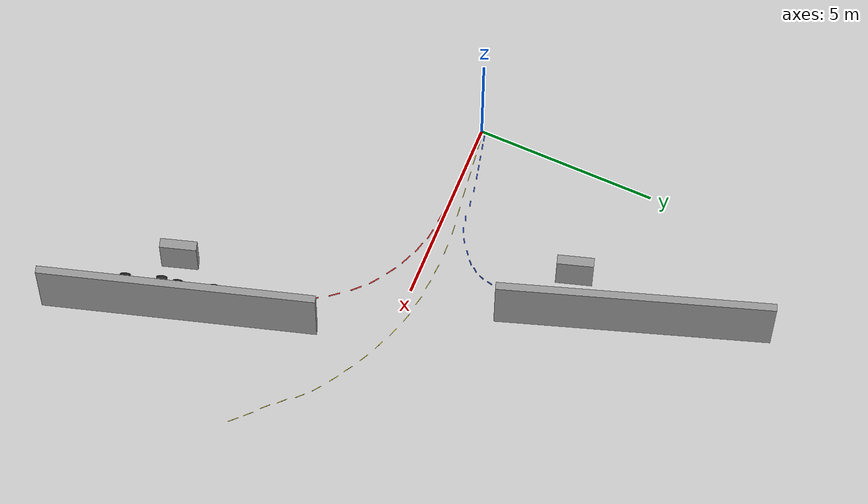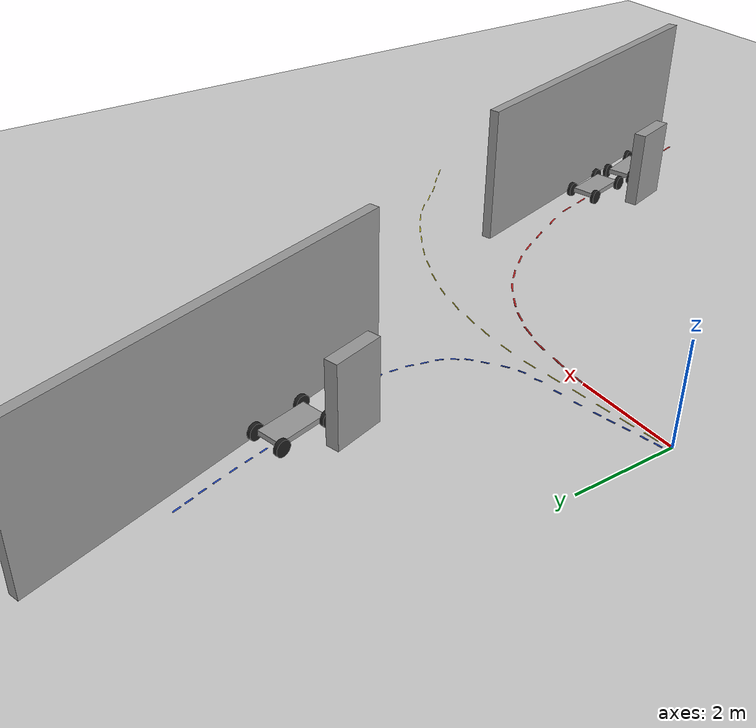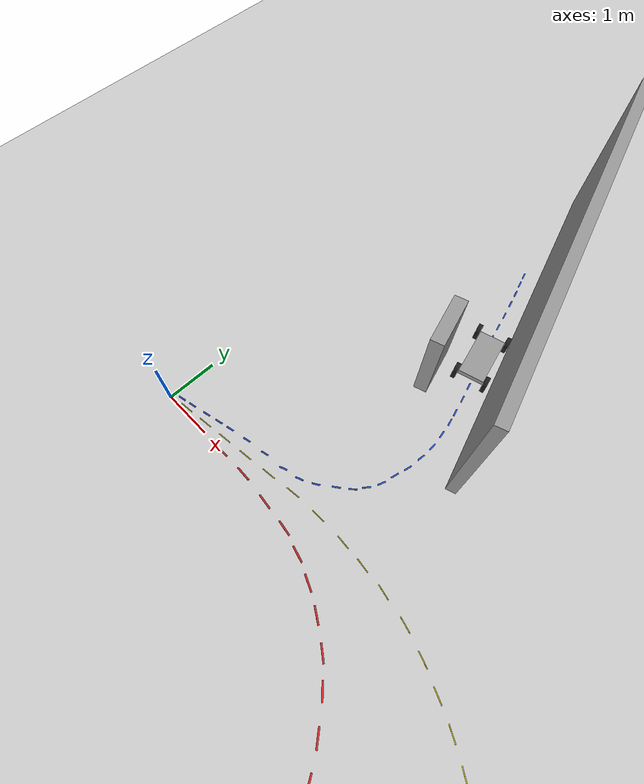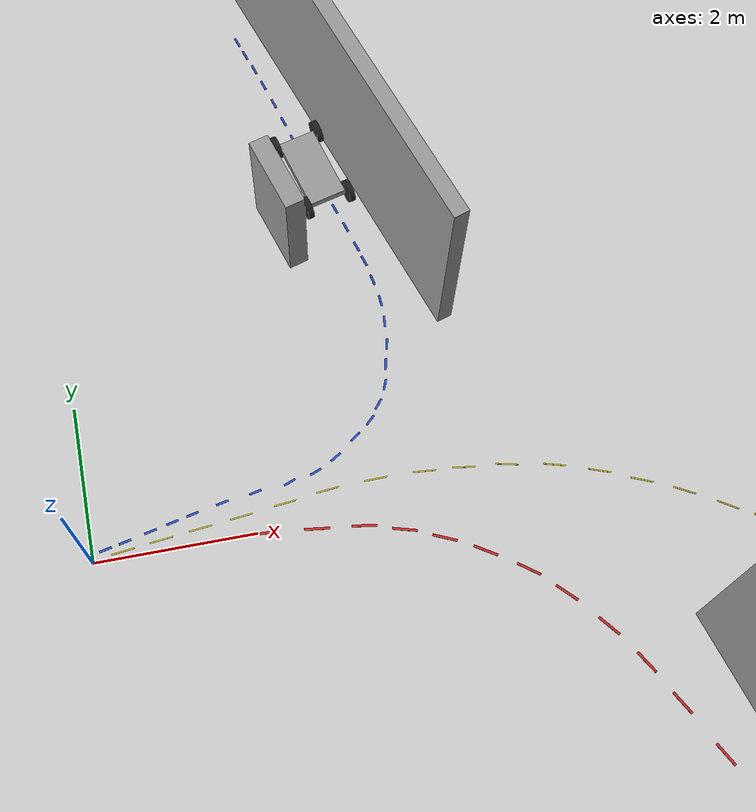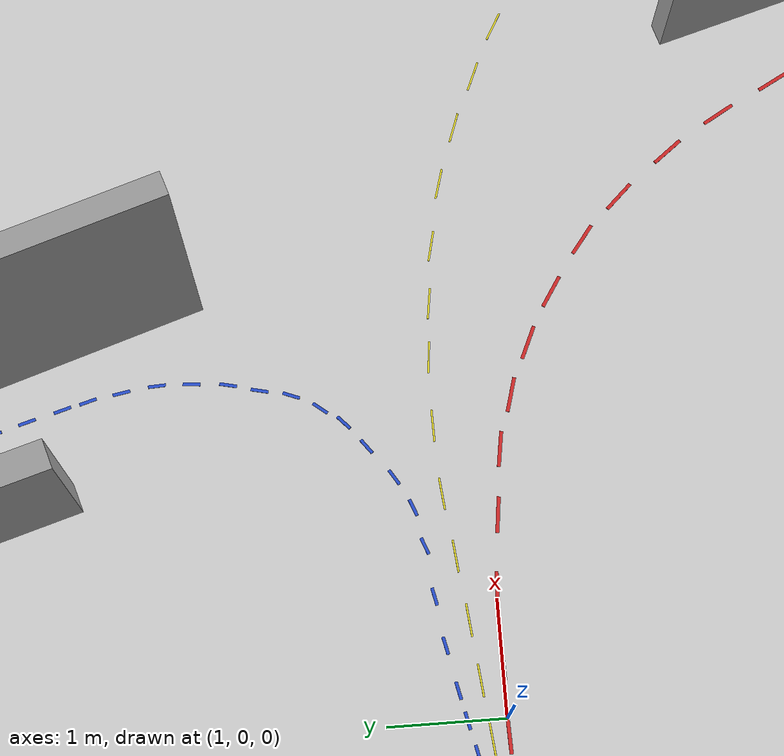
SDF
<sdf version="1.7">
 <world name="curve5">
  <light name="sun" type="directional">
   <pose>0 0 10 0 -0 0</pose>
   <diffuse>0.8 0.8 0.8 1</diffuse>
   <specular>0.2 0.2 0.2 1</specular>
   <attenuation>
    <range>1000</range>
    <constant>0.9</constant>
    <linear>0.01</linear>
    <quadratic>0.001</quadratic>
   </attenuation>
   <direction>-0.5 0.1 -0.9</direction>
   <spot><inner_angle>0</inner_angle><outer_angle>0</outer_angle><falloff>0</falloff></spot>
  </light>
  <model name="ground_plane">
   <static>1</static>
   <link name="link">
    <collision name="collision">
     <geometry><plane><normal>0 0 1</normal><size>100 100</size></plane></geometry>
     <surface><friction><ode><mu>100</mu><mu2>50</mu2></ode></friction></surface>
    </collision>
    <visual name="visual">
     <cast_shadows>0</cast_shadows>
     <geometry><plane><normal>0 0 1</normal><size>100 100</size></plane></geometry>
     <material>
      <script><uri>file://media/materials/scripts/gazebo.material</uri><name>Gazebo/Grey</name></script>
     </material>
    </visual>
   </link>
  </model>
  <gravity>0 0 -9.8</gravity>
  <magnetic_field>6e-06 2.3e-05 -4.2e-05</magnetic_field>
  <atmosphere type="adiabatic"/>
  <physics type="ode">
   <max_step_size>0.001</max_step_size>
   <real_time_factor>1</real_time_factor>
   <real_time_update_rate>1000</real_time_update_rate>
  </physics>
  <scene><ambient>0.4 0.4 0.4 1</ambient><background>0.7 0.7 0.7 1</background><shadows>1</shadows></scene>
  <spherical_coordinates>
   <surface_model>EARTH_WGS84</surface_model>
   <latitude_deg>0</latitude_deg>
   <longitude_deg>0</longitude_deg>
   <elevation>0</elevation>
   <heading_deg>0</heading_deg>
  </spherical_coordinates>
  <model name="curveRoad_try4">
   <link name="link_clone_0">
    <inertial>
     <mass>2.24783e-05</mass>
     <inertia>
      <ixx>5.11852e-10</ixx>
      <ixy>0</ixy>
      <ixz>0</ixz>
      <iyy>1.4911e-07</iyy>
      <iyz>0</iyz>
      <izz>1.49526e-07</izz>
     </inertia>
    </inertial>
    <pose>3.62116 -0.509853 1.1e-05 -1e-05 -1e-06 -0.087959</pose>
    <visual name="visual">
     <geometry><box><size>0.282093 0.015736 0.005062</size></box></geometry>
     <material>
      <script><name>Gazebo/Yellow</name><uri>file://media/materials/scripts/gazebo.material</uri></script>
      <shader type="pixel"><normal_map>__default__</normal_map></shader>
      <ambient>1 1 0 1</ambient>
      <diffuse>1 1 0 1</diffuse>
      <emissive>0 0 0 1</emissive>
     </material>
    </visual>
    <collision name="collision">
     <geometry><box><size>0.282093 0.015736 0.005062</size></box></geometry>
     <surface>
      <friction>
       <ode><mu>1</mu><mu2>1</mu2><fdir1>0 0 0</fdir1><slip1>0</slip1><slip2>0</slip2></ode>
       <torsional>
        <coefficient>1</coefficient>
        <patch_radius>0</patch_radius>
        <surface_radius>0</surface_radius>
        <use_patch_radius>1</use_patch_radius>
        <ode><slip>0</slip></ode>
       </torsional>
      </friction>
      <bounce><restitution_coefficient>0</restitution_coefficient><threshold>1e+06</threshold></bounce>
      <contact>
       <collide_without_contact>0</collide_without_contact>
       <collide_without_contact_bitmask>1</collide_without_contact_bitmask>
       <collide_bitmask>1</collide_bitmask>
       <ode>
        <soft_cfm>0</soft_cfm>
        <soft_erp>0.2</soft_erp>
        <kp>1e+13</kp>
        <kd>1</kd>
        <max_vel>0.01</max_vel>
        <min_depth>0</min_depth>
       </ode>
       <bullet>
        <split_impulse>1</split_impulse>
        <split_impulse_penetration_threshold>-0.01</split_impulse_penetration_threshold>
        <soft_cfm>0</soft_cfm>
        <soft_erp>0.2</soft_erp>
        <kp>1e+13</kp>
        <kd>1</kd>
       </bullet>
      </contact>
     </surface>
    </collision>
   </link>
   <link name="link_clone_0_clone">
    <inertial>
     <mass>2.24783e-05</mass>
     <inertia>
      <ixx>5.11852e-10</ixx>
      <ixy>0</ixy>
      <ixz>0</ixz>
      <iyy>1.4911e-07</iyy>
      <iyz>0</iyz>
      <izz>1.49526e-07</izz>
     </inertia>
    </inertial>
    <pose>2.40632 -0.527381 1.5e-05 -2e-05 2e-06 0.102518</pose>
    <visual name="visual">
     <geometry><box><size>0.282093 0.015736 0.005062</size></box></geometry>
     <material>
      <script><name>Gazebo/Yellow</name><uri>file://media/materials/scripts/gazebo.material</uri></script>
      <shader type="pixel"><normal_map>__default__</normal_map></shader>
      <ambient>1 1 0 1</ambient>
      <diffuse>1 1 0 1</diffuse>
      <emissive>0 0 0 1</emissive>
     </material>
    </visual>
    <collision name="collision">
     <geometry><box><size>0.282093 0.015736 0.005062</size></box></geometry>
     <surface>
      <friction>
       <ode><mu>1</mu><mu2>1</mu2><fdir1>0 0 0</fdir1><slip1>0</slip1><slip2>0</slip2></ode>
       <torsional>
        <coefficient>1</coefficient>
        <patch_radius>0</patch_radius>
        <surface_radius>0</surface_radius>
        <use_patch_radius>1</use_patch_radius>
        <ode><slip>0</slip></ode>
       </torsional>
      </friction>
      <bounce><restitution_coefficient>0</restitution_coefficient><threshold>1e+06</threshold></bounce>
      <contact>
       <collide_without_contact>0</collide_without_contact>
       <collide_without_contact_bitmask>1</collide_without_contact_bitmask>
       <collide_bitmask>1</collide_bitmask>
       <ode>
        <soft_cfm>0</soft_cfm>
        <soft_erp>0.2</soft_erp>
        <kp>1e+13</kp>
        <kd>1</kd>
        <max_vel>0.01</max_vel>
        <min_depth>0</min_depth>
       </ode>
       <bullet>
        <split_impulse>1</split_impulse>
        <split_impulse_penetration_threshold>-0.01</split_impulse_penetration_threshold>
        <soft_cfm>0</soft_cfm>
        <soft_erp>0.2</soft_erp>
        <kp>1e+13</kp>
        <kd>1</kd>
       </bullet>
      </contact>
     </surface>
    </collision>
   </link>
   <link name="link_clone_0_clone_0">
    <inertial>
     <mass>2.24783e-05</mass>
     <inertia>
      <ixx>5.11852e-10</ixx>
      <ixy>0</ixy>
      <ixz>0</ixz>
      <iyy>1.4911e-07</iyy>
      <iyz>0</iyz>
      <izz>1.49526e-07</izz>
     </inertia>
    </inertial>
    <pose>3.00977 -0.49735 1.5e-05 -2e-05 1e-06 0.017291</pose>
    <visual name="visual">
     <geometry><box><size>0.282093 0.015736 0.005062</size></box></geometry>
     <material>
      <script><name>Gazebo/Yellow</name><uri>file://media/materials/scripts/gazebo.material</uri></script>
      <shader type="pixel"><normal_map>__default__</normal_map></shader>
      <ambient>1 1 0 1</ambient>
      <diffuse>1 1 0 1</diffuse>
      <emissive>0 0 0 1</emissive>
     </material>
    </visual>
    <collision name="collision">
     <geometry><box><size>0.282093 0.015736 0.005062</size></box></geometry>
     <surface>
      <friction>
       <ode><mu>1</mu><mu2>1</mu2><fdir1>0 0 0</fdir1><slip1>0</slip1><slip2>0</slip2></ode>
       <torsional>
        <coefficient>1</coefficient>
        <patch_radius>0</patch_radius>
        <surface_radius>0</surface_radius>
        <use_patch_radius>1</use_patch_radius>
        <ode><slip>0</slip></ode>
       </torsional>
      </friction>
      <bounce><restitution_coefficient>0</restitution_coefficient><threshold>1e+06</threshold></bounce>
      <contact>
       <collide_without_contact>0</collide_without_contact>
       <collide_without_contact_bitmask>1</collide_without_contact_bitmask>
       <collide_bitmask>1</collide_bitmask>
       <ode>
        <soft_cfm>0</soft_cfm>
        <soft_erp>0.2</soft_erp>
        <kp>1e+13</kp>
        <kd>1</kd>
        <max_vel>0.01</max_vel>
        <min_depth>0</min_depth>
       </ode>
       <bullet>
        <split_impulse>1</split_impulse>
        <split_impulse_penetration_threshold>-0.01</split_impulse_penetration_threshold>
        <soft_cfm>0</soft_cfm>
        <soft_erp>0.2</soft_erp>
        <kp>1e+13</kp>
        <kd>1</kd>
       </bullet>
      </contact>
     </surface>
    </collision>
   </link>
   <link name="link_clone_0_clone_1">
    <inertial>
     <mass>2.24783e-05</mass>
     <inertia>
      <ixx>5.11852e-10</ixx>
      <ixy>0</ixy>
      <ixz>0</ixz>
      <iyy>1.4911e-07</iyy>
      <iyz>0</iyz>
      <izz>1.49526e-07</izz>
     </inertia>
    </inertial>
    <pose>4.11142 -0.549088 1.7e-05 -2e-05 -3e-06 -0.140061</pose>
    <visual name="visual">
     <geometry><box><size>0.282093 0.015736 0.005062</size></box></geometry>
     <material>
      <script><name>Gazebo/Yellow</name><uri>file://media/materials/scripts/gazebo.material</uri></script>
      <shader type="pixel"><normal_map>__default__</normal_map></shader>
      <ambient>1 1 0 1</ambient>
      <diffuse>1 1 0 1</diffuse>
      <emissive>0 0 0 1</emissive>
     </material>
    </visual>
    <collision name="collision">
     <geometry><box><size>0.282093 0.015736 0.005062</size></box></geometry>
     <surface>
      <friction>
       <ode><mu>1</mu><mu2>1</mu2><fdir1>0 0 0</fdir1><slip1>0</slip1><slip2>0</slip2></ode>
       <torsional>
        <coefficient>1</coefficient>
        <patch_radius>0</patch_radius>
        <surface_radius>0</surface_radius>
        <use_patch_radius>1</use_patch_radius>
        <ode><slip>0</slip></ode>
       </torsional>
      </friction>
      <bounce><restitution_coefficient>0</restitution_coefficient><threshold>1e+06</threshold></bounce>
      <contact>
       <collide_without_contact>0</collide_without_contact>
       <collide_without_contact_bitmask>1</collide_without_contact_bitmask>
       <collide_bitmask>1</collide_bitmask>
       <ode>
        <soft_cfm>0</soft_cfm>
        <soft_erp>0.2</soft_erp>
        <kp>1e+13</kp>
        <kd>1</kd>
        <max_vel>0.01</max_vel>
        <min_depth>0</min_depth>
       </ode>
       <bullet>
        <split_impulse>1</split_impulse>
        <split_impulse_penetration_threshold>-0.01</split_impulse_penetration_threshold>
        <soft_cfm>0</soft_cfm>
        <soft_erp>0.2</soft_erp>
        <kp>1e+13</kp>
        <kd>1</kd>
       </bullet>
      </contact>
     </surface>
    </collision>
   </link>
   <link name="link_clone_0_clone_10">
    <inertial>
     <mass>2.24783e-05</mass>
     <inertia>
      <ixx>5.11852e-10</ixx>
      <ixy>0</ixy>
      <ixz>0</ixz>
      <iyy>1.4911e-07</iyy>
      <iyz>0</iyz>
      <izz>1.49526e-07</izz>
     </inertia>
    </inertial>
    <pose>8.37665 -2.51207 3.1e-05 -1.4e-05 -1.4e-05 -0.787286</pose>
    <visual name="visual">
     <geometry><box><size>0.282093 0.015736 0.005062</size></box></geometry>
     <material>
      <script><name>Gazebo/Yellow</name><uri>file://media/materials/scripts/gazebo.material</uri></script>
      <shader type="pixel"><normal_map>__default__</normal_map></shader>
      <ambient>1 1 0 1</ambient>
      <diffuse>1 1 0 1</diffuse>
      <emissive>0 0 0 1</emissive>
     </material>
    </visual>
    <collision name="collision">
     <geometry><box><size>0.282093 0.015736 0.005062</size></box></geometry>
     <surface>
      <friction>
       <ode><mu>1</mu><mu2>1</mu2><fdir1>0 0 0</fdir1><slip1>0</slip1><slip2>0</slip2></ode>
       <torsional>
        <coefficient>1</coefficient>
        <patch_radius>0</patch_radius>
        <surface_radius>0</surface_radius>
        <use_patch_radius>1</use_patch_radius>
        <ode><slip>0</slip></ode>
       </torsional>
      </friction>
      <bounce><restitution_coefficient>0</restitution_coefficient><threshold>1e+06</threshold></bounce>
      <contact>
       <collide_without_contact>0</collide_without_contact>
       <collide_without_contact_bitmask>1</collide_without_contact_bitmask>
       <collide_bitmask>1</collide_bitmask>
       <ode>
        <soft_cfm>0</soft_cfm>
        <soft_erp>0.2</soft_erp>
        <kp>1e+13</kp>
        <kd>1</kd>
        <max_vel>0.01</max_vel>
        <min_depth>0</min_depth>
       </ode>
       <bullet>
        <split_impulse>1</split_impulse>
        <split_impulse_penetration_threshold>-0.01</split_impulse_penetration_threshold>
        <soft_cfm>0</soft_cfm>
        <soft_erp>0.2</soft_erp>
        <kp>1e+13</kp>
        <kd>1</kd>
       </bullet>
      </contact>
     </surface>
    </collision>
   </link>
   <link name="link_clone_0_clone_10_clone">
    <inertial>
     <mass>2.24783e-05</mass>
     <inertia>
      <ixx>5.11852e-10</ixx>
      <ixy>0</ixy>
      <ixz>0</ixz>
      <iyy>1.4911e-07</iyy>
      <iyz>0</iyz>
      <izz>1.49526e-07</izz>
     </inertia>
    </inertial>
    <pose>8.69472 -2.89353 5.8e-05 -2.1e-05 -2.1e-05 -0.787286</pose>
    <visual name="visual">
     <geometry><box><size>0.282093 0.015736 0.005062</size></box></geometry>
     <material>
      <script><name>Gazebo/Yellow</name><uri>file://media/materials/scripts/gazebo.material</uri></script>
      <shader type="pixel"><normal_map>__default__</normal_map></shader>
      <ambient>1 1 0 1</ambient>
      <diffuse>1 1 0 1</diffuse>
      <emissive>0 0 0 1</emissive>
     </material>
    </visual>
    <collision name="collision">
     <geometry><box><size>0.282093 0.015736 0.005062</size></box></geometry>
     <surface>
      <friction>
       <ode><mu>1</mu><mu2>1</mu2><fdir1>0 0 0</fdir1><slip1>0</slip1><slip2>0</slip2></ode>
       <torsional>
        <coefficient>1</coefficient>
        <patch_radius>0</patch_radius>
        <surface_radius>0</surface_radius>
        <use_patch_radius>1</use_patch_radius>
        <ode><slip>0</slip></ode>
       </torsional>
      </friction>
      <bounce><restitution_coefficient>0</restitution_coefficient><threshold>1e+06</threshold></bounce>
      <contact>
       <collide_without_contact>0</collide_without_contact>
       <collide_without_contact_bitmask>1</collide_without_contact_bitmask>
       <collide_bitmask>1</collide_bitmask>
       <ode>
        <soft_cfm>0</soft_cfm>
        <soft_erp>0.2</soft_erp>
        <kp>1e+13</kp>
        <kd>1</kd>
        <max_vel>0.01</max_vel>
        <min_depth>0</min_depth>
       </ode>
       <bullet>
        <split_impulse>1</split_impulse>
        <split_impulse_penetration_threshold>-0.01</split_impulse_penetration_threshold>
        <soft_cfm>0</soft_cfm>
        <soft_erp>0.2</soft_erp>
        <kp>1e+13</kp>
        <kd>1</kd>
       </bullet>
      </contact>
     </surface>
    </collision>
   </link>
   <link name="link_clone_0_clone_10_clone_0">
    <inertial>
     <mass>2.24783e-05</mass>
     <inertia>
      <ixx>5.11852e-10</ixx>
      <ixy>0</ixy>
      <ixz>0</ixz>
      <iyy>1.4911e-07</iyy>
      <iyz>0</iyz>
      <izz>1.49526e-07</izz>
     </inertia>
    </inertial>
    <pose>9.01781 -3.25437 6.1e-05 -2.1e-05 -2.1e-05 -0.787286</pose>
    <visual name="visual">
     <geometry><box><size>0.282093 0.015736 0.005062</size></box></geometry>
     <material>
      <script><name>Gazebo/Yellow</name><uri>file://media/materials/scripts/gazebo.material</uri></script>
      <shader type="pixel"><normal_map>__default__</normal_map></shader>
      <ambient>1 1 0 1</ambient>
      <diffuse>1 1 0 1</diffuse>
      <emissive>0 0 0 1</emissive>
     </material>
    </visual>
    <collision name="collision">
     <geometry><box><size>0.282093 0.015736 0.005062</size></box></geometry>
     <surface>
      <friction>
       <ode><mu>1</mu><mu2>1</mu2><fdir1>0 0 0</fdir1><slip1>0</slip1><slip2>0</slip2></ode>
       <torsional>
        <coefficient>1</coefficient>
        <patch_radius>0</patch_radius>
        <surface_radius>0</surface_radius>
        <use_patch_radius>1</use_patch_radius>
        <ode><slip>0</slip></ode>
       </torsional>
      </friction>
      <bounce><restitution_coefficient>0</restitution_coefficient><threshold>1e+06</threshold></bounce>
      <contact>
       <collide_without_contact>0</collide_without_contact>
       <collide_without_contact_bitmask>1</collide_without_contact_bitmask>
       <collide_bitmask>1</collide_bitmask>
       <ode>
        <soft_cfm>0</soft_cfm>
        <soft_erp>0.2</soft_erp>
        <kp>1e+13</kp>
        <kd>1</kd>
        <max_vel>0.01</max_vel>
        <min_depth>0</min_depth>
       </ode>
       <bullet>
        <split_impulse>1</split_impulse>
        <split_impulse_penetration_threshold>-0.01</split_impulse_penetration_threshold>
        <soft_cfm>0</soft_cfm>
        <soft_erp>0.2</soft_erp>
        <kp>1e+13</kp>
        <kd>1</kd>
       </bullet>
      </contact>
     </surface>
    </collision>
   </link>
   <link name="link_clone_0_clone_10_clone_1">
    <inertial>
     <mass>2.24783e-05</mass>
     <inertia>
      <ixx>5.11852e-10</ixx>
      <ixy>0</ixy>
      <ixz>0</ixz>
      <iyy>1.4911e-07</iyy>
      <iyz>0</iyz>
      <izz>1.49526e-07</izz>
     </inertia>
    </inertial>
    <pose>9.3828 -3.59003 6.4e-05 -2.1e-05 -2.1e-05 -0.787286</pose>
    <visual name="visual">
     <geometry><box><size>0.282093 0.015736 0.005062</size></box></geometry>
     <material>
      <script><name>Gazebo/Yellow</name><uri>file://media/materials/scripts/gazebo.material</uri></script>
      <shader type="pixel"><normal_map>__default__</normal_map></shader>
      <ambient>1 1 0 1</ambient>
      <diffuse>1 1 0 1</diffuse>
      <emissive>0 0 0 1</emissive>
     </material>
    </visual>
    <collision name="collision">
     <geometry><box><size>0.282093 0.015736 0.005062</size></box></geometry>
     <surface>
      <friction>
       <ode><mu>1</mu><mu2>1</mu2><fdir1>0 0 0</fdir1><slip1>0</slip1><slip2>0</slip2></ode>
       <torsional>
        <coefficient>1</coefficient>
        <patch_radius>0</patch_radius>
        <surface_radius>0</surface_radius>
        <use_patch_radius>1</use_patch_radius>
        <ode><slip>0</slip></ode>
       </torsional>
      </friction>
      <bounce><restitution_coefficient>0</restitution_coefficient><threshold>1e+06</threshold></bounce>
      <contact>
       <collide_without_contact>0</collide_without_contact>
       <collide_without_contact_bitmask>1</collide_without_contact_bitmask>
       <collide_bitmask>1</collide_bitmask>
       <ode>
        <soft_cfm>0</soft_cfm>
        <soft_erp>0.2</soft_erp>
        <kp>1e+13</kp>
        <kd>1</kd>
        <max_vel>0.01</max_vel>
        <min_depth>0</min_depth>
       </ode>
       <bullet>
        <split_impulse>1</split_impulse>
        <split_impulse_penetration_threshold>-0.01</split_impulse_penetration_threshold>
        <soft_cfm>0</soft_cfm>
        <soft_erp>0.2</soft_erp>
        <kp>1e+13</kp>
        <kd>1</kd>
       </bullet>
      </contact>
     </surface>
    </collision>
   </link>
   <link name="link_clone_0_clone_10_clone_2">
    <inertial>
     <mass>2.24783e-05</mass>
     <inertia>
      <ixx>5.11852e-10</ixx>
      <ixy>0</ixy>
      <ixz>0</ixz>
      <iyy>1.4911e-07</iyy>
      <iyz>0</iyz>
      <izz>1.49526e-07</izz>
     </inertia>
    </inertial>
    <pose>9.68488 -3.90053 6.8e-05 -2.1e-05 -2.1e-05 -0.787286</pose>
    <visual name="visual">
     <geometry><box><size>0.282093 0.015736 0.005062</size></box></geometry>
     <material>
      <script><name>Gazebo/Yellow</name><uri>file://media/materials/scripts/gazebo.material</uri></script>
      <shader type="pixel"><normal_map>__default__</normal_map></shader>
      <ambient>1 1 0 1</ambient>
      <diffuse>1 1 0 1</diffuse>
      <emissive>0 0 0 1</emissive>
     </material>
    </visual>
    <collision name="collision">
     <geometry><box><size>0.282093 0.015736 0.005062</size></box></geometry>
     <surface>
      <friction>
       <ode><mu>1</mu><mu2>1</mu2><fdir1>0 0 0</fdir1><slip1>0</slip1><slip2>0</slip2></ode>
       <torsional>
        <coefficient>1</coefficient>
        <patch_radius>0</patch_radius>
        <surface_radius>0</surface_radius>
        <use_patch_radius>1</use_patch_radius>
        <ode><slip>0</slip></ode>
       </torsional>
      </friction>
      <bounce><restitution_coefficient>0</restitution_coefficient><threshold>1e+06</threshold></bounce>
      <contact>
       <collide_without_contact>0</collide_without_contact>
       <collide_without_contact_bitmask>1</collide_without_contact_bitmask>
       <collide_bitmask>1</collide_bitmask>
       <ode>
        <soft_cfm>0</soft_cfm>
        <soft_erp>0.2</soft_erp>
        <kp>1e+13</kp>
        <kd>1</kd>
        <max_vel>0.01</max_vel>
        <min_depth>0</min_depth>
       </ode>
       <bullet>
        <split_impulse>1</split_impulse>
        <split_impulse_penetration_threshold>-0.01</split_impulse_penetration_threshold>
        <soft_cfm>0</soft_cfm>
        <soft_erp>0.2</soft_erp>
        <kp>1e+13</kp>
        <kd>1</kd>
       </bullet>
      </contact>
     </surface>
    </collision>
   </link>
   <link name="link_clone_0_clone_2">
    <inertial>
     <mass>2.24783e-05</mass>
     <inertia>
      <ixx>5.11852e-10</ixx>
      <ixy>0</ixy>
      <ixz>0</ixz>
      <iyy>1.4911e-07</iyy>
      <iyz>0</iyz>
      <izz>1.49526e-07</izz>
     </inertia>
    </inertial>
    <pose>4.6399 -0.60856 1.6e-05 -2e-05 -4e-06 -0.224564</pose>
    <visual name="visual">
     <geometry><box><size>0.282093 0.015736 0.005062</size></box></geometry>
     <material>
      <script><name>Gazebo/Yellow</name><uri>file://media/materials/scripts/gazebo.material</uri></script>
      <shader type="pixel"><normal_map>__default__</normal_map></shader>
      <ambient>1 1 0 1</ambient>
      <diffuse>1 1 0 1</diffuse>
      <emissive>0 0 0 1</emissive>
     </material>
    </visual>
    <collision name="collision">
     <geometry><box><size>0.282093 0.015736 0.005062</size></box></geometry>
     <surface>
      <friction>
       <ode><mu>1</mu><mu2>1</mu2><fdir1>0 0 0</fdir1><slip1>0</slip1><slip2>0</slip2></ode>
       <torsional>
        <coefficient>1</coefficient>
        <patch_radius>0</patch_radius>
        <surface_radius>0</surface_radius>
        <use_patch_radius>1</use_patch_radius>
        <ode><slip>0</slip></ode>
       </torsional>
      </friction>
      <bounce><restitution_coefficient>0</restitution_coefficient><threshold>1e+06</threshold></bounce>
      <contact>
       <collide_without_contact>0</collide_without_contact>
       <collide_without_contact_bitmask>1</collide_without_contact_bitmask>
       <collide_bitmask>1</collide_bitmask>
       <ode>
        <soft_cfm>0</soft_cfm>
        <soft_erp>0.2</soft_erp>
        <kp>1e+13</kp>
        <kd>1</kd>
        <max_vel>0.01</max_vel>
        <min_depth>0</min_depth>
       </ode>
       <bullet>
        <split_impulse>1</split_impulse>
        <split_impulse_penetration_threshold>-0.01</split_impulse_penetration_threshold>
        <soft_cfm>0</soft_cfm>
        <soft_erp>0.2</soft_erp>
        <kp>1e+13</kp>
        <kd>1</kd>
       </bullet>
      </contact>
     </surface>
    </collision>
   </link>
   <link name="link_clone_0_clone_3">
    <inertial>
     <mass>2.24783e-05</mass>
     <inertia>
      <ixx>5.11852e-10</ixx>
      <ixy>0</ixy>
      <ixz>0</ixz>
      <iyy>1.4911e-07</iyy>
      <iyz>0</iyz>
      <izz>1.49526e-07</izz>
     </inertia>
    </inertial>
    <pose>5.21731 -0.723385 1.5e-05 -2e-05 -5e-06 -0.274195</pose>
    <visual name="visual">
     <geometry><box><size>0.282093 0.015736 0.005062</size></box></geometry>
     <material>
      <script><name>Gazebo/Yellow</name><uri>file://media/materials/scripts/gazebo.material</uri></script>
      <shader type="pixel"><normal_map>__default__</normal_map></shader>
      <ambient>1 1 0 1</ambient>
      <diffuse>1 1 0 1</diffuse>
      <emissive>0 0 0 1</emissive>
     </material>
    </visual>
    <collision name="collision">
     <geometry><box><size>0.282093 0.015736 0.005062</size></box></geometry>
     <surface>
      <friction>
       <ode><mu>1</mu><mu2>1</mu2><fdir1>0 0 0</fdir1><slip1>0</slip1><slip2>0</slip2></ode>
       <torsional>
        <coefficient>1</coefficient>
        <patch_radius>0</patch_radius>
        <surface_radius>0</surface_radius>
        <use_patch_radius>1</use_patch_radius>
        <ode><slip>0</slip></ode>
       </torsional>
      </friction>
      <bounce><restitution_coefficient>0</restitution_coefficient><threshold>1e+06</threshold></bounce>
      <contact>
       <collide_without_contact>0</collide_without_contact>
       <collide_without_contact_bitmask>1</collide_without_contact_bitmask>
       <collide_bitmask>1</collide_bitmask>
       <ode>
        <soft_cfm>0</soft_cfm>
        <soft_erp>0.2</soft_erp>
        <kp>1e+13</kp>
        <kd>1</kd>
        <max_vel>0.01</max_vel>
        <min_depth>0</min_depth>
       </ode>
       <bullet>
        <split_impulse>1</split_impulse>
        <split_impulse_penetration_threshold>-0.01</split_impulse_penetration_threshold>
        <soft_cfm>0</soft_cfm>
        <soft_erp>0.2</soft_erp>
        <kp>1e+13</kp>
        <kd>1</kd>
       </bullet>
      </contact>
     </surface>
    </collision>
   </link>
   <link name="link_clone_0_clone_4">
    <inertial>
     <mass>2.24783e-05</mass>
     <inertia>
      <ixx>5.11852e-10</ixx>
      <ixy>0</ixy>
      <ixz>0</ixz>
      <iyy>1.4911e-07</iyy>
      <iyz>0</iyz>
      <izz>1.49526e-07</izz>
     </inertia>
    </inertial>
    <pose>5.74387 -0.900095 1.5e-05 -1.9e-05 -7e-06 -0.338412</pose>
    <visual name="visual">
     <geometry><box><size>0.282093 0.015736 0.005062</size></box></geometry>
     <material>
      <script><name>Gazebo/Yellow</name><uri>file://media/materials/scripts/gazebo.material</uri></script>
      <shader type="pixel"><normal_map>__default__</normal_map></shader>
      <ambient>1 1 0 1</ambient>
      <diffuse>1 1 0 1</diffuse>
      <emissive>0 0 0 1</emissive>
     </material>
    </visual>
    <collision name="collision">
     <geometry><box><size>0.282093 0.015736 0.005062</size></box></geometry>
     <surface>
      <friction>
       <ode><mu>1</mu><mu2>1</mu2><fdir1>0 0 0</fdir1><slip1>0</slip1><slip2>0</slip2></ode>
       <torsional>
        <coefficient>1</coefficient>
        <patch_radius>0</patch_radius>
        <surface_radius>0</surface_radius>
        <use_patch_radius>1</use_patch_radius>
        <ode><slip>0</slip></ode>
       </torsional>
      </friction>
      <bounce><restitution_coefficient>0</restitution_coefficient><threshold>1e+06</threshold></bounce>
      <contact>
       <collide_without_contact>0</collide_without_contact>
       <collide_without_contact_bitmask>1</collide_without_contact_bitmask>
       <collide_bitmask>1</collide_bitmask>
       <ode>
        <soft_cfm>0</soft_cfm>
        <soft_erp>0.2</soft_erp>
        <kp>1e+13</kp>
        <kd>1</kd>
        <max_vel>0.01</max_vel>
        <min_depth>0</min_depth>
       </ode>
       <bullet>
        <split_impulse>1</split_impulse>
        <split_impulse_penetration_threshold>-0.01</split_impulse_penetration_threshold>
        <soft_cfm>0</soft_cfm>
        <soft_erp>0.2</soft_erp>
        <kp>1e+13</kp>
        <kd>1</kd>
       </bullet>
      </contact>
     </surface>
    </collision>
   </link>
   <link name="link_clone_0_clone_5">
    <inertial>
     <mass>2.24783e-05</mass>
     <inertia>
      <ixx>5.11852e-10</ixx>
      <ixy>0</ixy>
      <ixz>0</ixz>
      <iyy>1.4911e-07</iyy>
      <iyz>0</iyz>
      <izz>1.49526e-07</izz>
     </inertia>
    </inertial>
    <pose>6.22844 -1.1116 1.9e-05 -1.9e-05 -8e-06 -0.397242</pose>
    <visual name="visual">
     <geometry><box><size>0.282093 0.015736 0.005062</size></box></geometry>
     <material>
      <script><name>Gazebo/Yellow</name><uri>file://media/materials/scripts/gazebo.material</uri></script>
      <shader type="pixel"><normal_map>__default__</normal_map></shader>
      <ambient>1 1 0 1</ambient>
      <diffuse>1 1 0 1</diffuse>
      <emissive>0 0 0 1</emissive>
     </material>
    </visual>
    <collision name="collision">
     <geometry><box><size>0.282093 0.015736 0.005062</size></box></geometry>
     <surface>
      <friction>
       <ode><mu>1</mu><mu2>1</mu2><fdir1>0 0 0</fdir1><slip1>0</slip1><slip2>0</slip2></ode>
       <torsional>
        <coefficient>1</coefficient>
        <patch_radius>0</patch_radius>
        <surface_radius>0</surface_radius>
        <use_patch_radius>1</use_patch_radius>
        <ode><slip>0</slip></ode>
       </torsional>
      </friction>
      <bounce><restitution_coefficient>0</restitution_coefficient><threshold>1e+06</threshold></bounce>
      <contact>
       <collide_without_contact>0</collide_without_contact>
       <collide_without_contact_bitmask>1</collide_without_contact_bitmask>
       <collide_bitmask>1</collide_bitmask>
       <ode>
        <soft_cfm>0</soft_cfm>
        <soft_erp>0.2</soft_erp>
        <kp>1e+13</kp>
        <kd>1</kd>
        <max_vel>0.01</max_vel>
        <min_depth>0</min_depth>
       </ode>
       <bullet>
        <split_impulse>1</split_impulse>
        <split_impulse_penetration_threshold>-0.01</split_impulse_penetration_threshold>
        <soft_cfm>0</soft_cfm>
        <soft_erp>0.2</soft_erp>
        <kp>1e+13</kp>
        <kd>1</kd>
       </bullet>
      </contact>
     </surface>
    </collision>
   </link>
   <link name="link_clone_0_clone_6">
    <inertial>
     <mass>2.24783e-05</mass>
     <inertia>
      <ixx>5.11852e-10</ixx>
      <ixy>0</ixy>
      <ixz>0</ixz>
      <iyy>1.4911e-07</iyy>
      <iyz>0</iyz>
      <izz>1.49526e-07</izz>
     </inertia>
    </inertial>
    <pose>6.70402 -1.33717 2.1e-05 -1.8e-05 -1e-05 -0.503</pose>
    <visual name="visual">
     <geometry><box><size>0.282093 0.015736 0.005062</size></box></geometry>
     <material>
      <script><name>Gazebo/Yellow</name><uri>file://media/materials/scripts/gazebo.material</uri></script>
      <shader type="pixel"><normal_map>__default__</normal_map></shader>
      <ambient>1 1 0 1</ambient>
      <diffuse>1 1 0 1</diffuse>
      <emissive>0 0 0 1</emissive>
     </material>
    </visual>
    <collision name="collision">
     <geometry><box><size>0.282093 0.015736 0.005062</size></box></geometry>
     <surface>
      <friction>
       <ode><mu>1</mu><mu2>1</mu2><fdir1>0 0 0</fdir1><slip1>0</slip1><slip2>0</slip2></ode>
       <torsional>
        <coefficient>1</coefficient>
        <patch_radius>0</patch_radius>
        <surface_radius>0</surface_radius>
        <use_patch_radius>1</use_patch_radius>
        <ode><slip>0</slip></ode>
       </torsional>
      </friction>
      <bounce><restitution_coefficient>0</restitution_coefficient><threshold>1e+06</threshold></bounce>
      <contact>
       <collide_without_contact>0</collide_without_contact>
       <collide_without_contact_bitmask>1</collide_without_contact_bitmask>
       <collide_bitmask>1</collide_bitmask>
       <ode>
        <soft_cfm>0</soft_cfm>
        <soft_erp>0.2</soft_erp>
        <kp>1e+13</kp>
        <kd>1</kd>
        <max_vel>0.01</max_vel>
        <min_depth>0</min_depth>
       </ode>
       <bullet>
        <split_impulse>1</split_impulse>
        <split_impulse_penetration_threshold>-0.01</split_impulse_penetration_threshold>
        <soft_cfm>0</soft_cfm>
        <soft_erp>0.2</soft_erp>
        <kp>1e+13</kp>
        <kd>1</kd>
       </bullet>
      </contact>
     </surface>
    </collision>
   </link>
   <link name="link_clone_0_clone_7">
    <inertial>
     <mass>2.24783e-05</mass>
     <inertia>
      <ixx>5.11852e-10</ixx>
      <ixy>0</ixy>
      <ixz>0</ixz>
      <iyy>1.4911e-07</iyy>
      <iyz>0</iyz>
      <izz>1.49526e-07</izz>
     </inertia>
    </inertial>
    <pose>7.17641 -1.61422 2.3e-05 -1.7e-05 -1.1e-05 -0.569246</pose>
    <visual name="visual">
     <geometry><box><size>0.282093 0.015736 0.005062</size></box></geometry>
     <material>
      <script><name>Gazebo/Yellow</name><uri>file://media/materials/scripts/gazebo.material</uri></script>
      <shader type="pixel"><normal_map>__default__</normal_map></shader>
      <ambient>1 1 0 1</ambient>
      <diffuse>1 1 0 1</diffuse>
      <emissive>0 0 0 1</emissive>
     </material>
    </visual>
    <collision name="collision">
     <geometry><box><size>0.282093 0.015736 0.005062</size></box></geometry>
     <surface>
      <friction>
       <ode><mu>1</mu><mu2>1</mu2><fdir1>0 0 0</fdir1><slip1>0</slip1><slip2>0</slip2></ode>
       <torsional>
        <coefficient>1</coefficient>
        <patch_radius>0</patch_radius>
        <surface_radius>0</surface_radius>
        <use_patch_radius>1</use_patch_radius>
        <ode><slip>0</slip></ode>
       </torsional>
      </friction>
      <bounce><restitution_coefficient>0</restitution_coefficient><threshold>1e+06</threshold></bounce>
      <contact>
       <collide_without_contact>0</collide_without_contact>
       <collide_without_contact_bitmask>1</collide_without_contact_bitmask>
       <collide_bitmask>1</collide_bitmask>
       <ode>
        <soft_cfm>0</soft_cfm>
        <soft_erp>0.2</soft_erp>
        <kp>1e+13</kp>
        <kd>1</kd>
        <max_vel>0.01</max_vel>
        <min_depth>0</min_depth>
       </ode>
       <bullet>
        <split_impulse>1</split_impulse>
        <split_impulse_penetration_threshold>-0.01</split_impulse_penetration_threshold>
        <soft_cfm>0</soft_cfm>
        <soft_erp>0.2</soft_erp>
        <kp>1e+13</kp>
        <kd>1</kd>
       </bullet>
      </contact>
     </surface>
    </collision>
   </link>
   <link name="link_clone_0_clone_8">
    <inertial>
     <mass>2.24783e-05</mass>
     <inertia>
      <ixx>5.11852e-10</ixx>
      <ixy>0</ixy>
      <ixz>0</ixz>
      <iyy>1.4911e-07</iyy>
      <iyz>0</iyz>
      <izz>1.49526e-07</izz>
     </inertia>
    </inertial>
    <pose>7.57318 -1.86068 2.4e-05 -1.7e-05 -1.1e-05 -0.599064</pose>
    <visual name="visual">
     <geometry><box><size>0.282093 0.015736 0.005062</size></box></geometry>
     <material>
      <script><name>Gazebo/Yellow</name><uri>file://media/materials/scripts/gazebo.material</uri></script>
      <shader type="pixel"><normal_map>__default__</normal_map></shader>
      <ambient>1 1 0 1</ambient>
      <diffuse>1 1 0 1</diffuse>
      <emissive>0 0 0 1</emissive>
     </material>
    </visual>
    <collision name="collision">
     <geometry><box><size>0.282093 0.015736 0.005062</size></box></geometry>
     <surface>
      <friction>
       <ode><mu>1</mu><mu2>1</mu2><fdir1>0 0 0</fdir1><slip1>0</slip1><slip2>0</slip2></ode>
       <torsional>
        <coefficient>1</coefficient>
        <patch_radius>0</patch_radius>
        <surface_radius>0</surface_radius>
        <use_patch_radius>1</use_patch_radius>
        <ode><slip>0</slip></ode>
       </torsional>
      </friction>
      <bounce><restitution_coefficient>0</restitution_coefficient><threshold>1e+06</threshold></bounce>
      <contact>
       <collide_without_contact>0</collide_without_contact>
       <collide_without_contact_bitmask>1</collide_without_contact_bitmask>
       <collide_bitmask>1</collide_bitmask>
       <ode>
        <soft_cfm>0</soft_cfm>
        <soft_erp>0.2</soft_erp>
        <kp>1e+13</kp>
        <kd>1</kd>
        <max_vel>0.01</max_vel>
        <min_depth>0</min_depth>
       </ode>
       <bullet>
        <split_impulse>1</split_impulse>
        <split_impulse_penetration_threshold>-0.01</split_impulse_penetration_threshold>
        <soft_cfm>0</soft_cfm>
        <soft_erp>0.2</soft_erp>
        <kp>1e+13</kp>
        <kd>1</kd>
       </bullet>
      </contact>
     </surface>
    </collision>
   </link>
   <link name="link_clone_0_clone_9">
    <inertial>
     <mass>2.24783e-05</mass>
     <inertia>
      <ixx>5.11852e-10</ixx>
      <ixy>0</ixy>
      <ixz>0</ixz>
      <iyy>1.4911e-07</iyy>
      <iyz>0</iyz>
      <izz>1.49526e-07</izz>
     </inertia>
    </inertial>
    <pose>8.00946 -2.17414 2.9e-05 -1.6e-05 -1.2e-05 -0.652568</pose>
    <visual name="visual">
     <geometry><box><size>0.282093 0.015736 0.005062</size></box></geometry>
     <material>
      <script><name>Gazebo/Yellow</name><uri>file://media/materials/scripts/gazebo.material</uri></script>
      <shader type="pixel"><normal_map>__default__</normal_map></shader>
      <ambient>1 1 0 1</ambient>
      <diffuse>1 1 0 1</diffuse>
      <emissive>0 0 0 1</emissive>
     </material>
    </visual>
    <collision name="collision">
     <geometry><box><size>0.282093 0.015736 0.005062</size></box></geometry>
     <surface>
      <friction>
       <ode><mu>1</mu><mu2>1</mu2><fdir1>0 0 0</fdir1><slip1>0</slip1><slip2>0</slip2></ode>
       <torsional>
        <coefficient>1</coefficient>
        <patch_radius>0</patch_radius>
        <surface_radius>0</surface_radius>
        <use_patch_radius>1</use_patch_radius>
        <ode><slip>0</slip></ode>
       </torsional>
      </friction>
      <bounce><restitution_coefficient>0</restitution_coefficient><threshold>1e+06</threshold></bounce>
      <contact>
       <collide_without_contact>0</collide_without_contact>
       <collide_without_contact_bitmask>1</collide_without_contact_bitmask>
       <collide_bitmask>1</collide_bitmask>
       <ode>
        <soft_cfm>0</soft_cfm>
        <soft_erp>0.2</soft_erp>
        <kp>1e+13</kp>
        <kd>1</kd>
        <max_vel>0.01</max_vel>
        <min_depth>0</min_depth>
       </ode>
       <bullet>
        <split_impulse>1</split_impulse>
        <split_impulse_penetration_threshold>-0.01</split_impulse_penetration_threshold>
        <soft_cfm>0</soft_cfm>
        <soft_erp>0.2</soft_erp>
        <kp>1e+13</kp>
        <kd>1</kd>
       </bullet>
      </contact>
     </surface>
    </collision>
   </link>
   <link name="link_clone_0_clone_clone">
    <inertial>
     <mass>2.24783e-05</mass>
     <inertia>
      <ixx>5.11852e-10</ixx>
      <ixy>0</ixy>
      <ixz>0</ixz>
      <iyy>1.4911e-07</iyy>
      <iyz>0</iyz>
      <izz>1.49526e-07</izz>
     </inertia>
    </inertial>
    <pose>1.86271 -0.599112 2e-05 -3e-05 3e-06 0.102518</pose>
    <visual name="visual">
     <geometry><box><size>0.282093 0.015736 0.005062</size></box></geometry>
     <material>
      <script><name>Gazebo/Yellow</name><uri>file://media/materials/scripts/gazebo.material</uri></script>
      <shader type="pixel"><normal_map>__default__</normal_map></shader>
      <ambient>1 1 0 1</ambient>
      <diffuse>1 1 0 1</diffuse>
      <emissive>0 0 0 1</emissive>
     </material>
    </visual>
    <collision name="collision">
     <geometry><box><size>0.282093 0.015736 0.005062</size></box></geometry>
     <surface>
      <friction>
       <ode><mu>1</mu><mu2>1</mu2><fdir1>0 0 0</fdir1><slip1>0</slip1><slip2>0</slip2></ode>
       <torsional>
        <coefficient>1</coefficient>
        <patch_radius>0</patch_radius>
        <surface_radius>0</surface_radius>
        <use_patch_radius>1</use_patch_radius>
        <ode><slip>0</slip></ode>
       </torsional>
      </friction>
      <bounce><restitution_coefficient>0</restitution_coefficient><threshold>1e+06</threshold></bounce>
      <contact>
       <collide_without_contact>0</collide_without_contact>
       <collide_without_contact_bitmask>1</collide_without_contact_bitmask>
       <collide_bitmask>1</collide_bitmask>
       <ode>
        <soft_cfm>0</soft_cfm>
        <soft_erp>0.2</soft_erp>
        <kp>1e+13</kp>
        <kd>1</kd>
        <max_vel>0.01</max_vel>
        <min_depth>0</min_depth>
       </ode>
       <bullet>
        <split_impulse>1</split_impulse>
        <split_impulse_penetration_threshold>-0.01</split_impulse_penetration_threshold>
        <soft_cfm>0</soft_cfm>
        <soft_erp>0.2</soft_erp>
        <kp>1e+13</kp>
        <kd>1</kd>
       </bullet>
      </contact>
     </surface>
    </collision>
   </link>
   <link name="link_clone_0_clone_clone_0">
    <inertial>
     <mass>2.24783e-05</mass>
     <inertia>
      <ixx>5.11852e-10</ixx>
      <ixy>0</ixy>
      <ixz>0</ixz>
      <iyy>1.4911e-07</iyy>
      <iyz>0</iyz>
      <izz>1.49526e-07</izz>
     </inertia>
    </inertial>
    <pose>1.31156 -0.667468 2.1e-05 -3e-05 3e-06 0.102518</pose>
    <visual name="visual">
     <geometry><box><size>0.282093 0.015736 0.005062</size></box></geometry>
     <material>
      <script><name>Gazebo/Yellow</name><uri>file://media/materials/scripts/gazebo.material</uri></script>
      <shader type="pixel"><normal_map>__default__</normal_map></shader>
      <ambient>1 1 0 1</ambient>
      <diffuse>1 1 0 1</diffuse>
      <emissive>0 0 0 1</emissive>
     </material>
    </visual>
    <collision name="collision">
     <geometry><box><size>0.282093 0.015736 0.005062</size></box></geometry>
     <surface>
      <friction>
       <ode><mu>1</mu><mu2>1</mu2><fdir1>0 0 0</fdir1><slip1>0</slip1><slip2>0</slip2></ode>
       <torsional>
        <coefficient>1</coefficient>
        <patch_radius>0</patch_radius>
        <surface_radius>0</surface_radius>
        <use_patch_radius>1</use_patch_radius>
        <ode><slip>0</slip></ode>
       </torsional>
      </friction>
      <bounce><restitution_coefficient>0</restitution_coefficient><threshold>1e+06</threshold></bounce>
      <contact>
       <collide_without_contact>0</collide_without_contact>
       <collide_without_contact_bitmask>1</collide_without_contact_bitmask>
       <collide_bitmask>1</collide_bitmask>
       <ode>
        <soft_cfm>0</soft_cfm>
        <soft_erp>0.2</soft_erp>
        <kp>1e+13</kp>
        <kd>1</kd>
        <max_vel>0.01</max_vel>
        <min_depth>0</min_depth>
       </ode>
       <bullet>
        <split_impulse>1</split_impulse>
        <split_impulse_penetration_threshold>-0.01</split_impulse_penetration_threshold>
        <soft_cfm>0</soft_cfm>
        <soft_erp>0.2</soft_erp>
        <kp>1e+13</kp>
        <kd>1</kd>
       </bullet>
      </contact>
     </surface>
    </collision>
   </link>
   <link name="link_clone_0_clone_clone_1">
    <inertial>
     <mass>2.24783e-05</mass>
     <inertia>
      <ixx>5.11852e-10</ixx>
      <ixy>0</ixy>
      <ixz>0</ixz>
      <iyy>1.4911e-07</iyy>
      <iyz>0</iyz>
      <izz>1.49526e-07</izz>
     </inertia>
    </inertial>
    <pose>0.803121 -0.723011 2.2e-05 -3e-05 3e-06 0.102518</pose>
    <visual name="visual">
     <geometry><box><size>0.282093 0.015736 0.005062</size></box></geometry>
     <material>
      <script><name>Gazebo/Yellow</name><uri>file://media/materials/scripts/gazebo.material</uri></script>
      <shader type="pixel"><normal_map>__default__</normal_map></shader>
      <ambient>1 1 0 1</ambient>
      <diffuse>1 1 0 1</diffuse>
      <emissive>0 0 0 1</emissive>
     </material>
    </visual>
    <collision name="collision">
     <geometry><box><size>0.282093 0.015736 0.005062</size></box></geometry>
     <surface>
      <friction>
       <ode><mu>1</mu><mu2>1</mu2><fdir1>0 0 0</fdir1><slip1>0</slip1><slip2>0</slip2></ode>
       <torsional>
        <coefficient>1</coefficient>
        <patch_radius>0</patch_radius>
        <surface_radius>0</surface_radius>
        <use_patch_radius>1</use_patch_radius>
        <ode><slip>0</slip></ode>
       </torsional>
      </friction>
      <bounce><restitution_coefficient>0</restitution_coefficient><threshold>1e+06</threshold></bounce>
      <contact>
       <collide_without_contact>0</collide_without_contact>
       <collide_without_contact_bitmask>1</collide_without_contact_bitmask>
       <collide_bitmask>1</collide_bitmask>
       <ode>
        <soft_cfm>0</soft_cfm>
        <soft_erp>0.2</soft_erp>
        <kp>1e+13</kp>
        <kd>1</kd>
        <max_vel>0.01</max_vel>
        <min_depth>0</min_depth>
       </ode>
       <bullet>
        <split_impulse>1</split_impulse>
        <split_impulse_penetration_threshold>-0.01</split_impulse_penetration_threshold>
        <soft_cfm>0</soft_cfm>
        <soft_erp>0.2</soft_erp>
        <kp>1e+13</kp>
        <kd>1</kd>
       </bullet>
      </contact>
     </surface>
    </collision>
   </link>
   <link name="link_clone_0_clone_clone_2">
    <inertial>
     <mass>2.24783e-05</mass>
     <inertia>
      <ixx>5.11852e-10</ixx>
      <ixy>0</ixy>
      <ixz>0</ixz>
      <iyy>1.4911e-07</iyy>
      <iyz>0</iyz>
      <izz>1.49526e-07</izz>
     </inertia>
    </inertial>
    <pose>0.316059 -0.778554 2.3e-05 -3e-05 3e-06 0.102518</pose>
    <visual name="visual">
     <geometry><box><size>0.282093 0.015736 0.005062</size></box></geometry>
     <material>
      <script><name>Gazebo/Yellow</name><uri>file://media/materials/scripts/gazebo.material</uri></script>
      <shader type="pixel"><normal_map>__default__</normal_map></shader>
      <ambient>1 1 0 1</ambient>
      <diffuse>1 1 0 1</diffuse>
      <emissive>0 0 0 1</emissive>
     </material>
    </visual>
    <collision name="collision">
     <geometry><box><size>0.282093 0.015736 0.005062</size></box></geometry>
     <surface>
      <friction>
       <ode><mu>1</mu><mu2>1</mu2><fdir1>0 0 0</fdir1><slip1>0</slip1><slip2>0</slip2></ode>
       <torsional>
        <coefficient>1</coefficient>
        <patch_radius>0</patch_radius>
        <surface_radius>0</surface_radius>
        <use_patch_radius>1</use_patch_radius>
        <ode><slip>0</slip></ode>
       </torsional>
      </friction>
      <bounce><restitution_coefficient>0</restitution_coefficient><threshold>1e+06</threshold></bounce>
      <contact>
       <collide_without_contact>0</collide_without_contact>
       <collide_without_contact_bitmask>1</collide_without_contact_bitmask>
       <collide_bitmask>1</collide_bitmask>
       <ode>
        <soft_cfm>0</soft_cfm>
        <soft_erp>0.2</soft_erp>
        <kp>1e+13</kp>
        <kd>1</kd>
        <max_vel>0.01</max_vel>
        <min_depth>0</min_depth>
       </ode>
       <bullet>
        <split_impulse>1</split_impulse>
        <split_impulse_penetration_threshold>-0.01</split_impulse_penetration_threshold>
        <soft_cfm>0</soft_cfm>
        <soft_erp>0.2</soft_erp>
        <kp>1e+13</kp>
        <kd>1</kd>
       </bullet>
      </contact>
     </surface>
    </collision>
   </link>
   <link name="link_clone_0_clone_clone_3">
    <inertial>
     <mass>2.24783e-05</mass>
     <inertia>
      <ixx>5.11852e-10</ixx>
      <ixy>0</ixy>
      <ixz>0</ixz>
      <iyy>1.4911e-07</iyy>
      <iyz>0</iyz>
      <izz>1.49526e-07</izz>
     </inertia>
    </inertial>
    <pose>-0.158205 -0.834094 2.4e-05 -3e-05 3e-06 0.102518</pose>
    <visual name="visual">
     <geometry><box><size>0.282093 0.015736 0.005062</size></box></geometry>
     <material>
      <script><name>Gazebo/Yellow</name><uri>file://media/materials/scripts/gazebo.material</uri></script>
      <shader type="pixel"><normal_map>__default__</normal_map></shader>
      <ambient>1 1 0 1</ambient>
      <diffuse>1 1 0 1</diffuse>
      <emissive>0 0 0 1</emissive>
     </material>
    </visual>
    <collision name="collision">
     <geometry><box><size>0.282093 0.015736 0.005062</size></box></geometry>
     <surface>
      <friction>
       <ode><mu>1</mu><mu2>1</mu2><fdir1>0 0 0</fdir1><slip1>0</slip1><slip2>0</slip2></ode>
       <torsional>
        <coefficient>1</coefficient>
        <patch_radius>0</patch_radius>
        <surface_radius>0</surface_radius>
        <use_patch_radius>1</use_patch_radius>
        <ode><slip>0</slip></ode>
       </torsional>
      </friction>
      <bounce><restitution_coefficient>0</restitution_coefficient><threshold>1e+06</threshold></bounce>
      <contact>
       <collide_without_contact>0</collide_without_contact>
       <collide_without_contact_bitmask>1</collide_without_contact_bitmask>
       <collide_bitmask>1</collide_bitmask>
       <ode>
        <soft_cfm>0</soft_cfm>
        <soft_erp>0.2</soft_erp>
        <kp>1e+13</kp>
        <kd>1</kd>
        <max_vel>0.01</max_vel>
        <min_depth>0</min_depth>
       </ode>
       <bullet>
        <split_impulse>1</split_impulse>
        <split_impulse_penetration_threshold>-0.01</split_impulse_penetration_threshold>
        <soft_cfm>0</soft_cfm>
        <soft_erp>0.2</soft_erp>
        <kp>1e+13</kp>
        <kd>1</kd>
       </bullet>
      </contact>
     </surface>
    </collision>
   </link>
   <link name="link_clone_clone_0">
    <inertial>
     <mass>4.94957e-05</mass>
     <inertia>
      <ixx>4.15553e-09</ixx>
      <ixy>0</ixy>
      <ixz>0</ixz>
      <iyy>4.0181e-07</iyy>
      <iyz>0</iyz>
      <izz>4.05754e-07</izz>
     </inertia>
    </inertial>
    <pose>3.23596 -1.1912 2.9e-05 -1.9e-05 -6e-06 -0.275265</pose>
    <visual name="visual">
     <geometry><box><size>0.312076 0.031335 0.005062</size></box></geometry>
     <material>
      <script><name>Gazebo/Red</name><uri>file://media/materials/scripts/gazebo.material</uri></script>
      <shader type="pixel"><normal_map>__default__</normal_map></shader>
      <ambient>1 0 0 1</ambient>
      <diffuse>1 0 0 1</diffuse>
      <emissive>1 0 0 1</emissive>
      <specular>1 0 0 1</specular>
     </material>
    </visual>
    <collision name="collision">
     <geometry><box><size>0.312076 0.031335 0.005062</size></box></geometry>
     <surface>
      <friction>
       <ode><mu>1</mu><mu2>1</mu2><fdir1>0 0 0</fdir1><slip1>0</slip1><slip2>0</slip2></ode>
       <torsional>
        <coefficient>1</coefficient>
        <patch_radius>0</patch_radius>
        <surface_radius>0</surface_radius>
        <use_patch_radius>1</use_patch_radius>
        <ode><slip>0</slip></ode>
       </torsional>
      </friction>
      <bounce><restitution_coefficient>0</restitution_coefficient><threshold>1e+06</threshold></bounce>
      <contact>
       <collide_without_contact>0</collide_without_contact>
       <collide_without_contact_bitmask>1</collide_without_contact_bitmask>
       <collide_bitmask>1</collide_bitmask>
       <ode>
        <soft_cfm>0</soft_cfm>
        <soft_erp>0.2</soft_erp>
        <kp>1e+13</kp>
        <kd>1</kd>
        <max_vel>0.01</max_vel>
        <min_depth>0</min_depth>
       </ode>
       <bullet>
        <split_impulse>1</split_impulse>
        <split_impulse_penetration_threshold>-0.01</split_impulse_penetration_threshold>
        <soft_cfm>0</soft_cfm>
        <soft_erp>0.2</soft_erp>
        <kp>1e+13</kp>
        <kd>1</kd>
       </bullet>
      </contact>
     </surface>
    </collision>
   </link>
   <link name="link_clone_clone_0_clone">
    <inertial>
     <mass>4.94957e-05</mass>
     <inertia>
      <ixx>4.15553e-09</ixx>
      <ixy>0</ixy>
      <ixz>0</ixz>
      <iyy>4.0181e-07</iyy>
      <iyz>0</iyz>
      <izz>4.05754e-07</izz>
     </inertia>
    </inertial>
    <pose>2.76268 -1.05507 3.7e-05 -3e-05 -4e-06 -0.153933</pose>
    <visual name="visual">
     <geometry><box><size>0.312076 0.031335 0.005062</size></box></geometry>
     <material>
      <script><name>Gazebo/Red</name><uri>file://media/materials/scripts/gazebo.material</uri></script>
      <shader type="pixel"><normal_map>__default__</normal_map></shader>
      <ambient>1 0 0 1</ambient>
      <diffuse>1 0 0 1</diffuse>
      <emissive>1 0 0 1</emissive>
      <specular>1 0 0 1</specular>
     </material>
    </visual>
    <collision name="collision">
     <geometry><box><size>0.312076 0.031335 0.005062</size></box></geometry>
     <surface>
      <friction>
       <ode><mu>1</mu><mu2>1</mu2><fdir1>0 0 0</fdir1><slip1>0</slip1><slip2>0</slip2></ode>
       <torsional>
        <coefficient>1</coefficient>
        <patch_radius>0</patch_radius>
        <surface_radius>0</surface_radius>
        <use_patch_radius>1</use_patch_radius>
        <ode><slip>0</slip></ode>
       </torsional>
      </friction>
      <bounce><restitution_coefficient>0</restitution_coefficient><threshold>1e+06</threshold></bounce>
      <contact>
       <collide_without_contact>0</collide_without_contact>
       <collide_without_contact_bitmask>1</collide_without_contact_bitmask>
       <collide_bitmask>1</collide_bitmask>
       <ode>
        <soft_cfm>0</soft_cfm>
        <soft_erp>0.2</soft_erp>
        <kp>1e+13</kp>
        <kd>1</kd>
        <max_vel>0.01</max_vel>
        <min_depth>0</min_depth>
       </ode>
       <bullet>
        <split_impulse>1</split_impulse>
        <split_impulse_penetration_threshold>-0.01</split_impulse_penetration_threshold>
        <soft_cfm>0</soft_cfm>
        <soft_erp>0.2</soft_erp>
        <kp>1e+13</kp>
        <kd>1</kd>
       </bullet>
      </contact>
     </surface>
    </collision>
   </link>
   <link name="link_clone_clone_0_clone_0">
    <inertial>
     <mass>4.94957e-05</mass>
     <inertia>
      <ixx>4.15553e-09</ixx>
      <ixy>0</ixy>
      <ixz>0</ixz>
      <iyy>4.0181e-07</iyy>
      <iyz>0</iyz>
      <izz>4.05754e-07</izz>
     </inertia>
    </inertial>
    <pose>3.69289 -1.38139 4.2e-05 -2.7e-05 -1.3e-05 -0.419842</pose>
    <visual name="visual">
     <geometry><box><size>0.312076 0.031335 0.005062</size></box></geometry>
     <material>
      <script><name>Gazebo/Red</name><uri>file://media/materials/scripts/gazebo.material</uri></script>
      <shader type="pixel"><normal_map>__default__</normal_map></shader>
      <ambient>1 0 0 1</ambient>
      <diffuse>1 0 0 1</diffuse>
      <emissive>1 0 0 1</emissive>
      <specular>1 0 0 1</specular>
     </material>
    </visual>
    <collision name="collision">
     <geometry><box><size>0.312076 0.031335 0.005062</size></box></geometry>
     <surface>
      <friction>
       <ode><mu>1</mu><mu2>1</mu2><fdir1>0 0 0</fdir1><slip1>0</slip1><slip2>0</slip2></ode>
       <torsional>
        <coefficient>1</coefficient>
        <patch_radius>0</patch_radius>
        <surface_radius>0</surface_radius>
        <use_patch_radius>1</use_patch_radius>
        <ode><slip>0</slip></ode>
       </torsional>
      </friction>
      <bounce><restitution_coefficient>0</restitution_coefficient><threshold>1e+06</threshold></bounce>
      <contact>
       <collide_without_contact>0</collide_without_contact>
       <collide_without_contact_bitmask>1</collide_without_contact_bitmask>
       <collide_bitmask>1</collide_bitmask>
       <ode>
        <soft_cfm>0</soft_cfm>
        <soft_erp>0.2</soft_erp>
        <kp>1e+13</kp>
        <kd>1</kd>
        <max_vel>0.01</max_vel>
        <min_depth>0</min_depth>
       </ode>
       <bullet>
        <split_impulse>1</split_impulse>
        <split_impulse_penetration_threshold>-0.01</split_impulse_penetration_threshold>
        <soft_cfm>0</soft_cfm>
        <soft_erp>0.2</soft_erp>
        <kp>1e+13</kp>
        <kd>1</kd>
       </bullet>
      </contact>
     </surface>
    </collision>
   </link>
   <link name="link_clone_clone_0_clone_1">
    <inertial>
     <mass>4.94957e-05</mass>
     <inertia>
      <ixx>4.15553e-09</ixx>
      <ixy>0</ixy>
      <ixz>0</ixz>
      <iyy>4.0181e-07</iyy>
      <iyz>0</iyz>
      <izz>4.05754e-07</izz>
     </inertia>
    </inertial>
    <pose>4.14272 -1.62679 4e-05 -2.5e-05 -1.6e-05 -0.568285</pose>
    <visual name="visual">
     <geometry><box><size>0.312076 0.031335 0.005062</size></box></geometry>
     <material>
      <script><name>Gazebo/Red</name><uri>file://media/materials/scripts/gazebo.material</uri></script>
      <shader type="pixel"><normal_map>__default__</normal_map></shader>
      <ambient>1 0 0 1</ambient>
      <diffuse>1 0 0 1</diffuse>
      <emissive>1 0 0 1</emissive>
      <specular>1 0 0 1</specular>
     </material>
    </visual>
    <collision name="collision">
     <geometry><box><size>0.312076 0.031335 0.005062</size></box></geometry>
     <surface>
      <friction>
       <ode><mu>1</mu><mu2>1</mu2><fdir1>0 0 0</fdir1><slip1>0</slip1><slip2>0</slip2></ode>
       <torsional>
        <coefficient>1</coefficient>
        <patch_radius>0</patch_radius>
        <surface_radius>0</surface_radius>
        <use_patch_radius>1</use_patch_radius>
        <ode><slip>0</slip></ode>
       </torsional>
      </friction>
      <bounce><restitution_coefficient>0</restitution_coefficient><threshold>1e+06</threshold></bounce>
      <contact>
       <collide_without_contact>0</collide_without_contact>
       <collide_without_contact_bitmask>1</collide_without_contact_bitmask>
       <collide_bitmask>1</collide_bitmask>
       <ode>
        <soft_cfm>0</soft_cfm>
        <soft_erp>0.2</soft_erp>
        <kp>1e+13</kp>
        <kd>1</kd>
        <max_vel>0.01</max_vel>
        <min_depth>0</min_depth>
       </ode>
       <bullet>
        <split_impulse>1</split_impulse>
        <split_impulse_penetration_threshold>-0.01</split_impulse_penetration_threshold>
        <soft_cfm>0</soft_cfm>
        <soft_erp>0.2</soft_erp>
        <kp>1e+13</kp>
        <kd>1</kd>
       </bullet>
      </contact>
     </surface>
    </collision>
   </link>
   <link name="link_clone_clone_0_clone_1_clone">
    <inertial>
     <mass>4.94957e-05</mass>
     <inertia>
      <ixx>4.15553e-09</ixx>
      <ixy>0</ixy>
      <ixz>0</ixz>
      <iyy>4.0181e-07</iyy>
      <iyz>0</iyz>
      <izz>4.05754e-07</izz>
     </inertia>
    </inertial>
    <pose>4.60291 -1.94453 6e-05 -3.2e-05 -2.4e-05 -0.646871</pose>
    <visual name="visual">
     <geometry><box><size>0.312076 0.031335 0.005062</size></box></geometry>
     <material>
      <script><name>Gazebo/Red</name><uri>file://media/materials/scripts/gazebo.material</uri></script>
      <shader type="pixel"><normal_map>__default__</normal_map></shader>
      <ambient>1 0 0 1</ambient>
      <diffuse>1 0 0 1</diffuse>
      <emissive>1 0 0 1</emissive>
      <specular>1 0 0 1</specular>
     </material>
    </visual>
    <collision name="collision">
     <geometry><box><size>0.312076 0.031335 0.005062</size></box></geometry>
     <surface>
      <friction>
       <ode><mu>1</mu><mu2>1</mu2><fdir1>0 0 0</fdir1><slip1>0</slip1><slip2>0</slip2></ode>
       <torsional>
        <coefficient>1</coefficient>
        <patch_radius>0</patch_radius>
        <surface_radius>0</surface_radius>
        <use_patch_radius>1</use_patch_radius>
        <ode><slip>0</slip></ode>
       </torsional>
      </friction>
      <bounce><restitution_coefficient>0</restitution_coefficient><threshold>1e+06</threshold></bounce>
      <contact>
       <collide_without_contact>0</collide_without_contact>
       <collide_without_contact_bitmask>1</collide_without_contact_bitmask>
       <collide_bitmask>1</collide_bitmask>
       <ode>
        <soft_cfm>0</soft_cfm>
        <soft_erp>0.2</soft_erp>
        <kp>1e+13</kp>
        <kd>1</kd>
        <max_vel>0.01</max_vel>
        <min_depth>0</min_depth>
       </ode>
       <bullet>
        <split_impulse>1</split_impulse>
        <split_impulse_penetration_threshold>-0.01</split_impulse_penetration_threshold>
        <soft_cfm>0</soft_cfm>
        <soft_erp>0.2</soft_erp>
        <kp>1e+13</kp>
        <kd>1</kd>
       </bullet>
      </contact>
     </surface>
    </collision>
   </link>
   <link name="link_clone_clone_0_clone_1_clone_0">
    <inertial>
     <mass>4.94957e-05</mass>
     <inertia>
      <ixx>4.15553e-09</ixx>
      <ixy>0</ixy>
      <ixz>0</ixz>
      <iyy>4.0181e-07</iyy>
      <iyz>0</iyz>
      <izz>4.05754e-07</izz>
     </inertia>
    </inertial>
    <pose>4.98078 -2.30891 6.3e-05 -2.8e-05 -2.8e-05 -0.800103</pose>
    <visual name="visual">
     <geometry><box><size>0.312076 0.031335 0.005062</size></box></geometry>
     <material>
      <script><name>Gazebo/Red</name><uri>file://media/materials/scripts/gazebo.material</uri></script>
      <shader type="pixel"><normal_map>__default__</normal_map></shader>
      <ambient>1 0 0 1</ambient>
      <diffuse>1 0 0 1</diffuse>
      <emissive>1 0 0 1</emissive>
      <specular>1 0 0 1</specular>
     </material>
    </visual>
    <collision name="collision">
     <geometry><box><size>0.312076 0.031335 0.005062</size></box></geometry>
     <surface>
      <friction>
       <ode><mu>1</mu><mu2>1</mu2><fdir1>0 0 0</fdir1><slip1>0</slip1><slip2>0</slip2></ode>
       <torsional>
        <coefficient>1</coefficient>
        <patch_radius>0</patch_radius>
        <surface_radius>0</surface_radius>
        <use_patch_radius>1</use_patch_radius>
        <ode><slip>0</slip></ode>
       </torsional>
      </friction>
      <bounce><restitution_coefficient>0</restitution_coefficient><threshold>1e+06</threshold></bounce>
      <contact>
       <collide_without_contact>0</collide_without_contact>
       <collide_without_contact_bitmask>1</collide_without_contact_bitmask>
       <collide_bitmask>1</collide_bitmask>
       <ode>
        <soft_cfm>0</soft_cfm>
        <soft_erp>0.2</soft_erp>
        <kp>1e+13</kp>
        <kd>1</kd>
        <max_vel>0.01</max_vel>
        <min_depth>0</min_depth>
       </ode>
       <bullet>
        <split_impulse>1</split_impulse>
        <split_impulse_penetration_threshold>-0.01</split_impulse_penetration_threshold>
        <soft_cfm>0</soft_cfm>
        <soft_erp>0.2</soft_erp>
        <kp>1e+13</kp>
        <kd>1</kd>
       </bullet>
      </contact>
     </surface>
    </collision>
   </link>
   <link name="link_clone_clone_0_clone_1_clone_1">
    <inertial>
     <mass>4.94957e-05</mass>
     <inertia>
      <ixx>4.15553e-09</ixx>
      <ixy>0</ixy>
      <ixz>0</ixz>
      <iyy>4.0181e-07</iyy>
      <iyz>0</iyz>
      <izz>4.05754e-07</izz>
     </inertia>
    </inertial>
    <pose>5.37409 -2.78602 5.4e-05 -2.5e-05 -3.1e-05 -0.904471</pose>
    <visual name="visual">
     <geometry><box><size>0.312076 0.031335 0.005062</size></box></geometry>
     <material>
      <script><name>Gazebo/Red</name><uri>file://media/materials/scripts/gazebo.material</uri></script>
      <shader type="pixel"><normal_map>__default__</normal_map></shader>
      <ambient>1 0 0 1</ambient>
      <diffuse>1 0 0 1</diffuse>
      <emissive>1 0 0 1</emissive>
      <specular>1 0 0 1</specular>
     </material>
    </visual>
    <collision name="collision">
     <geometry><box><size>0.312076 0.031335 0.005062</size></box></geometry>
     <surface>
      <friction>
       <ode><mu>1</mu><mu2>1</mu2><fdir1>0 0 0</fdir1><slip1>0</slip1><slip2>0</slip2></ode>
       <torsional>
        <coefficient>1</coefficient>
        <patch_radius>0</patch_radius>
        <surface_radius>0</surface_radius>
        <use_patch_radius>1</use_patch_radius>
        <ode><slip>0</slip></ode>
       </torsional>
      </friction>
      <bounce><restitution_coefficient>0</restitution_coefficient><threshold>1e+06</threshold></bounce>
      <contact>
       <collide_without_contact>0</collide_without_contact>
       <collide_without_contact_bitmask>1</collide_without_contact_bitmask>
       <collide_bitmask>1</collide_bitmask>
       <ode>
        <soft_cfm>0</soft_cfm>
        <soft_erp>0.2</soft_erp>
        <kp>1e+13</kp>
        <kd>1</kd>
        <max_vel>0.01</max_vel>
        <min_depth>0</min_depth>
       </ode>
       <bullet>
        <split_impulse>1</split_impulse>
        <split_impulse_penetration_threshold>-0.01</split_impulse_penetration_threshold>
        <soft_cfm>0</soft_cfm>
        <soft_erp>0.2</soft_erp>
        <kp>1e+13</kp>
        <kd>1</kd>
       </bullet>
      </contact>
     </surface>
    </collision>
   </link>
   <link name="link_clone_clone_0_clone_1_clone_1_clone">
    <inertial>
     <mass>4.94957e-05</mass>
     <inertia>
      <ixx>4.15553e-09</ixx>
      <ixy>0</ixy>
      <ixz>0</ixz>
      <iyy>4.0181e-07</iyy>
      <iyz>0</iyz>
      <izz>4.05754e-07</izz>
     </inertia>
    </inertial>
    <pose>5.69844 -3.28135 8.4e-05 -2.6e-05 -4.3e-05 -1.04091</pose>
    <visual name="visual">
     <geometry><box><size>0.312076 0.031335 0.005062</size></box></geometry>
     <material>
      <script><name>Gazebo/Red</name><uri>file://media/materials/scripts/gazebo.material</uri></script>
      <shader type="pixel"><normal_map>__default__</normal_map></shader>
      <ambient>1 0 0 1</ambient>
      <diffuse>1 0 0 1</diffuse>
      <emissive>1 0 0 1</emissive>
      <specular>1 0 0 1</specular>
     </material>
    </visual>
    <collision name="collision">
     <geometry><box><size>0.312076 0.031335 0.005062</size></box></geometry>
     <surface>
      <friction>
       <ode><mu>1</mu><mu2>1</mu2><fdir1>0 0 0</fdir1><slip1>0</slip1><slip2>0</slip2></ode>
       <torsional>
        <coefficient>1</coefficient>
        <patch_radius>0</patch_radius>
        <surface_radius>0</surface_radius>
        <use_patch_radius>1</use_patch_radius>
        <ode><slip>0</slip></ode>
       </torsional>
      </friction>
      <bounce><restitution_coefficient>0</restitution_coefficient><threshold>1e+06</threshold></bounce>
      <contact>
       <collide_without_contact>0</collide_without_contact>
       <collide_without_contact_bitmask>1</collide_without_contact_bitmask>
       <collide_bitmask>1</collide_bitmask>
       <ode>
        <soft_cfm>0</soft_cfm>
        <soft_erp>0.2</soft_erp>
        <kp>1e+13</kp>
        <kd>1</kd>
        <max_vel>0.01</max_vel>
        <min_depth>0</min_depth>
       </ode>
       <bullet>
        <split_impulse>1</split_impulse>
        <split_impulse_penetration_threshold>-0.01</split_impulse_penetration_threshold>
        <soft_cfm>0</soft_cfm>
        <soft_erp>0.2</soft_erp>
        <kp>1e+13</kp>
        <kd>1</kd>
       </bullet>
      </contact>
     </surface>
    </collision>
   </link>
   <link name="link_clone_clone_0_clone_1_clone_1_clone_0">
    <inertial>
     <mass>4.94957e-05</mass>
     <inertia>
      <ixx>4.15553e-09</ixx>
      <ixy>0</ixy>
      <ixz>0</ixz>
      <iyy>4.0181e-07</iyy>
      <iyz>0</iyz>
      <izz>4.05754e-07</izz>
     </inertia>
    </inertial>
    <pose>5.98219 -3.81227 9.2e-05 -2.5e-05 -4.3e-05 -1.0676</pose>
    <visual name="visual">
     <geometry><box><size>0.312076 0.031335 0.005062</size></box></geometry>
     <material>
      <script><name>Gazebo/Red</name><uri>file://media/materials/scripts/gazebo.material</uri></script>
      <shader type="pixel"><normal_map>__default__</normal_map></shader>
      <ambient>1 0 0 1</ambient>
      <diffuse>1 0 0 1</diffuse>
      <emissive>1 0 0 1</emissive>
      <specular>1 0 0 1</specular>
     </material>
    </visual>
    <collision name="collision">
     <geometry><box><size>0.312076 0.031335 0.005062</size></box></geometry>
     <surface>
      <friction>
       <ode><mu>1</mu><mu2>1</mu2><fdir1>0 0 0</fdir1><slip1>0</slip1><slip2>0</slip2></ode>
       <torsional>
        <coefficient>1</coefficient>
        <patch_radius>0</patch_radius>
        <surface_radius>0</surface_radius>
        <use_patch_radius>1</use_patch_radius>
        <ode><slip>0</slip></ode>
       </torsional>
      </friction>
      <bounce><restitution_coefficient>0</restitution_coefficient><threshold>1e+06</threshold></bounce>
      <contact>
       <collide_without_contact>0</collide_without_contact>
       <collide_without_contact_bitmask>1</collide_without_contact_bitmask>
       <collide_bitmask>1</collide_bitmask>
       <ode>
        <soft_cfm>0</soft_cfm>
        <soft_erp>0.2</soft_erp>
        <kp>1e+13</kp>
        <kd>1</kd>
        <max_vel>0.01</max_vel>
        <min_depth>0</min_depth>
       </ode>
       <bullet>
        <split_impulse>1</split_impulse>
        <split_impulse_penetration_threshold>-0.01</split_impulse_penetration_threshold>
        <soft_cfm>0</soft_cfm>
        <soft_erp>0.2</soft_erp>
        <kp>1e+13</kp>
        <kd>1</kd>
       </bullet>
      </contact>
     </surface>
    </collision>
   </link>
   <link name="link_clone_clone_0_clone_1_clone_1_clone_1">
    <inertial>
     <mass>4.94957e-05</mass>
     <inertia>
      <ixx>4.15553e-09</ixx>
      <ixy>0</ixy>
      <ixz>0</ixz>
      <iyy>4.0181e-07</iyy>
      <iyz>0</iyz>
      <izz>4.05754e-07</izz>
     </inertia>
    </inertial>
    <pose>6.31099 -4.4642 9.7e-05 -2.4e-05 -4.4e-05 -1.0789</pose>
    <visual name="visual">
     <geometry><box><size>0.312076 0.031335 0.005062</size></box></geometry>
     <material>
      <script><name>Gazebo/Red</name><uri>file://media/materials/scripts/gazebo.material</uri></script>
      <shader type="pixel"><normal_map>__default__</normal_map></shader>
      <ambient>1 0 0 1</ambient>
      <diffuse>1 0 0 1</diffuse>
      <emissive>1 0 0 1</emissive>
      <specular>1 0 0 1</specular>
     </material>
    </visual>
    <collision name="collision">
     <geometry><box><size>0.312076 0.031335 0.005062</size></box></geometry>
     <surface>
      <friction>
       <ode><mu>1</mu><mu2>1</mu2><fdir1>0 0 0</fdir1><slip1>0</slip1><slip2>0</slip2></ode>
       <torsional>
        <coefficient>1</coefficient>
        <patch_radius>0</patch_radius>
        <surface_radius>0</surface_radius>
        <use_patch_radius>1</use_patch_radius>
        <ode><slip>0</slip></ode>
       </torsional>
      </friction>
      <bounce><restitution_coefficient>0</restitution_coefficient><threshold>1e+06</threshold></bounce>
      <contact>
       <collide_without_contact>0</collide_without_contact>
       <collide_without_contact_bitmask>1</collide_without_contact_bitmask>
       <collide_bitmask>1</collide_bitmask>
       <ode>
        <soft_cfm>0</soft_cfm>
        <soft_erp>0.2</soft_erp>
        <kp>1e+13</kp>
        <kd>1</kd>
        <max_vel>0.01</max_vel>
        <min_depth>0</min_depth>
       </ode>
       <bullet>
        <split_impulse>1</split_impulse>
        <split_impulse_penetration_threshold>-0.01</split_impulse_penetration_threshold>
        <soft_cfm>0</soft_cfm>
        <soft_erp>0.2</soft_erp>
        <kp>1e+13</kp>
        <kd>1</kd>
       </bullet>
      </contact>
     </surface>
    </collision>
   </link>
   <link name="link_clone_clone_0_clone_1_clone_1_clone_2">
    <inertial>
     <mass>4.94957e-05</mass>
     <inertia>
      <ixx>4.15553e-09</ixx>
      <ixy>0</ixy>
      <ixz>0</ixz>
      <iyy>4.0181e-07</iyy>
      <iyz>0</iyz>
      <izz>4.05754e-07</izz>
     </inertia>
    </inertial>
    <pose>6.58602 -5.12494 0.000104 -1.5e-05 -4.8e-05 -1.29041</pose>
    <visual name="visual">
     <geometry><box><size>0.312076 0.031335 0.005062</size></box></geometry>
     <material>
      <script><name>Gazebo/Red</name><uri>file://media/materials/scripts/gazebo.material</uri></script>
      <shader type="pixel"><normal_map>__default__</normal_map></shader>
      <ambient>1 0 0 1</ambient>
      <diffuse>1 0 0 1</diffuse>
      <emissive>1 0 0 1</emissive>
      <specular>1 0 0 1</specular>
     </material>
    </visual>
    <collision name="collision">
     <geometry><box><size>0.312076 0.031335 0.005062</size></box></geometry>
     <surface>
      <friction>
       <ode><mu>1</mu><mu2>1</mu2><fdir1>0 0 0</fdir1><slip1>0</slip1><slip2>0</slip2></ode>
       <torsional>
        <coefficient>1</coefficient>
        <patch_radius>0</patch_radius>
        <surface_radius>0</surface_radius>
        <use_patch_radius>1</use_patch_radius>
        <ode><slip>0</slip></ode>
       </torsional>
      </friction>
      <bounce><restitution_coefficient>0</restitution_coefficient><threshold>1e+06</threshold></bounce>
      <contact>
       <collide_without_contact>0</collide_without_contact>
       <collide_without_contact_bitmask>1</collide_without_contact_bitmask>
       <collide_bitmask>1</collide_bitmask>
       <ode>
        <soft_cfm>0</soft_cfm>
        <soft_erp>0.2</soft_erp>
        <kp>1e+13</kp>
        <kd>1</kd>
        <max_vel>0.01</max_vel>
        <min_depth>0</min_depth>
       </ode>
       <bullet>
        <split_impulse>1</split_impulse>
        <split_impulse_penetration_threshold>-0.01</split_impulse_penetration_threshold>
        <soft_cfm>0</soft_cfm>
        <soft_erp>0.2</soft_erp>
        <kp>1e+13</kp>
        <kd>1</kd>
       </bullet>
      </contact>
     </surface>
    </collision>
   </link>
   <link name="link_clone_clone_0_clone_1_clone_1_clone_2_clone">
    <inertial>
     <mass>4.94957e-05</mass>
     <inertia>
      <ixx>4.15553e-09</ixx>
      <ixy>0</ixy>
      <ixz>0</ixz>
      <iyy>4.0181e-07</iyy>
      <iyz>0</iyz>
      <izz>4.05754e-07</izz>
     </inertia>
    </inertial>
    <pose>6.73355 -5.67972 0.00016 -1.8e-05 -5.8e-05 -1.29041</pose>
    <visual name="visual">
     <geometry><box><size>0.312076 0.031335 0.005062</size></box></geometry>
     <material>
      <script><name>Gazebo/Red</name><uri>file://media/materials/scripts/gazebo.material</uri></script>
      <shader type="pixel"><normal_map>__default__</normal_map></shader>
      <ambient>1 0 0 1</ambient>
      <diffuse>1 0 0 1</diffuse>
      <emissive>1 0 0 1</emissive>
      <specular>1 0 0 1</specular>
     </material>
    </visual>
    <collision name="collision">
     <geometry><box><size>0.312076 0.031335 0.005062</size></box></geometry>
     <surface>
      <friction>
       <ode><mu>1</mu><mu2>1</mu2><fdir1>0 0 0</fdir1><slip1>0</slip1><slip2>0</slip2></ode>
       <torsional>
        <coefficient>1</coefficient>
        <patch_radius>0</patch_radius>
        <surface_radius>0</surface_radius>
        <use_patch_radius>1</use_patch_radius>
        <ode><slip>0</slip></ode>
       </torsional>
      </friction>
      <bounce><restitution_coefficient>0</restitution_coefficient><threshold>1e+06</threshold></bounce>
      <contact>
       <collide_without_contact>0</collide_without_contact>
       <collide_without_contact_bitmask>1</collide_without_contact_bitmask>
       <collide_bitmask>1</collide_bitmask>
       <ode>
        <soft_cfm>0</soft_cfm>
        <soft_erp>0.2</soft_erp>
        <kp>1e+13</kp>
        <kd>1</kd>
        <max_vel>0.01</max_vel>
        <min_depth>0</min_depth>
       </ode>
       <bullet>
        <split_impulse>1</split_impulse>
        <split_impulse_penetration_threshold>-0.01</split_impulse_penetration_threshold>
        <soft_cfm>0</soft_cfm>
        <soft_erp>0.2</soft_erp>
        <kp>1e+13</kp>
        <kd>1</kd>
       </bullet>
      </contact>
     </surface>
    </collision>
   </link>
   <link name="link_clone_clone_0_clone_1_clone_1_clone_2_clone_0">
    <inertial>
     <mass>4.94957e-05</mass>
     <inertia>
      <ixx>4.15553e-09</ixx>
      <ixy>0</ixy>
      <ixz>0</ixz>
      <iyy>4.0181e-07</iyy>
      <iyz>0</iyz>
      <izz>4.05754e-07</izz>
     </inertia>
    </inertial>
    <pose>6.86158 -6.16819 0.000165 -1.8e-05 -5.8e-05 -1.29041</pose>
    <visual name="visual">
     <geometry><box><size>0.312076 0.031335 0.005062</size></box></geometry>
     <material>
      <script><name>Gazebo/Red</name><uri>file://media/materials/scripts/gazebo.material</uri></script>
      <shader type="pixel"><normal_map>__default__</normal_map></shader>
      <ambient>1 0 0 1</ambient>
      <diffuse>1 0 0 1</diffuse>
      <emissive>1 0 0 1</emissive>
      <specular>1 0 0 1</specular>
     </material>
    </visual>
    <collision name="collision">
     <geometry><box><size>0.312076 0.031335 0.005062</size></box></geometry>
     <surface>
      <friction>
       <ode><mu>1</mu><mu2>1</mu2><fdir1>0 0 0</fdir1><slip1>0</slip1><slip2>0</slip2></ode>
       <torsional>
        <coefficient>1</coefficient>
        <patch_radius>0</patch_radius>
        <surface_radius>0</surface_radius>
        <use_patch_radius>1</use_patch_radius>
        <ode><slip>0</slip></ode>
       </torsional>
      </friction>
      <bounce><restitution_coefficient>0</restitution_coefficient><threshold>1e+06</threshold></bounce>
      <contact>
       <collide_without_contact>0</collide_without_contact>
       <collide_without_contact_bitmask>1</collide_without_contact_bitmask>
       <collide_bitmask>1</collide_bitmask>
       <ode>
        <soft_cfm>0</soft_cfm>
        <soft_erp>0.2</soft_erp>
        <kp>1e+13</kp>
        <kd>1</kd>
        <max_vel>0.01</max_vel>
        <min_depth>0</min_depth>
       </ode>
       <bullet>
        <split_impulse>1</split_impulse>
        <split_impulse_penetration_threshold>-0.01</split_impulse_penetration_threshold>
        <soft_cfm>0</soft_cfm>
        <soft_erp>0.2</soft_erp>
        <kp>1e+13</kp>
        <kd>1</kd>
       </bullet>
      </contact>
     </surface>
    </collision>
   </link>
   <link name="link_clone_clone_0_clone_1_clone_1_clone_2_clone_1">
    <inertial>
     <mass>4.94957e-05</mass>
     <inertia>
      <ixx>4.15553e-09</ixx>
      <ixy>0</ixy>
      <ixz>0</ixz>
      <iyy>4.0181e-07</iyy>
      <iyz>0</iyz>
      <izz>4.05754e-07</izz>
     </inertia>
    </inertial>
    <pose>6.98283 -6.63643 0.000169 -1.8e-05 -5.8e-05 -1.29041</pose>
    <visual name="visual">
     <geometry><box><size>0.312076 0.031335 0.005062</size></box></geometry>
     <material>
      <script><name>Gazebo/Red</name><uri>file://media/materials/scripts/gazebo.material</uri></script>
      <shader type="pixel"><normal_map>__default__</normal_map></shader>
      <ambient>1 0 0 1</ambient>
      <diffuse>1 0 0 1</diffuse>
      <emissive>1 0 0 1</emissive>
      <specular>1 0 0 1</specular>
     </material>
    </visual>
    <collision name="collision">
     <geometry><box><size>0.312076 0.031335 0.005062</size></box></geometry>
     <surface>
      <friction>
       <ode><mu>1</mu><mu2>1</mu2><fdir1>0 0 0</fdir1><slip1>0</slip1><slip2>0</slip2></ode>
       <torsional>
        <coefficient>1</coefficient>
        <patch_radius>0</patch_radius>
        <surface_radius>0</surface_radius>
        <use_patch_radius>1</use_patch_radius>
        <ode><slip>0</slip></ode>
       </torsional>
      </friction>
      <bounce><restitution_coefficient>0</restitution_coefficient><threshold>1e+06</threshold></bounce>
      <contact>
       <collide_without_contact>0</collide_without_contact>
       <collide_without_contact_bitmask>1</collide_without_contact_bitmask>
       <collide_bitmask>1</collide_bitmask>
       <ode>
        <soft_cfm>0</soft_cfm>
        <soft_erp>0.2</soft_erp>
        <kp>1e+13</kp>
        <kd>1</kd>
        <max_vel>0.01</max_vel>
        <min_depth>0</min_depth>
       </ode>
       <bullet>
        <split_impulse>1</split_impulse>
        <split_impulse_penetration_threshold>-0.01</split_impulse_penetration_threshold>
        <soft_cfm>0</soft_cfm>
        <soft_erp>0.2</soft_erp>
        <kp>1e+13</kp>
        <kd>1</kd>
       </bullet>
      </contact>
     </surface>
    </collision>
   </link>
   <link name="link_clone_clone_0_clone_1_clone_1_clone_2_clone_2">
    <inertial>
     <mass>4.94957e-05</mass>
     <inertia>
      <ixx>4.15553e-09</ixx>
      <ixy>0</ixy>
      <ixz>0</ixz>
      <iyy>4.0181e-07</iyy>
      <iyz>0</iyz>
      <izz>4.05754e-07</izz>
     </inertia>
    </inertial>
    <pose>7.12156 -7.11749 0.000174 -1.8e-05 -5.8e-05 -1.29041</pose>
    <visual name="visual">
     <geometry><box><size>0.312076 0.031335 0.005062</size></box></geometry>
     <material>
      <script><name>Gazebo/Red</name><uri>file://media/materials/scripts/gazebo.material</uri></script>
      <shader type="pixel"><normal_map>__default__</normal_map></shader>
      <ambient>1 0 0 1</ambient>
      <diffuse>1 0 0 1</diffuse>
      <emissive>1 0 0 1</emissive>
      <specular>1 0 0 1</specular>
     </material>
    </visual>
    <collision name="collision">
     <geometry><box><size>0.312076 0.031335 0.005062</size></box></geometry>
     <surface>
      <friction>
       <ode><mu>1</mu><mu2>1</mu2><fdir1>0 0 0</fdir1><slip1>0</slip1><slip2>0</slip2></ode>
       <torsional>
        <coefficient>1</coefficient>
        <patch_radius>0</patch_radius>
        <surface_radius>0</surface_radius>
        <use_patch_radius>1</use_patch_radius>
        <ode><slip>0</slip></ode>
       </torsional>
      </friction>
      <bounce><restitution_coefficient>0</restitution_coefficient><threshold>1e+06</threshold></bounce>
      <contact>
       <collide_without_contact>0</collide_without_contact>
       <collide_without_contact_bitmask>1</collide_without_contact_bitmask>
       <collide_bitmask>1</collide_bitmask>
       <ode>
        <soft_cfm>0</soft_cfm>
        <soft_erp>0.2</soft_erp>
        <kp>1e+13</kp>
        <kd>1</kd>
        <max_vel>0.01</max_vel>
        <min_depth>0</min_depth>
       </ode>
       <bullet>
        <split_impulse>1</split_impulse>
        <split_impulse_penetration_threshold>-0.01</split_impulse_penetration_threshold>
        <soft_cfm>0</soft_cfm>
        <soft_erp>0.2</soft_erp>
        <kp>1e+13</kp>
        <kd>1</kd>
       </bullet>
      </contact>
     </surface>
    </collision>
   </link>
   <link name="link_clone_clone_0_clone_1_clone_1_clone_2_clone_3">
    <inertial>
     <mass>4.94957e-05</mass>
     <inertia>
      <ixx>4.15553e-09</ixx>
      <ixy>0</ixy>
      <ixz>0</ixz>
      <iyy>4.0181e-07</iyy>
      <iyz>0</iyz>
      <izz>4.05754e-07</izz>
     </inertia>
    </inertial>
    <pose>7.26016 -7.60947 0.000179 -1.8e-05 -5.8e-05 -1.29041</pose>
    <visual name="visual">
     <geometry><box><size>0.312076 0.031335 0.005062</size></box></geometry>
     <material>
      <script><name>Gazebo/Red</name><uri>file://media/materials/scripts/gazebo.material</uri></script>
      <shader type="pixel"><normal_map>__default__</normal_map></shader>
      <ambient>1 0 0 1</ambient>
      <diffuse>1 0 0 1</diffuse>
      <emissive>1 0 0 1</emissive>
      <specular>1 0 0 1</specular>
     </material>
    </visual>
    <collision name="collision">
     <geometry><box><size>0.312076 0.031335 0.005062</size></box></geometry>
     <surface>
      <friction>
       <ode><mu>1</mu><mu2>1</mu2><fdir1>0 0 0</fdir1><slip1>0</slip1><slip2>0</slip2></ode>
       <torsional>
        <coefficient>1</coefficient>
        <patch_radius>0</patch_radius>
        <surface_radius>0</surface_radius>
        <use_patch_radius>1</use_patch_radius>
        <ode><slip>0</slip></ode>
       </torsional>
      </friction>
      <bounce><restitution_coefficient>0</restitution_coefficient><threshold>1e+06</threshold></bounce>
      <contact>
       <collide_without_contact>0</collide_without_contact>
       <collide_without_contact_bitmask>1</collide_without_contact_bitmask>
       <collide_bitmask>1</collide_bitmask>
       <ode>
        <soft_cfm>0</soft_cfm>
        <soft_erp>0.2</soft_erp>
        <kp>1e+13</kp>
        <kd>1</kd>
        <max_vel>0.01</max_vel>
        <min_depth>0</min_depth>
       </ode>
       <bullet>
        <split_impulse>1</split_impulse>
        <split_impulse_penetration_threshold>-0.01</split_impulse_penetration_threshold>
        <soft_cfm>0</soft_cfm>
        <soft_erp>0.2</soft_erp>
        <kp>1e+13</kp>
        <kd>1</kd>
       </bullet>
      </contact>
     </surface>
    </collision>
   </link>
   <link name="link_clone_clone_0_clone_1_clone_1_clone_2_clone_4">
    <inertial>
     <mass>4.94957e-05</mass>
     <inertia>
      <ixx>4.15553e-09</ixx>
      <ixy>0</ixy>
      <ixz>0</ixz>
      <iyy>4.0181e-07</iyy>
      <iyz>0</iyz>
      <izz>4.05754e-07</izz>
     </inertia>
    </inertial>
    <pose>7.37807 -8.09124 0.000184 -1.9e-05 -5.8e-05 -1.27973</pose>
    <visual name="visual">
     <geometry><box><size>0.312076 0.031335 0.005062</size></box></geometry>
     <material>
      <script><name>Gazebo/Red</name><uri>file://media/materials/scripts/gazebo.material</uri></script>
      <shader type="pixel"><normal_map>__default__</normal_map></shader>
      <ambient>1 0 0 1</ambient>
      <diffuse>1 0 0 1</diffuse>
      <emissive>1 0 0 1</emissive>
      <specular>1 0 0 1</specular>
     </material>
    </visual>
    <collision name="collision">
     <geometry><box><size>0.312076 0.031335 0.005062</size></box></geometry>
     <surface>
      <friction>
       <ode><mu>1</mu><mu2>1</mu2><fdir1>0 0 0</fdir1><slip1>0</slip1><slip2>0</slip2></ode>
       <torsional>
        <coefficient>1</coefficient>
        <patch_radius>0</patch_radius>
        <surface_radius>0</surface_radius>
        <use_patch_radius>1</use_patch_radius>
        <ode><slip>0</slip></ode>
       </torsional>
      </friction>
      <bounce><restitution_coefficient>0</restitution_coefficient><threshold>1e+06</threshold></bounce>
      <contact>
       <collide_without_contact>0</collide_without_contact>
       <collide_without_contact_bitmask>1</collide_without_contact_bitmask>
       <collide_bitmask>1</collide_bitmask>
       <ode>
        <soft_cfm>0</soft_cfm>
        <soft_erp>0.2</soft_erp>
        <kp>1e+13</kp>
        <kd>1</kd>
        <max_vel>0.01</max_vel>
        <min_depth>0</min_depth>
       </ode>
       <bullet>
        <split_impulse>1</split_impulse>
        <split_impulse_penetration_threshold>-0.01</split_impulse_penetration_threshold>
        <soft_cfm>0</soft_cfm>
        <soft_erp>0.2</soft_erp>
        <kp>1e+13</kp>
        <kd>1</kd>
       </bullet>
      </contact>
     </surface>
    </collision>
   </link>
   <link name="link_clone_clone_0_clone_1_clone_1_clone_2_clone_5">
    <inertial>
     <mass>4.94957e-05</mass>
     <inertia>
      <ixx>4.15553e-09</ixx>
      <ixy>0</ixy>
      <ixz>0</ixz>
      <iyy>4.0181e-07</iyy>
      <iyz>0</iyz>
      <izz>4.05754e-07</izz>
     </inertia>
    </inertial>
    <pose>7.51193 -8.5341 0.000188 -1.8e-05 -5.8e-05 -1.29041</pose>
    <visual name="visual">
     <geometry><box><size>0.312076 0.031335 0.005062</size></box></geometry>
     <material>
      <script><name>Gazebo/Red</name><uri>file://media/materials/scripts/gazebo.material</uri></script>
      <shader type="pixel"><normal_map>__default__</normal_map></shader>
      <ambient>1 0 0 1</ambient>
      <diffuse>1 0 0 1</diffuse>
      <emissive>1 0 0 1</emissive>
      <specular>1 0 0 1</specular>
     </material>
    </visual>
    <collision name="collision">
     <geometry><box><size>0.312076 0.031335 0.005062</size></box></geometry>
     <surface>
      <friction>
       <ode><mu>1</mu><mu2>1</mu2><fdir1>0 0 0</fdir1><slip1>0</slip1><slip2>0</slip2></ode>
       <torsional>
        <coefficient>1</coefficient>
        <patch_radius>0</patch_radius>
        <surface_radius>0</surface_radius>
        <use_patch_radius>1</use_patch_radius>
        <ode><slip>0</slip></ode>
       </torsional>
      </friction>
      <bounce><restitution_coefficient>0</restitution_coefficient><threshold>1e+06</threshold></bounce>
      <contact>
       <collide_without_contact>0</collide_without_contact>
       <collide_without_contact_bitmask>1</collide_without_contact_bitmask>
       <collide_bitmask>1</collide_bitmask>
       <ode>
        <soft_cfm>0</soft_cfm>
        <soft_erp>0.2</soft_erp>
        <kp>1e+13</kp>
        <kd>1</kd>
        <max_vel>0.01</max_vel>
        <min_depth>0</min_depth>
       </ode>
       <bullet>
        <split_impulse>1</split_impulse>
        <split_impulse_penetration_threshold>-0.01</split_impulse_penetration_threshold>
        <soft_cfm>0</soft_cfm>
        <soft_erp>0.2</soft_erp>
        <kp>1e+13</kp>
        <kd>1</kd>
       </bullet>
      </contact>
     </surface>
    </collision>
   </link>
   <link name="link_clone_clone_0_clone_1_clone_1_clone_2_clone_6">
    <inertial>
     <mass>4.94957e-05</mass>
     <inertia>
      <ixx>4.15553e-09</ixx>
      <ixy>0</ixy>
      <ixz>0</ixz>
      <iyy>4.0181e-07</iyy>
      <iyz>0</iyz>
      <izz>4.05754e-07</izz>
     </inertia>
    </inertial>
    <pose>7.65342 -9.02931 0.000193 -1.8e-05 -5.8e-05 -1.29041</pose>
    <visual name="visual">
     <geometry><box><size>0.312076 0.031335 0.005062</size></box></geometry>
     <material>
      <script><name>Gazebo/Red</name><uri>file://media/materials/scripts/gazebo.material</uri></script>
      <shader type="pixel"><normal_map>__default__</normal_map></shader>
      <ambient>1 0 0 1</ambient>
      <diffuse>1 0 0 1</diffuse>
      <emissive>1 0 0 1</emissive>
      <specular>1 0 0 1</specular>
     </material>
    </visual>
    <collision name="collision">
     <geometry><box><size>0.312076 0.031335 0.005062</size></box></geometry>
     <surface>
      <friction>
       <ode><mu>1</mu><mu2>1</mu2><fdir1>0 0 0</fdir1><slip1>0</slip1><slip2>0</slip2></ode>
       <torsional>
        <coefficient>1</coefficient>
        <patch_radius>0</patch_radius>
        <surface_radius>0</surface_radius>
        <use_patch_radius>1</use_patch_radius>
        <ode><slip>0</slip></ode>
       </torsional>
      </friction>
      <bounce><restitution_coefficient>0</restitution_coefficient><threshold>1e+06</threshold></bounce>
      <contact>
       <collide_without_contact>0</collide_without_contact>
       <collide_without_contact_bitmask>1</collide_without_contact_bitmask>
       <collide_bitmask>1</collide_bitmask>
       <ode>
        <soft_cfm>0</soft_cfm>
        <soft_erp>0.2</soft_erp>
        <kp>1e+13</kp>
        <kd>1</kd>
        <max_vel>0.01</max_vel>
        <min_depth>0</min_depth>
       </ode>
       <bullet>
        <split_impulse>1</split_impulse>
        <split_impulse_penetration_threshold>-0.01</split_impulse_penetration_threshold>
        <soft_cfm>0</soft_cfm>
        <soft_erp>0.2</soft_erp>
        <kp>1e+13</kp>
        <kd>1</kd>
       </bullet>
      </contact>
     </surface>
    </collision>
   </link>
   <link name="link_clone_clone_0_clone_1_clone_1_clone_2_clone_7">
    <inertial>
     <mass>4.94957e-05</mass>
     <inertia>
      <ixx>4.15553e-09</ixx>
      <ixy>0</ixy>
      <ixz>0</ixz>
      <iyy>4.0181e-07</iyy>
      <iyz>0</iyz>
      <izz>4.05754e-07</izz>
     </inertia>
    </inertial>
    <pose>7.77698 -9.47288 0.000198 -1.8e-05 -5.8e-05 -1.29041</pose>
    <visual name="visual">
     <geometry><box><size>0.312076 0.031335 0.005062</size></box></geometry>
     <material>
      <script><name>Gazebo/Red</name><uri>file://media/materials/scripts/gazebo.material</uri></script>
      <shader type="pixel"><normal_map>__default__</normal_map></shader>
      <ambient>1 0 0 1</ambient>
      <diffuse>1 0 0 1</diffuse>
      <emissive>1 0 0 1</emissive>
      <specular>1 0 0 1</specular>
     </material>
    </visual>
    <collision name="collision">
     <geometry><box><size>0.312076 0.031335 0.005062</size></box></geometry>
     <surface>
      <friction>
       <ode><mu>1</mu><mu2>1</mu2><fdir1>0 0 0</fdir1><slip1>0</slip1><slip2>0</slip2></ode>
       <torsional>
        <coefficient>1</coefficient>
        <patch_radius>0</patch_radius>
        <surface_radius>0</surface_radius>
        <use_patch_radius>1</use_patch_radius>
        <ode><slip>0</slip></ode>
       </torsional>
      </friction>
      <bounce><restitution_coefficient>0</restitution_coefficient><threshold>1e+06</threshold></bounce>
      <contact>
       <collide_without_contact>0</collide_without_contact>
       <collide_without_contact_bitmask>1</collide_without_contact_bitmask>
       <collide_bitmask>1</collide_bitmask>
       <ode>
        <soft_cfm>0</soft_cfm>
        <soft_erp>0.2</soft_erp>
        <kp>1e+13</kp>
        <kd>1</kd>
        <max_vel>0.01</max_vel>
        <min_depth>0</min_depth>
       </ode>
       <bullet>
        <split_impulse>1</split_impulse>
        <split_impulse_penetration_threshold>-0.01</split_impulse_penetration_threshold>
        <soft_cfm>0</soft_cfm>
        <soft_erp>0.2</soft_erp>
        <kp>1e+13</kp>
        <kd>1</kd>
       </bullet>
      </contact>
     </surface>
    </collision>
   </link>
   <link name="link_clone_clone_0_clone_clone">
    <inertial>
     <mass>4.94957e-05</mass>
     <inertia>
      <ixx>4.15553e-09</ixx>
      <ixy>0</ixy>
      <ixz>0</ixz>
      <iyy>4.0181e-07</iyy>
      <iyz>0</iyz>
      <izz>4.05754e-07</izz>
     </inertia>
    </inertial>
    <pose>2.19169 -0.987908 4.6e-05 -4e-05 -4e-06 -0.124601</pose>
    <visual name="visual">
     <geometry><box><size>0.312076 0.031335 0.005062</size></box></geometry>
     <material>
      <script><name>Gazebo/Red</name><uri>file://media/materials/scripts/gazebo.material</uri></script>
      <shader type="pixel"><normal_map>__default__</normal_map></shader>
      <ambient>1 0 0 1</ambient>
      <diffuse>1 0 0 1</diffuse>
      <emissive>1 0 0 1</emissive>
      <specular>1 0 0 1</specular>
     </material>
    </visual>
    <collision name="collision">
     <geometry><box><size>0.312076 0.031335 0.005062</size></box></geometry>
     <surface>
      <friction>
       <ode><mu>1</mu><mu2>1</mu2><fdir1>0 0 0</fdir1><slip1>0</slip1><slip2>0</slip2></ode>
       <torsional>
        <coefficient>1</coefficient>
        <patch_radius>0</patch_radius>
        <surface_radius>0</surface_radius>
        <use_patch_radius>1</use_patch_radius>
        <ode><slip>0</slip></ode>
       </torsional>
      </friction>
      <bounce><restitution_coefficient>0</restitution_coefficient><threshold>1e+06</threshold></bounce>
      <contact>
       <collide_without_contact>0</collide_without_contact>
       <collide_without_contact_bitmask>1</collide_without_contact_bitmask>
       <collide_bitmask>1</collide_bitmask>
       <ode>
        <soft_cfm>0</soft_cfm>
        <soft_erp>0.2</soft_erp>
        <kp>1e+13</kp>
        <kd>1</kd>
        <max_vel>0.01</max_vel>
        <min_depth>0</min_depth>
       </ode>
       <bullet>
        <split_impulse>1</split_impulse>
        <split_impulse_penetration_threshold>-0.01</split_impulse_penetration_threshold>
        <soft_cfm>0</soft_cfm>
        <soft_erp>0.2</soft_erp>
        <kp>1e+13</kp>
        <kd>1</kd>
       </bullet>
      </contact>
     </surface>
    </collision>
   </link>
   <link name="link_clone_clone_0_clone_clone_clone">
    <inertial>
     <mass>4.94957e-05</mass>
     <inertia>
      <ixx>4.15553e-09</ixx>
      <ixy>0</ixy>
      <ixz>0</ixz>
      <iyy>4.0181e-07</iyy>
      <iyz>0</iyz>
      <izz>4.05754e-07</izz>
     </inertia>
    </inertial>
    <pose>1.55081 -0.924186 5.5e-05 -5e-05 -1e-06 -0.047601</pose>
    <visual name="visual">
     <geometry><box><size>0.312076 0.031335 0.005062</size></box></geometry>
     <material>
      <script><name>Gazebo/Red</name><uri>file://media/materials/scripts/gazebo.material</uri></script>
      <shader type="pixel"><normal_map>__default__</normal_map></shader>
      <ambient>1 0 0 1</ambient>
      <diffuse>1 0 0 1</diffuse>
      <emissive>1 0 0 1</emissive>
      <specular>1 0 0 1</specular>
     </material>
    </visual>
    <collision name="collision">
     <geometry><box><size>0.312076 0.031335 0.005062</size></box></geometry>
     <surface>
      <friction>
       <ode><mu>1</mu><mu2>1</mu2><fdir1>0 0 0</fdir1><slip1>0</slip1><slip2>0</slip2></ode>
       <torsional>
        <coefficient>1</coefficient>
        <patch_radius>0</patch_radius>
        <surface_radius>0</surface_radius>
        <use_patch_radius>1</use_patch_radius>
        <ode><slip>0</slip></ode>
       </torsional>
      </friction>
      <bounce><restitution_coefficient>0</restitution_coefficient><threshold>1e+06</threshold></bounce>
      <contact>
       <collide_without_contact>0</collide_without_contact>
       <collide_without_contact_bitmask>1</collide_without_contact_bitmask>
       <collide_bitmask>1</collide_bitmask>
       <ode>
        <soft_cfm>0</soft_cfm>
        <soft_erp>0.2</soft_erp>
        <kp>1e+13</kp>
        <kd>1</kd>
        <max_vel>0.01</max_vel>
        <min_depth>0</min_depth>
       </ode>
       <bullet>
        <split_impulse>1</split_impulse>
        <split_impulse_penetration_threshold>-0.01</split_impulse_penetration_threshold>
        <soft_cfm>0</soft_cfm>
        <soft_erp>0.2</soft_erp>
        <kp>1e+13</kp>
        <kd>1</kd>
       </bullet>
      </contact>
     </surface>
    </collision>
   </link>
   <link name="link_clone_clone_0_clone_clone_clone_0">
    <inertial>
     <mass>4.94957e-05</mass>
     <inertia>
      <ixx>4.15553e-09</ixx>
      <ixy>0</ixy>
      <ixz>0</ixz>
      <iyy>4.0181e-07</iyy>
      <iyz>0</iyz>
      <izz>4.05754e-07</izz>
     </inertia>
    </inertial>
    <pose>0.944116 -0.919914 5.5e-05 -5e-05 3e-06 0.023716</pose>
    <visual name="visual">
     <geometry><box><size>0.312076 0.031335 0.005062</size></box></geometry>
     <material>
      <script><name>Gazebo/Red</name><uri>file://media/materials/scripts/gazebo.material</uri></script>
      <shader type="pixel"><normal_map>__default__</normal_map></shader>
      <ambient>1 0 0 1</ambient>
      <diffuse>1 0 0 1</diffuse>
      <emissive>1 0 0 1</emissive>
      <specular>1 0 0 1</specular>
     </material>
    </visual>
    <collision name="collision">
     <geometry><box><size>0.312076 0.031335 0.005062</size></box></geometry>
     <surface>
      <friction>
       <ode><mu>1</mu><mu2>1</mu2><fdir1>0 0 0</fdir1><slip1>0</slip1><slip2>0</slip2></ode>
       <torsional>
        <coefficient>1</coefficient>
        <patch_radius>0</patch_radius>
        <surface_radius>0</surface_radius>
        <use_patch_radius>1</use_patch_radius>
        <ode><slip>0</slip></ode>
       </torsional>
      </friction>
      <bounce><restitution_coefficient>0</restitution_coefficient><threshold>1e+06</threshold></bounce>
      <contact>
       <collide_without_contact>0</collide_without_contact>
       <collide_without_contact_bitmask>1</collide_without_contact_bitmask>
       <collide_bitmask>1</collide_bitmask>
       <ode>
        <soft_cfm>0</soft_cfm>
        <soft_erp>0.2</soft_erp>
        <kp>1e+13</kp>
        <kd>1</kd>
        <max_vel>0.01</max_vel>
        <min_depth>0</min_depth>
       </ode>
       <bullet>
        <split_impulse>1</split_impulse>
        <split_impulse_penetration_threshold>-0.01</split_impulse_penetration_threshold>
        <soft_cfm>0</soft_cfm>
        <soft_erp>0.2</soft_erp>
        <kp>1e+13</kp>
        <kd>1</kd>
       </bullet>
      </contact>
     </surface>
    </collision>
   </link>
   <link name="link_clone_clone_0_clone_clone_clone_0_clone">
    <inertial>
     <mass>4.94957e-05</mass>
     <inertia>
      <ixx>4.15553e-09</ixx>
      <ixy>0</ixy>
      <ixz>0</ixz>
      <iyy>4.0181e-07</iyy>
      <iyz>0</iyz>
      <izz>4.05754e-07</izz>
     </inertia>
    </inertial>
    <pose>0.337418 -0.919914 6.4e-05 -6e-05 4e-06 0.023716</pose>
    <visual name="visual">
     <geometry><box><size>0.312076 0.031335 0.005062</size></box></geometry>
     <material>
      <script><name>Gazebo/Red</name><uri>file://media/materials/scripts/gazebo.material</uri></script>
      <shader type="pixel"><normal_map>__default__</normal_map></shader>
      <ambient>1 0 0 1</ambient>
      <diffuse>1 0 0 1</diffuse>
      <emissive>1 0 0 1</emissive>
      <specular>1 0 0 1</specular>
     </material>
    </visual>
    <collision name="collision">
     <geometry><box><size>0.312076 0.031335 0.005062</size></box></geometry>
     <surface>
      <friction>
       <ode><mu>1</mu><mu2>1</mu2><fdir1>0 0 0</fdir1><slip1>0</slip1><slip2>0</slip2></ode>
       <torsional>
        <coefficient>1</coefficient>
        <patch_radius>0</patch_radius>
        <surface_radius>0</surface_radius>
        <use_patch_radius>1</use_patch_radius>
        <ode><slip>0</slip></ode>
       </torsional>
      </friction>
      <bounce><restitution_coefficient>0</restitution_coefficient><threshold>1e+06</threshold></bounce>
      <contact>
       <collide_without_contact>0</collide_without_contact>
       <collide_without_contact_bitmask>1</collide_without_contact_bitmask>
       <collide_bitmask>1</collide_bitmask>
       <ode>
        <soft_cfm>0</soft_cfm>
        <soft_erp>0.2</soft_erp>
        <kp>1e+13</kp>
        <kd>1</kd>
        <max_vel>0.01</max_vel>
        <min_depth>0</min_depth>
       </ode>
       <bullet>
        <split_impulse>1</split_impulse>
        <split_impulse_penetration_threshold>-0.01</split_impulse_penetration_threshold>
        <soft_cfm>0</soft_cfm>
        <soft_erp>0.2</soft_erp>
        <kp>1e+13</kp>
        <kd>1</kd>
       </bullet>
      </contact>
     </surface>
    </collision>
   </link>
   <link name="link_clone_clone_0_clone_clone_clone_0_clone_0">
    <inertial>
     <mass>4.94957e-05</mass>
     <inertia>
      <ixx>4.15553e-09</ixx>
      <ixy>0</ixy>
      <ixz>0</ixz>
      <iyy>4.0181e-07</iyy>
      <iyz>0</iyz>
      <izz>4.05754e-07</izz>
     </inertia>
    </inertial>
    <pose>-0.162473 -0.902817 6.4e-05 -6e-05 4e-06 0.023716</pose>
    <visual name="visual">
     <geometry><box><size>0.312076 0.031335 0.005062</size></box></geometry>
     <material>
      <script><name>Gazebo/Red</name><uri>file://media/materials/scripts/gazebo.material</uri></script>
      <shader type="pixel"><normal_map>__default__</normal_map></shader>
      <ambient>1 0 0 1</ambient>
      <diffuse>1 0 0 1</diffuse>
      <emissive>1 0 0 1</emissive>
      <specular>1 0 0 1</specular>
     </material>
    </visual>
    <collision name="collision">
     <geometry><box><size>0.312076 0.031335 0.005062</size></box></geometry>
     <surface>
      <friction>
       <ode><mu>1</mu><mu2>1</mu2><fdir1>0 0 0</fdir1><slip1>0</slip1><slip2>0</slip2></ode>
       <torsional>
        <coefficient>1</coefficient>
        <patch_radius>0</patch_radius>
        <surface_radius>0</surface_radius>
        <use_patch_radius>1</use_patch_radius>
        <ode><slip>0</slip></ode>
       </torsional>
      </friction>
      <bounce><restitution_coefficient>0</restitution_coefficient><threshold>1e+06</threshold></bounce>
      <contact>
       <collide_without_contact>0</collide_without_contact>
       <collide_without_contact_bitmask>1</collide_without_contact_bitmask>
       <collide_bitmask>1</collide_bitmask>
       <ode>
        <soft_cfm>0</soft_cfm>
        <soft_erp>0.2</soft_erp>
        <kp>1e+13</kp>
        <kd>1</kd>
        <max_vel>0.01</max_vel>
        <min_depth>0</min_depth>
       </ode>
       <bullet>
        <split_impulse>1</split_impulse>
        <split_impulse_penetration_threshold>-0.01</split_impulse_penetration_threshold>
        <soft_cfm>0</soft_cfm>
        <soft_erp>0.2</soft_erp>
        <kp>1e+13</kp>
        <kd>1</kd>
       </bullet>
      </contact>
     </surface>
    </collision>
   </link>
   <link name="link_clone_clone_clone">
    <inertial>
     <mass>2.16157e-05</mass>
     <inertia>
      <ixx>1.43991e-09</ixx>
      <ixy>0</ixy>
      <ixz>0</ixz>
      <iyy>4.24872e-08</iyy>
      <iyz>0</iyz>
      <izz>4.38348e-08</izz>
     </inertia>
    </inertial>
    <pose>2.57965 -0.13252 1.9e-05 -2.6e-05 1.5e-05 0.556889</pose>
    <visual name="visual">
     <geometry><box><size>0.153497 0.027816 0.005062</size></box></geometry>
     <material>
      <script><name>Gazebo/Blue</name><uri>file://media/materials/scripts/gazebo.material</uri></script>
      <shader type="pixel"><normal_map>__default__</normal_map></shader>
      <ambient>0 0 1 1</ambient>
      <diffuse>0 0 1 1</diffuse>
      <emissive>0 0 1 1</emissive>
      <specular>0 0 1 1</specular>
     </material>
    </visual>
    <collision name="collision">
     <geometry><box><size>0.153497 0.027816 0.005062</size></box></geometry>
     <surface>
      <friction>
       <ode><mu>1</mu><mu2>1</mu2><fdir1>0 0 0</fdir1><slip1>0</slip1><slip2>0</slip2></ode>
       <torsional>
        <coefficient>1</coefficient>
        <patch_radius>0</patch_radius>
        <surface_radius>0</surface_radius>
        <use_patch_radius>1</use_patch_radius>
        <ode><slip>0</slip></ode>
       </torsional>
      </friction>
      <bounce><restitution_coefficient>0</restitution_coefficient><threshold>1e+06</threshold></bounce>
      <contact>
       <collide_without_contact>0</collide_without_contact>
       <collide_without_contact_bitmask>1</collide_without_contact_bitmask>
       <collide_bitmask>1</collide_bitmask>
       <ode>
        <soft_cfm>0</soft_cfm>
        <soft_erp>0.2</soft_erp>
        <kp>1e+13</kp>
        <kd>1</kd>
        <max_vel>0.01</max_vel>
        <min_depth>0</min_depth>
       </ode>
       <bullet>
        <split_impulse>1</split_impulse>
        <split_impulse_penetration_threshold>-0.01</split_impulse_penetration_threshold>
        <soft_cfm>0</soft_cfm>
        <soft_erp>0.2</soft_erp>
        <kp>1e+13</kp>
        <kd>1</kd>
       </bullet>
      </contact>
     </surface>
    </collision>
   </link>
   <link name="link_clone_clone_clone_clone">
    <inertial>
     <mass>2.16157e-05</mass>
     <inertia>
      <ixx>1.43991e-09</ixx>
      <ixy>0</ixy>
      <ixz>0</ixz>
      <iyy>4.24872e-08</iyy>
      <iyz>0</iyz>
      <izz>4.38348e-08</izz>
     </inertia>
    </inertial>
    <pose>3.0926 0.265383 5e-06 -3e-05 2.8e-05 0.752159</pose>
    <visual name="visual">
     <geometry><box><size>0.153497 0.027816 0.005062</size></box></geometry>
     <material>
      <script><name>Gazebo/Blue</name><uri>file://media/materials/scripts/gazebo.material</uri></script>
      <shader type="pixel"><normal_map>__default__</normal_map></shader>
      <ambient>0 0 1 1</ambient>
      <diffuse>0 0 1 1</diffuse>
      <emissive>0 0 1 1</emissive>
      <specular>0 0 1 1</specular>
     </material>
    </visual>
    <collision name="collision">
     <geometry><box><size>0.153497 0.027816 0.005062</size></box></geometry>
     <surface>
      <friction>
       <ode><mu>1</mu><mu2>1</mu2><fdir1>0 0 0</fdir1><slip1>0</slip1><slip2>0</slip2></ode>
       <torsional>
        <coefficient>1</coefficient>
        <patch_radius>0</patch_radius>
        <surface_radius>0</surface_radius>
        <use_patch_radius>1</use_patch_radius>
        <ode><slip>0</slip></ode>
       </torsional>
      </friction>
      <bounce><restitution_coefficient>0</restitution_coefficient><threshold>1e+06</threshold></bounce>
      <contact>
       <collide_without_contact>0</collide_without_contact>
       <collide_without_contact_bitmask>1</collide_without_contact_bitmask>
       <collide_bitmask>1</collide_bitmask>
       <ode>
        <soft_cfm>0</soft_cfm>
        <soft_erp>0.2</soft_erp>
        <kp>1e+13</kp>
        <kd>1</kd>
        <max_vel>0.01</max_vel>
        <min_depth>0</min_depth>
       </ode>
       <bullet>
        <split_impulse>1</split_impulse>
        <split_impulse_penetration_threshold>-0.01</split_impulse_penetration_threshold>
        <soft_cfm>0</soft_cfm>
        <soft_erp>0.2</soft_erp>
        <kp>1e+13</kp>
        <kd>1</kd>
       </bullet>
      </contact>
     </surface>
    </collision>
   </link>
   <link name="link_clone_clone_clone_clone_0">
    <inertial>
     <mass>2.16157e-05</mass>
     <inertia>
      <ixx>1.43991e-09</ixx>
      <ixy>0</ixy>
      <ixz>0</ixz>
      <iyy>4.24872e-08</iyy>
      <iyz>0</iyz>
      <izz>4.38348e-08</izz>
     </inertia>
    </inertial>
    <pose>3.23422 0.458737 2e-06 -2.6e-05 3.1e-05 0.897671</pose>
    <visual name="visual">
     <geometry><box><size>0.153497 0.027816 0.005062</size></box></geometry>
     <material>
      <script><name>Gazebo/Blue</name><uri>file://media/materials/scripts/gazebo.material</uri></script>
      <shader type="pixel"><normal_map>__default__</normal_map></shader>
      <ambient>0 0 1 1</ambient>
      <diffuse>0 0 1 1</diffuse>
      <emissive>0 0 1 1</emissive>
      <specular>0 0 1 1</specular>
     </material>
    </visual>
    <collision name="collision">
     <geometry><box><size>0.153497 0.027816 0.005062</size></box></geometry>
     <surface>
      <friction>
       <ode><mu>1</mu><mu2>1</mu2><fdir1>0 0 0</fdir1><slip1>0</slip1><slip2>0</slip2></ode>
       <torsional>
        <coefficient>1</coefficient>
        <patch_radius>0</patch_radius>
        <surface_radius>0</surface_radius>
        <use_patch_radius>1</use_patch_radius>
        <ode><slip>0</slip></ode>
       </torsional>
      </friction>
      <bounce><restitution_coefficient>0</restitution_coefficient><threshold>1e+06</threshold></bounce>
      <contact>
       <collide_without_contact>0</collide_without_contact>
       <collide_without_contact_bitmask>1</collide_without_contact_bitmask>
       <collide_bitmask>1</collide_bitmask>
       <ode>
        <soft_cfm>0</soft_cfm>
        <soft_erp>0.2</soft_erp>
        <kp>1e+13</kp>
        <kd>1</kd>
        <max_vel>0.01</max_vel>
        <min_depth>0</min_depth>
       </ode>
       <bullet>
        <split_impulse>1</split_impulse>
        <split_impulse_penetration_threshold>-0.01</split_impulse_penetration_threshold>
        <soft_cfm>0</soft_cfm>
        <soft_erp>0.2</soft_erp>
        <kp>1e+13</kp>
        <kd>1</kd>
       </bullet>
      </contact>
     </surface>
    </collision>
   </link>
   <link name="link_clone_clone_clone_clone_1">
    <inertial>
     <mass>2.16157e-05</mass>
     <inertia>
      <ixx>1.43991e-09</ixx>
      <ixy>0</ixy>
      <ixz>0</ixz>
      <iyy>4.24872e-08</iyy>
      <iyz>0</iyz>
      <izz>4.38348e-08</izz>
     </inertia>
    </inertial>
    <pose>3.36564 0.70102 -5e-06 -1.5e-05 3.8e-05 1.20097</pose>
    <visual name="visual">
     <geometry><box><size>0.153497 0.027816 0.005062</size></box></geometry>
     <material>
      <script><name>Gazebo/Blue</name><uri>file://media/materials/scripts/gazebo.material</uri></script>
      <shader type="pixel"><normal_map>__default__</normal_map></shader>
      <ambient>0 0 1 1</ambient>
      <diffuse>0 0 1 1</diffuse>
      <emissive>0 0 1 1</emissive>
      <specular>0 0 1 1</specular>
     </material>
    </visual>
    <collision name="collision">
     <geometry><box><size>0.153497 0.027816 0.005062</size></box></geometry>
     <surface>
      <friction>
       <ode><mu>1</mu><mu2>1</mu2><fdir1>0 0 0</fdir1><slip1>0</slip1><slip2>0</slip2></ode>
       <torsional>
        <coefficient>1</coefficient>
        <patch_radius>0</patch_radius>
        <surface_radius>0</surface_radius>
        <use_patch_radius>1</use_patch_radius>
        <ode><slip>0</slip></ode>
       </torsional>
      </friction>
      <bounce><restitution_coefficient>0</restitution_coefficient><threshold>1e+06</threshold></bounce>
      <contact>
       <collide_without_contact>0</collide_without_contact>
       <collide_without_contact_bitmask>1</collide_without_contact_bitmask>
       <collide_bitmask>1</collide_bitmask>
       <ode>
        <soft_cfm>0</soft_cfm>
        <soft_erp>0.2</soft_erp>
        <kp>1e+13</kp>
        <kd>1</kd>
        <max_vel>0.01</max_vel>
        <min_depth>0</min_depth>
       </ode>
       <bullet>
        <split_impulse>1</split_impulse>
        <split_impulse_penetration_threshold>-0.01</split_impulse_penetration_threshold>
        <soft_cfm>0</soft_cfm>
        <soft_erp>0.2</soft_erp>
        <kp>1e+13</kp>
        <kd>1</kd>
       </bullet>
      </contact>
     </surface>
    </collision>
   </link>
   <link name="link_clone_clone_clone_clone_2">
    <inertial>
     <mass>2.16157e-05</mass>
     <inertia>
      <ixx>1.43991e-09</ixx>
      <ixy>0</ixy>
      <ixz>0</ixz>
      <iyy>4.24872e-08</iyy>
      <iyz>0</iyz>
      <izz>4.38348e-08</izz>
     </inertia>
    </inertial>
    <pose>3.42939 0.971614 -1e-05 -9e-06 3.9e-05 1.35062</pose>
    <visual name="visual">
     <geometry><box><size>0.153497 0.027816 0.005062</size></box></geometry>
     <material>
      <script><name>Gazebo/Blue</name><uri>file://media/materials/scripts/gazebo.material</uri></script>
      <shader type="pixel"><normal_map>__default__</normal_map></shader>
      <ambient>0 0 1 1</ambient>
      <diffuse>0 0 1 1</diffuse>
      <emissive>0 0 1 1</emissive>
      <specular>0 0 1 1</specular>
     </material>
    </visual>
    <collision name="collision">
     <geometry><box><size>0.153497 0.027816 0.005062</size></box></geometry>
     <surface>
      <friction>
       <ode><mu>1</mu><mu2>1</mu2><fdir1>0 0 0</fdir1><slip1>0</slip1><slip2>0</slip2></ode>
       <torsional>
        <coefficient>1</coefficient>
        <patch_radius>0</patch_radius>
        <surface_radius>0</surface_radius>
        <use_patch_radius>1</use_patch_radius>
        <ode><slip>0</slip></ode>
       </torsional>
      </friction>
      <bounce><restitution_coefficient>0</restitution_coefficient><threshold>1e+06</threshold></bounce>
      <contact>
       <collide_without_contact>0</collide_without_contact>
       <collide_without_contact_bitmask>1</collide_without_contact_bitmask>
       <collide_bitmask>1</collide_bitmask>
       <ode>
        <soft_cfm>0</soft_cfm>
        <soft_erp>0.2</soft_erp>
        <kp>1e+13</kp>
        <kd>1</kd>
        <max_vel>0.01</max_vel>
        <min_depth>0</min_depth>
       </ode>
       <bullet>
        <split_impulse>1</split_impulse>
        <split_impulse_penetration_threshold>-0.01</split_impulse_penetration_threshold>
        <soft_cfm>0</soft_cfm>
        <soft_erp>0.2</soft_erp>
        <kp>1e+13</kp>
        <kd>1</kd>
       </bullet>
      </contact>
     </surface>
    </collision>
   </link>
   <link name="link_clone_clone_clone_clone_2_clone">
    <inertial>
     <mass>2.16157e-05</mass>
     <inertia>
      <ixx>1.43991e-09</ixx>
      <ixy>0</ixy>
      <ixz>0</ixz>
      <iyy>4.24872e-08</iyy>
      <iyz>0</iyz>
      <izz>4.38348e-08</izz>
     </inertia>
    </inertial>
    <pose>3.49836 1.23949 -2.3e-05 -1.1e-05 4.9e-05 1.35062</pose>
    <visual name="visual">
     <geometry><box><size>0.153497 0.027816 0.005062</size></box></geometry>
     <material>
      <script><name>Gazebo/Blue</name><uri>file://media/materials/scripts/gazebo.material</uri></script>
      <shader type="pixel"><normal_map>__default__</normal_map></shader>
      <ambient>0 0 1 1</ambient>
      <diffuse>0 0 1 1</diffuse>
      <emissive>0 0 1 1</emissive>
      <specular>0 0 1 1</specular>
     </material>
    </visual>
    <collision name="collision">
     <geometry><box><size>0.153497 0.027816 0.005062</size></box></geometry>
     <surface>
      <friction>
       <ode><mu>1</mu><mu2>1</mu2><fdir1>0 0 0</fdir1><slip1>0</slip1><slip2>0</slip2></ode>
       <torsional>
        <coefficient>1</coefficient>
        <patch_radius>0</patch_radius>
        <surface_radius>0</surface_radius>
        <use_patch_radius>1</use_patch_radius>
        <ode><slip>0</slip></ode>
       </torsional>
      </friction>
      <bounce><restitution_coefficient>0</restitution_coefficient><threshold>1e+06</threshold></bounce>
      <contact>
       <collide_without_contact>0</collide_without_contact>
       <collide_without_contact_bitmask>1</collide_without_contact_bitmask>
       <collide_bitmask>1</collide_bitmask>
       <ode>
        <soft_cfm>0</soft_cfm>
        <soft_erp>0.2</soft_erp>
        <kp>1e+13</kp>
        <kd>1</kd>
        <max_vel>0.01</max_vel>
        <min_depth>0</min_depth>
       </ode>
       <bullet>
        <split_impulse>1</split_impulse>
        <split_impulse_penetration_threshold>-0.01</split_impulse_penetration_threshold>
        <soft_cfm>0</soft_cfm>
        <soft_erp>0.2</soft_erp>
        <kp>1e+13</kp>
        <kd>1</kd>
       </bullet>
      </contact>
     </surface>
    </collision>
   </link>
   <link name="link_clone_clone_clone_clone_2_clone_0">
    <inertial>
     <mass>2.16157e-05</mass>
     <inertia>
      <ixx>1.43991e-09</ixx>
      <ixy>0</ixy>
      <ixz>0</ixz>
      <iyy>4.24872e-08</iyy>
      <iyz>0</iyz>
      <izz>4.38348e-08</izz>
     </inertia>
    </inertial>
    <pose>3.52906 1.55459 -3e-05 -5e-06 5e-05 1.47164</pose>
    <visual name="visual">
     <geometry><box><size>0.153497 0.027816 0.005062</size></box></geometry>
     <material>
      <script><name>Gazebo/Blue</name><uri>file://media/materials/scripts/gazebo.material</uri></script>
      <shader type="pixel"><normal_map>__default__</normal_map></shader>
      <ambient>0 0 1 1</ambient>
      <diffuse>0 0 1 1</diffuse>
      <emissive>0 0 1 1</emissive>
      <specular>0 0 1 1</specular>
     </material>
    </visual>
    <collision name="collision">
     <geometry><box><size>0.153497 0.027816 0.005062</size></box></geometry>
     <surface>
      <friction>
       <ode><mu>1</mu><mu2>1</mu2><fdir1>0 0 0</fdir1><slip1>0</slip1><slip2>0</slip2></ode>
       <torsional>
        <coefficient>1</coefficient>
        <patch_radius>0</patch_radius>
        <surface_radius>0</surface_radius>
        <use_patch_radius>1</use_patch_radius>
        <ode><slip>0</slip></ode>
       </torsional>
      </friction>
      <bounce><restitution_coefficient>0</restitution_coefficient><threshold>1e+06</threshold></bounce>
      <contact>
       <collide_without_contact>0</collide_without_contact>
       <collide_without_contact_bitmask>1</collide_without_contact_bitmask>
       <collide_bitmask>1</collide_bitmask>
       <ode>
        <soft_cfm>0</soft_cfm>
        <soft_erp>0.2</soft_erp>
        <kp>1e+13</kp>
        <kd>1</kd>
        <max_vel>0.01</max_vel>
        <min_depth>0</min_depth>
       </ode>
       <bullet>
        <split_impulse>1</split_impulse>
        <split_impulse_penetration_threshold>-0.01</split_impulse_penetration_threshold>
        <soft_cfm>0</soft_cfm>
        <soft_erp>0.2</soft_erp>
        <kp>1e+13</kp>
        <kd>1</kd>
       </bullet>
      </contact>
     </surface>
    </collision>
   </link>
   <link name="link_clone_clone_clone_clone_2_clone_1">
    <inertial>
     <mass>2.16157e-05</mass>
     <inertia>
      <ixx>1.43991e-09</ixx>
      <ixy>0</ixy>
      <ixz>0</ixz>
      <iyy>4.24872e-08</iyy>
      <iyz>0</iyz>
      <izz>4.38348e-08</izz>
     </inertia>
    </inertial>
    <pose>3.5345 1.85466 -3.6e-05 3e-06 5e-05 1.62448</pose>
    <visual name="visual">
     <geometry><box><size>0.153497 0.027816 0.005062</size></box></geometry>
     <material>
      <script><name>Gazebo/Blue</name><uri>file://media/materials/scripts/gazebo.material</uri></script>
      <shader type="pixel"><normal_map>__default__</normal_map></shader>
      <ambient>0 0 1 1</ambient>
      <diffuse>0 0 1 1</diffuse>
      <emissive>0 0 1 1</emissive>
      <specular>0 0 1 1</specular>
     </material>
    </visual>
    <collision name="collision">
     <geometry><box><size>0.153497 0.027816 0.005062</size></box></geometry>
     <surface>
      <friction>
       <ode><mu>1</mu><mu2>1</mu2><fdir1>0 0 0</fdir1><slip1>0</slip1><slip2>0</slip2></ode>
       <torsional>
        <coefficient>1</coefficient>
        <patch_radius>0</patch_radius>
        <surface_radius>0</surface_radius>
        <use_patch_radius>1</use_patch_radius>
        <ode><slip>0</slip></ode>
       </torsional>
      </friction>
      <bounce><restitution_coefficient>0</restitution_coefficient><threshold>1e+06</threshold></bounce>
      <contact>
       <collide_without_contact>0</collide_without_contact>
       <collide_without_contact_bitmask>1</collide_without_contact_bitmask>
       <collide_bitmask>1</collide_bitmask>
       <ode>
        <soft_cfm>0</soft_cfm>
        <soft_erp>0.2</soft_erp>
        <kp>1e+13</kp>
        <kd>1</kd>
        <max_vel>0.01</max_vel>
        <min_depth>0</min_depth>
       </ode>
       <bullet>
        <split_impulse>1</split_impulse>
        <split_impulse_penetration_threshold>-0.01</split_impulse_penetration_threshold>
        <soft_cfm>0</soft_cfm>
        <soft_erp>0.2</soft_erp>
        <kp>1e+13</kp>
        <kd>1</kd>
       </bullet>
      </contact>
     </surface>
    </collision>
   </link>
   <link name="link_clone_clone_clone_clone_2_clone_2">
    <inertial>
     <mass>2.16157e-05</mass>
     <inertia>
      <ixx>1.43991e-09</ixx>
      <ixy>0</ixy>
      <ixz>0</ixz>
      <iyy>4.24872e-08</iyy>
      <iyz>0</iyz>
      <izz>4.38348e-08</izz>
     </inertia>
    </inertial>
    <pose>3.49274 2.16326 -4.1e-05 9e-06 4.9e-05 1.7554</pose>
    <visual name="visual">
     <geometry><box><size>0.153497 0.027816 0.005062</size></box></geometry>
     <material>
      <script><name>Gazebo/Blue</name><uri>file://media/materials/scripts/gazebo.material</uri></script>
      <shader type="pixel"><normal_map>__default__</normal_map></shader>
      <ambient>0 0 1 1</ambient>
      <diffuse>0 0 1 1</diffuse>
      <emissive>0 0 1 1</emissive>
      <specular>0 0 1 1</specular>
     </material>
    </visual>
    <collision name="collision">
     <geometry><box><size>0.153497 0.027816 0.005062</size></box></geometry>
     <surface>
      <friction>
       <ode><mu>1</mu><mu2>1</mu2><fdir1>0 0 0</fdir1><slip1>0</slip1><slip2>0</slip2></ode>
       <torsional>
        <coefficient>1</coefficient>
        <patch_radius>0</patch_radius>
        <surface_radius>0</surface_radius>
        <use_patch_radius>1</use_patch_radius>
        <ode><slip>0</slip></ode>
       </torsional>
      </friction>
      <bounce><restitution_coefficient>0</restitution_coefficient><threshold>1e+06</threshold></bounce>
      <contact>
       <collide_without_contact>0</collide_without_contact>
       <collide_without_contact_bitmask>1</collide_without_contact_bitmask>
       <collide_bitmask>1</collide_bitmask>
       <ode>
        <soft_cfm>0</soft_cfm>
        <soft_erp>0.2</soft_erp>
        <kp>1e+13</kp>
        <kd>1</kd>
        <max_vel>0.01</max_vel>
        <min_depth>0</min_depth>
       </ode>
       <bullet>
        <split_impulse>1</split_impulse>
        <split_impulse_penetration_threshold>-0.01</split_impulse_penetration_threshold>
        <soft_cfm>0</soft_cfm>
        <soft_erp>0.2</soft_erp>
        <kp>1e+13</kp>
        <kd>1</kd>
       </bullet>
      </contact>
     </surface>
    </collision>
   </link>
   <link name="link_clone_clone_clone_clone_2_clone_3">
    <inertial>
     <mass>2.16157e-05</mass>
     <inertia>
      <ixx>1.43991e-09</ixx>
      <ixy>0</ixy>
      <ixz>0</ixz>
      <iyy>4.24872e-08</iyy>
      <iyz>0</iyz>
      <izz>4.38348e-08</izz>
     </inertia>
    </inertial>
    <pose>3.4371 2.45372 -4.4e-05 1.4e-05 4.8e-05 1.85957</pose>
    <visual name="visual">
     <geometry><box><size>0.153497 0.027816 0.005062</size></box></geometry>
     <material>
      <script><name>Gazebo/Blue</name><uri>file://media/materials/scripts/gazebo.material</uri></script>
      <shader type="pixel"><normal_map>__default__</normal_map></shader>
      <ambient>0 0 1 1</ambient>
      <diffuse>0 0 1 1</diffuse>
      <emissive>0 0 1 1</emissive>
      <specular>0 0 1 1</specular>
     </material>
    </visual>
    <collision name="collision">
     <geometry><box><size>0.153497 0.027816 0.005062</size></box></geometry>
     <surface>
      <friction>
       <ode><mu>1</mu><mu2>1</mu2><fdir1>0 0 0</fdir1><slip1>0</slip1><slip2>0</slip2></ode>
       <torsional>
        <coefficient>1</coefficient>
        <patch_radius>0</patch_radius>
        <surface_radius>0</surface_radius>
        <use_patch_radius>1</use_patch_radius>
        <ode><slip>0</slip></ode>
       </torsional>
      </friction>
      <bounce><restitution_coefficient>0</restitution_coefficient><threshold>1e+06</threshold></bounce>
      <contact>
       <collide_without_contact>0</collide_without_contact>
       <collide_without_contact_bitmask>1</collide_without_contact_bitmask>
       <collide_bitmask>1</collide_bitmask>
       <ode>
        <soft_cfm>0</soft_cfm>
        <soft_erp>0.2</soft_erp>
        <kp>1e+13</kp>
        <kd>1</kd>
        <max_vel>0.01</max_vel>
        <min_depth>0</min_depth>
       </ode>
       <bullet>
        <split_impulse>1</split_impulse>
        <split_impulse_penetration_threshold>-0.01</split_impulse_penetration_threshold>
        <soft_cfm>0</soft_cfm>
        <soft_erp>0.2</soft_erp>
        <kp>1e+13</kp>
        <kd>1</kd>
       </bullet>
      </contact>
     </surface>
    </collision>
   </link>
   <link name="link_clone_clone_clone_clone_2_clone_3_clone">
    <inertial>
     <mass>2.16157e-05</mass>
     <inertia>
      <ixx>1.43991e-09</ixx>
      <ixy>0</ixy>
      <ixz>0</ixz>
      <iyy>4.24872e-08</iyy>
      <iyz>0</iyz>
      <izz>4.38348e-08</izz>
     </inertia>
    </inertial>
    <pose>3.37828 2.67582 -7.1e-05 1.7e-05 5.8e-05 1.85957</pose>
    <visual name="visual">
     <geometry><box><size>0.153497 0.027816 0.005062</size></box></geometry>
     <material>
      <script><name>Gazebo/Blue</name><uri>file://media/materials/scripts/gazebo.material</uri></script>
      <shader type="pixel"><normal_map>__default__</normal_map></shader>
      <ambient>0 0 1 1</ambient>
      <diffuse>0 0 1 1</diffuse>
      <emissive>0 0 1 1</emissive>
      <specular>0 0 1 1</specular>
     </material>
    </visual>
    <collision name="collision">
     <geometry><box><size>0.153497 0.027816 0.005062</size></box></geometry>
     <surface>
      <friction>
       <ode><mu>1</mu><mu2>1</mu2><fdir1>0 0 0</fdir1><slip1>0</slip1><slip2>0</slip2></ode>
       <torsional>
        <coefficient>1</coefficient>
        <patch_radius>0</patch_radius>
        <surface_radius>0</surface_radius>
        <use_patch_radius>1</use_patch_radius>
        <ode><slip>0</slip></ode>
       </torsional>
      </friction>
      <bounce><restitution_coefficient>0</restitution_coefficient><threshold>1e+06</threshold></bounce>
      <contact>
       <collide_without_contact>0</collide_without_contact>
       <collide_without_contact_bitmask>1</collide_without_contact_bitmask>
       <collide_bitmask>1</collide_bitmask>
       <ode>
        <soft_cfm>0</soft_cfm>
        <soft_erp>0.2</soft_erp>
        <kp>1e+13</kp>
        <kd>1</kd>
        <max_vel>0.01</max_vel>
        <min_depth>0</min_depth>
       </ode>
       <bullet>
        <split_impulse>1</split_impulse>
        <split_impulse_penetration_threshold>-0.01</split_impulse_penetration_threshold>
        <soft_cfm>0</soft_cfm>
        <soft_erp>0.2</soft_erp>
        <kp>1e+13</kp>
        <kd>1</kd>
       </bullet>
      </contact>
     </surface>
    </collision>
   </link>
   <link name="link_clone_clone_clone_clone_2_clone_3_clone_0">
    <inertial>
     <mass>2.16157e-05</mass>
     <inertia>
      <ixx>1.43991e-09</ixx>
      <ixy>0</ixy>
      <ixz>0</ixz>
      <iyy>4.24872e-08</iyy>
      <iyz>0</iyz>
      <izz>4.38348e-08</izz>
     </inertia>
    </inertial>
    <pose>3.29222 2.98305 -7.6e-05 1.7e-05 5.8e-05 1.85957</pose>
    <visual name="visual">
     <geometry><box><size>0.153497 0.027816 0.005062</size></box></geometry>
     <material>
      <script><name>Gazebo/Blue</name><uri>file://media/materials/scripts/gazebo.material</uri></script>
      <shader type="pixel"><normal_map>__default__</normal_map></shader>
      <ambient>0 0 1 1</ambient>
      <diffuse>0 0 1 1</diffuse>
      <emissive>0 0 1 1</emissive>
      <specular>0 0 1 1</specular>
     </material>
    </visual>
    <collision name="collision">
     <geometry><box><size>0.153497 0.027816 0.005062</size></box></geometry>
     <surface>
      <friction>
       <ode><mu>1</mu><mu2>1</mu2><fdir1>0 0 0</fdir1><slip1>0</slip1><slip2>0</slip2></ode>
       <torsional>
        <coefficient>1</coefficient>
        <patch_radius>0</patch_radius>
        <surface_radius>0</surface_radius>
        <use_patch_radius>1</use_patch_radius>
        <ode><slip>0</slip></ode>
       </torsional>
      </friction>
      <bounce><restitution_coefficient>0</restitution_coefficient><threshold>1e+06</threshold></bounce>
      <contact>
       <collide_without_contact>0</collide_without_contact>
       <collide_without_contact_bitmask>1</collide_without_contact_bitmask>
       <collide_bitmask>1</collide_bitmask>
       <ode>
        <soft_cfm>0</soft_cfm>
        <soft_erp>0.2</soft_erp>
        <kp>1e+13</kp>
        <kd>1</kd>
        <max_vel>0.01</max_vel>
        <min_depth>0</min_depth>
       </ode>
       <bullet>
        <split_impulse>1</split_impulse>
        <split_impulse_penetration_threshold>-0.01</split_impulse_penetration_threshold>
        <soft_cfm>0</soft_cfm>
        <soft_erp>0.2</soft_erp>
        <kp>1e+13</kp>
        <kd>1</kd>
       </bullet>
      </contact>
     </surface>
    </collision>
   </link>
   <link name="link_clone_clone_clone_clone_2_clone_3_clone_1">
    <inertial>
     <mass>2.16157e-05</mass>
     <inertia>
      <ixx>1.43991e-09</ixx>
      <ixy>0</ixy>
      <ixz>0</ixz>
      <iyy>4.24872e-08</iyy>
      <iyz>0</iyz>
      <izz>4.38348e-08</izz>
     </inertia>
    </inertial>
    <pose>3.20139 3.27765 -8.1e-05 1.7e-05 5.8e-05 1.85957</pose>
    <visual name="visual">
     <geometry><box><size>0.153497 0.027816 0.005062</size></box></geometry>
     <material>
      <script><name>Gazebo/Blue</name><uri>file://media/materials/scripts/gazebo.material</uri></script>
      <shader type="pixel"><normal_map>__default__</normal_map></shader>
      <ambient>0 0 1 1</ambient>
      <diffuse>0 0 1 1</diffuse>
      <emissive>0 0 1 1</emissive>
      <specular>0 0 1 1</specular>
     </material>
    </visual>
    <collision name="collision">
     <geometry><box><size>0.153497 0.027816 0.005062</size></box></geometry>
     <surface>
      <friction>
       <ode><mu>1</mu><mu2>1</mu2><fdir1>0 0 0</fdir1><slip1>0</slip1><slip2>0</slip2></ode>
       <torsional>
        <coefficient>1</coefficient>
        <patch_radius>0</patch_radius>
        <surface_radius>0</surface_radius>
        <use_patch_radius>1</use_patch_radius>
        <ode><slip>0</slip></ode>
       </torsional>
      </friction>
      <bounce><restitution_coefficient>0</restitution_coefficient><threshold>1e+06</threshold></bounce>
      <contact>
       <collide_without_contact>0</collide_without_contact>
       <collide_without_contact_bitmask>1</collide_without_contact_bitmask>
       <collide_bitmask>1</collide_bitmask>
       <ode>
        <soft_cfm>0</soft_cfm>
        <soft_erp>0.2</soft_erp>
        <kp>1e+13</kp>
        <kd>1</kd>
        <max_vel>0.01</max_vel>
        <min_depth>0</min_depth>
       </ode>
       <bullet>
        <split_impulse>1</split_impulse>
        <split_impulse_penetration_threshold>-0.01</split_impulse_penetration_threshold>
        <soft_cfm>0</soft_cfm>
        <soft_erp>0.2</soft_erp>
        <kp>1e+13</kp>
        <kd>1</kd>
       </bullet>
      </contact>
     </surface>
    </collision>
   </link>
   <link name="link_clone_clone_clone_clone_2_clone_3_clone_1_clone">
    <inertial>
     <mass>2.16157e-05</mass>
     <inertia>
      <ixx>1.43991e-09</ixx>
      <ixy>0</ixy>
      <ixz>0</ixz>
      <iyy>4.24872e-08</iyy>
      <iyz>0</iyz>
      <izz>4.38348e-08</izz>
     </inertia>
    </inertial>
    <pose>3.12664 3.57467 -0.000118 2e-05 6.8e-05 1.85957</pose>
    <visual name="visual">
     <geometry><box><size>0.153497 0.027816 0.005062</size></box></geometry>
     <material>
      <script><name>Gazebo/Blue</name><uri>file://media/materials/scripts/gazebo.material</uri></script>
      <shader type="pixel"><normal_map>__default__</normal_map></shader>
      <ambient>0 0 1 1</ambient>
      <diffuse>0 0 1 1</diffuse>
      <emissive>0 0 1 1</emissive>
      <specular>0 0 1 1</specular>
     </material>
    </visual>
    <collision name="collision">
     <geometry><box><size>0.153497 0.027816 0.005062</size></box></geometry>
     <surface>
      <friction>
       <ode><mu>1</mu><mu2>1</mu2><fdir1>0 0 0</fdir1><slip1>0</slip1><slip2>0</slip2></ode>
       <torsional>
        <coefficient>1</coefficient>
        <patch_radius>0</patch_radius>
        <surface_radius>0</surface_radius>
        <use_patch_radius>1</use_patch_radius>
        <ode><slip>0</slip></ode>
       </torsional>
      </friction>
      <bounce><restitution_coefficient>0</restitution_coefficient><threshold>1e+06</threshold></bounce>
      <contact>
       <collide_without_contact>0</collide_without_contact>
       <collide_without_contact_bitmask>1</collide_without_contact_bitmask>
       <collide_bitmask>1</collide_bitmask>
       <ode>
        <soft_cfm>0</soft_cfm>
        <soft_erp>0.2</soft_erp>
        <kp>1e+13</kp>
        <kd>1</kd>
        <max_vel>0.01</max_vel>
        <min_depth>0</min_depth>
       </ode>
       <bullet>
        <split_impulse>1</split_impulse>
        <split_impulse_penetration_threshold>-0.01</split_impulse_penetration_threshold>
        <soft_cfm>0</soft_cfm>
        <soft_erp>0.2</soft_erp>
        <kp>1e+13</kp>
        <kd>1</kd>
       </bullet>
      </contact>
     </surface>
    </collision>
   </link>
   <link name="link_clone_clone_clone_clone_2_clone_3_clone_1_clone_0">
    <inertial>
     <mass>2.16157e-05</mass>
     <inertia>
      <ixx>1.43991e-09</ixx>
      <ixy>0</ixy>
      <ixz>0</ixz>
      <iyy>4.24872e-08</iyy>
      <iyz>0</iyz>
      <izz>4.38348e-08</izz>
     </inertia>
    </inertial>
    <pose>3.03458 3.85364 -0.000121 2e-05 6.8e-05 1.85957</pose>
    <visual name="visual">
     <geometry><box><size>0.153497 0.027816 0.005062</size></box></geometry>
     <material>
      <script><name>Gazebo/Blue</name><uri>file://media/materials/scripts/gazebo.material</uri></script>
      <shader type="pixel"><normal_map>__default__</normal_map></shader>
      <ambient>0 0 1 1</ambient>
      <diffuse>0 0 1 1</diffuse>
      <emissive>0 0 1 1</emissive>
      <specular>0 0 1 1</specular>
     </material>
    </visual>
    <collision name="collision">
     <geometry><box><size>0.153497 0.027816 0.005062</size></box></geometry>
     <surface>
      <friction>
       <ode><mu>1</mu><mu2>1</mu2><fdir1>0 0 0</fdir1><slip1>0</slip1><slip2>0</slip2></ode>
       <torsional>
        <coefficient>1</coefficient>
        <patch_radius>0</patch_radius>
        <surface_radius>0</surface_radius>
        <use_patch_radius>1</use_patch_radius>
        <ode><slip>0</slip></ode>
       </torsional>
      </friction>
      <bounce><restitution_coefficient>0</restitution_coefficient><threshold>1e+06</threshold></bounce>
      <contact>
       <collide_without_contact>0</collide_without_contact>
       <collide_without_contact_bitmask>1</collide_without_contact_bitmask>
       <collide_bitmask>1</collide_bitmask>
       <ode>
        <soft_cfm>0</soft_cfm>
        <soft_erp>0.2</soft_erp>
        <kp>1e+13</kp>
        <kd>1</kd>
        <max_vel>0.01</max_vel>
        <min_depth>0</min_depth>
       </ode>
       <bullet>
        <split_impulse>1</split_impulse>
        <split_impulse_penetration_threshold>-0.01</split_impulse_penetration_threshold>
        <soft_cfm>0</soft_cfm>
        <soft_erp>0.2</soft_erp>
        <kp>1e+13</kp>
        <kd>1</kd>
       </bullet>
      </contact>
     </surface>
    </collision>
   </link>
   <link name="link_clone_clone_clone_clone_2_clone_3_clone_1_clone_1">
    <inertial>
     <mass>2.16157e-05</mass>
     <inertia>
      <ixx>1.43991e-09</ixx>
      <ixy>0</ixy>
      <ixz>0</ixz>
      <iyy>4.24872e-08</iyy>
      <iyz>0</iyz>
      <izz>4.38348e-08</izz>
     </inertia>
    </inertial>
    <pose>2.93416 4.1521 -0.000124 2e-05 6.8e-05 1.85957</pose>
    <visual name="visual">
     <geometry><box><size>0.153497 0.027816 0.005062</size></box></geometry>
     <material>
      <script><name>Gazebo/Blue</name><uri>file://media/materials/scripts/gazebo.material</uri></script>
      <shader type="pixel"><normal_map>__default__</normal_map></shader>
      <ambient>0 0 1 1</ambient>
      <diffuse>0 0 1 1</diffuse>
      <emissive>0 0 1 1</emissive>
      <specular>0 0 1 1</specular>
     </material>
    </visual>
    <collision name="collision">
     <geometry><box><size>0.153497 0.027816 0.005062</size></box></geometry>
     <surface>
      <friction>
       <ode><mu>1</mu><mu2>1</mu2><fdir1>0 0 0</fdir1><slip1>0</slip1><slip2>0</slip2></ode>
       <torsional>
        <coefficient>1</coefficient>
        <patch_radius>0</patch_radius>
        <surface_radius>0</surface_radius>
        <use_patch_radius>1</use_patch_radius>
        <ode><slip>0</slip></ode>
       </torsional>
      </friction>
      <bounce><restitution_coefficient>0</restitution_coefficient><threshold>1e+06</threshold></bounce>
      <contact>
       <collide_without_contact>0</collide_without_contact>
       <collide_without_contact_bitmask>1</collide_without_contact_bitmask>
       <collide_bitmask>1</collide_bitmask>
       <ode>
        <soft_cfm>0</soft_cfm>
        <soft_erp>0.2</soft_erp>
        <kp>1e+13</kp>
        <kd>1</kd>
        <max_vel>0.01</max_vel>
        <min_depth>0</min_depth>
       </ode>
       <bullet>
        <split_impulse>1</split_impulse>
        <split_impulse_penetration_threshold>-0.01</split_impulse_penetration_threshold>
        <soft_cfm>0</soft_cfm>
        <soft_erp>0.2</soft_erp>
        <kp>1e+13</kp>
        <kd>1</kd>
       </bullet>
      </contact>
     </surface>
    </collision>
   </link>
   <link name="link_clone_clone_clone_clone_2_clone_3_clone_1_clone_2">
    <inertial>
     <mass>2.16157e-05</mass>
     <inertia>
      <ixx>1.43991e-09</ixx>
      <ixy>0</ixy>
      <ixz>0</ixz>
      <iyy>4.24872e-08</iyy>
      <iyz>0</iyz>
      <izz>4.38348e-08</izz>
     </inertia>
    </inertial>
    <pose>2.83653 4.42826 -0.000127 2e-05 6.8e-05 1.85957</pose>
    <visual name="visual">
     <geometry><box><size>0.153497 0.027816 0.005062</size></box></geometry>
     <material>
      <script><name>Gazebo/Blue</name><uri>file://media/materials/scripts/gazebo.material</uri></script>
      <shader type="pixel"><normal_map>__default__</normal_map></shader>
      <ambient>0 0 1 1</ambient>
      <diffuse>0 0 1 1</diffuse>
      <emissive>0 0 1 1</emissive>
      <specular>0 0 1 1</specular>
     </material>
    </visual>
    <collision name="collision">
     <geometry><box><size>0.153497 0.027816 0.005062</size></box></geometry>
     <surface>
      <friction>
       <ode><mu>1</mu><mu2>1</mu2><fdir1>0 0 0</fdir1><slip1>0</slip1><slip2>0</slip2></ode>
       <torsional>
        <coefficient>1</coefficient>
        <patch_radius>0</patch_radius>
        <surface_radius>0</surface_radius>
        <use_patch_radius>1</use_patch_radius>
        <ode><slip>0</slip></ode>
       </torsional>
      </friction>
      <bounce><restitution_coefficient>0</restitution_coefficient><threshold>1e+06</threshold></bounce>
      <contact>
       <collide_without_contact>0</collide_without_contact>
       <collide_without_contact_bitmask>1</collide_without_contact_bitmask>
       <collide_bitmask>1</collide_bitmask>
       <ode>
        <soft_cfm>0</soft_cfm>
        <soft_erp>0.2</soft_erp>
        <kp>1e+13</kp>
        <kd>1</kd>
        <max_vel>0.01</max_vel>
        <min_depth>0</min_depth>
       </ode>
       <bullet>
        <split_impulse>1</split_impulse>
        <split_impulse_penetration_threshold>-0.01</split_impulse_penetration_threshold>
        <soft_cfm>0</soft_cfm>
        <soft_erp>0.2</soft_erp>
        <kp>1e+13</kp>
        <kd>1</kd>
       </bullet>
      </contact>
     </surface>
    </collision>
   </link>
   <link name="link_clone_clone_clone_clone_2_clone_3_clone_1_clone_3">
    <inertial>
     <mass>2.16157e-05</mass>
     <inertia>
      <ixx>1.43991e-09</ixx>
      <ixy>0</ixy>
      <ixz>0</ixz>
      <iyy>4.24872e-08</iyy>
      <iyz>0</iyz>
      <izz>4.38348e-08</izz>
     </inertia>
    </inertial>
    <pose>2.75934 4.72595 -0.00013 2e-05 6.8e-05 1.85957</pose>
    <visual name="visual">
     <geometry><box><size>0.153497 0.027816 0.005062</size></box></geometry>
     <material>
      <script><name>Gazebo/Blue</name><uri>file://media/materials/scripts/gazebo.material</uri></script>
      <shader type="pixel"><normal_map>__default__</normal_map></shader>
      <ambient>0 0 1 1</ambient>
      <diffuse>0 0 1 1</diffuse>
      <emissive>0 0 1 1</emissive>
      <specular>0 0 1 1</specular>
     </material>
    </visual>
    <collision name="collision">
     <geometry><box><size>0.153497 0.027816 0.005062</size></box></geometry>
     <surface>
      <friction>
       <ode><mu>1</mu><mu2>1</mu2><fdir1>0 0 0</fdir1><slip1>0</slip1><slip2>0</slip2></ode>
       <torsional>
        <coefficient>1</coefficient>
        <patch_radius>0</patch_radius>
        <surface_radius>0</surface_radius>
        <use_patch_radius>1</use_patch_radius>
        <ode><slip>0</slip></ode>
       </torsional>
      </friction>
      <bounce><restitution_coefficient>0</restitution_coefficient><threshold>1e+06</threshold></bounce>
      <contact>
       <collide_without_contact>0</collide_without_contact>
       <collide_without_contact_bitmask>1</collide_without_contact_bitmask>
       <collide_bitmask>1</collide_bitmask>
       <ode>
        <soft_cfm>0</soft_cfm>
        <soft_erp>0.2</soft_erp>
        <kp>1e+13</kp>
        <kd>1</kd>
        <max_vel>0.01</max_vel>
        <min_depth>0</min_depth>
       </ode>
       <bullet>
        <split_impulse>1</split_impulse>
        <split_impulse_penetration_threshold>-0.01</split_impulse_penetration_threshold>
        <soft_cfm>0</soft_cfm>
        <soft_erp>0.2</soft_erp>
        <kp>1e+13</kp>
        <kd>1</kd>
       </bullet>
      </contact>
     </surface>
    </collision>
   </link>
   <link name="link_clone_clone_clone_clone_2_clone_3_clone_1_clone_4">
    <inertial>
     <mass>2.16157e-05</mass>
     <inertia>
      <ixx>1.43991e-09</ixx>
      <ixy>0</ixy>
      <ixz>0</ixz>
      <iyy>4.24872e-08</iyy>
      <iyz>0</iyz>
      <izz>4.38348e-08</izz>
     </inertia>
    </inertial>
    <pose>2.67566 5.03278 -0.000133 2e-05 6.8e-05 1.85957</pose>
    <visual name="visual">
     <geometry><box><size>0.153497 0.027816 0.005062</size></box></geometry>
     <material>
      <script><name>Gazebo/Blue</name><uri>file://media/materials/scripts/gazebo.material</uri></script>
      <shader type="pixel"><normal_map>__default__</normal_map></shader>
      <ambient>0 0 1 1</ambient>
      <diffuse>0 0 1 1</diffuse>
      <emissive>0 0 1 1</emissive>
      <specular>0 0 1 1</specular>
     </material>
    </visual>
    <collision name="collision">
     <geometry><box><size>0.153497 0.027816 0.005062</size></box></geometry>
     <surface>
      <friction>
       <ode><mu>1</mu><mu2>1</mu2><fdir1>0 0 0</fdir1><slip1>0</slip1><slip2>0</slip2></ode>
       <torsional>
        <coefficient>1</coefficient>
        <patch_radius>0</patch_radius>
        <surface_radius>0</surface_radius>
        <use_patch_radius>1</use_patch_radius>
        <ode><slip>0</slip></ode>
       </torsional>
      </friction>
      <bounce><restitution_coefficient>0</restitution_coefficient><threshold>1e+06</threshold></bounce>
      <contact>
       <collide_without_contact>0</collide_without_contact>
       <collide_without_contact_bitmask>1</collide_without_contact_bitmask>
       <collide_bitmask>1</collide_bitmask>
       <ode>
        <soft_cfm>0</soft_cfm>
        <soft_erp>0.2</soft_erp>
        <kp>1e+13</kp>
        <kd>1</kd>
        <max_vel>0.01</max_vel>
        <min_depth>0</min_depth>
       </ode>
       <bullet>
        <split_impulse>1</split_impulse>
        <split_impulse_penetration_threshold>-0.01</split_impulse_penetration_threshold>
        <soft_cfm>0</soft_cfm>
        <soft_erp>0.2</soft_erp>
        <kp>1e+13</kp>
        <kd>1</kd>
       </bullet>
      </contact>
     </surface>
    </collision>
   </link>
   <link name="link_clone_clone_clone_clone_2_clone_3_clone_1_clone_5">
    <inertial>
     <mass>2.16157e-05</mass>
     <inertia>
      <ixx>1.43991e-09</ixx>
      <ixy>0</ixy>
      <ixz>0</ixz>
      <iyy>4.24872e-08</iyy>
      <iyz>0</iyz>
      <izz>4.38348e-08</izz>
     </inertia>
    </inertial>
    <pose>2.58361 5.34799 -0.000136 2e-05 6.8e-05 1.85957</pose>
    <visual name="visual">
     <geometry><box><size>0.153497 0.027816 0.005062</size></box></geometry>
     <material>
      <script><name>Gazebo/Blue</name><uri>file://media/materials/scripts/gazebo.material</uri></script>
      <shader type="pixel"><normal_map>__default__</normal_map></shader>
      <ambient>0 0 1 1</ambient>
      <diffuse>0 0 1 1</diffuse>
      <emissive>0 0 1 1</emissive>
      <specular>0 0 1 1</specular>
     </material>
    </visual>
    <collision name="collision">
     <geometry><box><size>0.153497 0.027816 0.005062</size></box></geometry>
     <surface>
      <friction>
       <ode><mu>1</mu><mu2>1</mu2><fdir1>0 0 0</fdir1><slip1>0</slip1><slip2>0</slip2></ode>
       <torsional>
        <coefficient>1</coefficient>
        <patch_radius>0</patch_radius>
        <surface_radius>0</surface_radius>
        <use_patch_radius>1</use_patch_radius>
        <ode><slip>0</slip></ode>
       </torsional>
      </friction>
      <bounce><restitution_coefficient>0</restitution_coefficient><threshold>1e+06</threshold></bounce>
      <contact>
       <collide_without_contact>0</collide_without_contact>
       <collide_without_contact_bitmask>1</collide_without_contact_bitmask>
       <collide_bitmask>1</collide_bitmask>
       <ode>
        <soft_cfm>0</soft_cfm>
        <soft_erp>0.2</soft_erp>
        <kp>1e+13</kp>
        <kd>1</kd>
        <max_vel>0.01</max_vel>
        <min_depth>0</min_depth>
       </ode>
       <bullet>
        <split_impulse>1</split_impulse>
        <split_impulse_penetration_threshold>-0.01</split_impulse_penetration_threshold>
        <soft_cfm>0</soft_cfm>
        <soft_erp>0.2</soft_erp>
        <kp>1e+13</kp>
        <kd>1</kd>
       </bullet>
      </contact>
     </surface>
    </collision>
   </link>
   <link name="link_clone_clone_clone_clone_2_clone_3_clone_1_clone_6">
    <inertial>
     <mass>2.16157e-05</mass>
     <inertia>
      <ixx>1.43991e-09</ixx>
      <ixy>0</ixy>
      <ixz>0</ixz>
      <iyy>4.24872e-08</iyy>
      <iyz>0</iyz>
      <izz>4.38348e-08</izz>
     </inertia>
    </inertial>
    <pose>2.49993 5.62416 -0.000139 2e-05 6.8e-05 1.85957</pose>
    <visual name="visual">
     <geometry><box><size>0.153497 0.027816 0.005062</size></box></geometry>
     <material>
      <script><name>Gazebo/Blue</name><uri>file://media/materials/scripts/gazebo.material</uri></script>
      <shader type="pixel"><normal_map>__default__</normal_map></shader>
      <ambient>0 0 1 1</ambient>
      <diffuse>0 0 1 1</diffuse>
      <emissive>0 0 1 1</emissive>
      <specular>0 0 1 1</specular>
     </material>
    </visual>
    <collision name="collision">
     <geometry><box><size>0.153497 0.027816 0.005062</size></box></geometry>
     <surface>
      <friction>
       <ode><mu>1</mu><mu2>1</mu2><fdir1>0 0 0</fdir1><slip1>0</slip1><slip2>0</slip2></ode>
       <torsional>
        <coefficient>1</coefficient>
        <patch_radius>0</patch_radius>
        <surface_radius>0</surface_radius>
        <use_patch_radius>1</use_patch_radius>
        <ode><slip>0</slip></ode>
       </torsional>
      </friction>
      <bounce><restitution_coefficient>0</restitution_coefficient><threshold>1e+06</threshold></bounce>
      <contact>
       <collide_without_contact>0</collide_without_contact>
       <collide_without_contact_bitmask>1</collide_without_contact_bitmask>
       <collide_bitmask>1</collide_bitmask>
       <ode>
        <soft_cfm>0</soft_cfm>
        <soft_erp>0.2</soft_erp>
        <kp>1e+13</kp>
        <kd>1</kd>
        <max_vel>0.01</max_vel>
        <min_depth>0</min_depth>
       </ode>
       <bullet>
        <split_impulse>1</split_impulse>
        <split_impulse_penetration_threshold>-0.01</split_impulse_penetration_threshold>
        <soft_cfm>0</soft_cfm>
        <soft_erp>0.2</soft_erp>
        <kp>1e+13</kp>
        <kd>1</kd>
       </bullet>
      </contact>
     </surface>
    </collision>
   </link>
   <link name="link_clone_clone_clone_clone_2_clone_3_clone_1_clone_7">
    <inertial>
     <mass>2.16157e-05</mass>
     <inertia>
      <ixx>1.43991e-09</ixx>
      <ixy>0</ixy>
      <ixz>0</ixz>
      <iyy>4.24872e-08</iyy>
      <iyz>0</iyz>
      <izz>4.38348e-08</izz>
     </inertia>
    </inertial>
    <pose>2.41345 5.878 -0.000142 2e-05 6.8e-05 1.85957</pose>
    <visual name="visual">
     <geometry><box><size>0.153497 0.027816 0.005062</size></box></geometry>
     <material>
      <script><name>Gazebo/Blue</name><uri>file://media/materials/scripts/gazebo.material</uri></script>
      <shader type="pixel"><normal_map>__default__</normal_map></shader>
      <ambient>0 0 1 1</ambient>
      <diffuse>0 0 1 1</diffuse>
      <emissive>0 0 1 1</emissive>
      <specular>0 0 1 1</specular>
     </material>
    </visual>
    <collision name="collision">
     <geometry><box><size>0.153497 0.027816 0.005062</size></box></geometry>
     <surface>
      <friction>
       <ode><mu>1</mu><mu2>1</mu2><fdir1>0 0 0</fdir1><slip1>0</slip1><slip2>0</slip2></ode>
       <torsional>
        <coefficient>1</coefficient>
        <patch_radius>0</patch_radius>
        <surface_radius>0</surface_radius>
        <use_patch_radius>1</use_patch_radius>
        <ode><slip>0</slip></ode>
       </torsional>
      </friction>
      <bounce><restitution_coefficient>0</restitution_coefficient><threshold>1e+06</threshold></bounce>
      <contact>
       <collide_without_contact>0</collide_without_contact>
       <collide_without_contact_bitmask>1</collide_without_contact_bitmask>
       <collide_bitmask>1</collide_bitmask>
       <ode>
        <soft_cfm>0</soft_cfm>
        <soft_erp>0.2</soft_erp>
        <kp>1e+13</kp>
        <kd>1</kd>
        <max_vel>0.01</max_vel>
        <min_depth>0</min_depth>
       </ode>
       <bullet>
        <split_impulse>1</split_impulse>
        <split_impulse_penetration_threshold>-0.01</split_impulse_penetration_threshold>
        <soft_cfm>0</soft_cfm>
        <soft_erp>0.2</soft_erp>
        <kp>1e+13</kp>
        <kd>1</kd>
       </bullet>
      </contact>
     </surface>
    </collision>
   </link>
   <link name="link_clone_clone_clone_clone_2_clone_3_clone_1_clone_8">
    <inertial>
     <mass>2.16157e-05</mass>
     <inertia>
      <ixx>1.43991e-09</ixx>
      <ixy>0</ixy>
      <ixz>0</ixz>
      <iyy>4.24872e-08</iyy>
      <iyz>0</iyz>
      <izz>4.38348e-08</izz>
     </inertia>
    </inertial>
    <pose>2.34092 6.10394 -0.000144 2e-05 6.8e-05 1.85957</pose>
    <visual name="visual">
     <geometry><box><size>0.153497 0.027816 0.005062</size></box></geometry>
     <material>
      <script><name>Gazebo/Blue</name><uri>file://media/materials/scripts/gazebo.material</uri></script>
      <shader type="pixel"><normal_map>__default__</normal_map></shader>
      <ambient>0 0 1 1</ambient>
      <diffuse>0 0 1 1</diffuse>
      <emissive>0 0 1 1</emissive>
      <specular>0 0 1 1</specular>
     </material>
    </visual>
    <collision name="collision">
     <geometry><box><size>0.153497 0.027816 0.005062</size></box></geometry>
     <surface>
      <friction>
       <ode><mu>1</mu><mu2>1</mu2><fdir1>0 0 0</fdir1><slip1>0</slip1><slip2>0</slip2></ode>
       <torsional>
        <coefficient>1</coefficient>
        <patch_radius>0</patch_radius>
        <surface_radius>0</surface_radius>
        <use_patch_radius>1</use_patch_radius>
        <ode><slip>0</slip></ode>
       </torsional>
      </friction>
      <bounce><restitution_coefficient>0</restitution_coefficient><threshold>1e+06</threshold></bounce>
      <contact>
       <collide_without_contact>0</collide_without_contact>
       <collide_without_contact_bitmask>1</collide_without_contact_bitmask>
       <collide_bitmask>1</collide_bitmask>
       <ode>
        <soft_cfm>0</soft_cfm>
        <soft_erp>0.2</soft_erp>
        <kp>1e+13</kp>
        <kd>1</kd>
        <max_vel>0.01</max_vel>
        <min_depth>0</min_depth>
       </ode>
       <bullet>
        <split_impulse>1</split_impulse>
        <split_impulse_penetration_threshold>-0.01</split_impulse_penetration_threshold>
        <soft_cfm>0</soft_cfm>
        <soft_erp>0.2</soft_erp>
        <kp>1e+13</kp>
        <kd>1</kd>
       </bullet>
      </contact>
     </surface>
    </collision>
   </link>
   <link name="link_clone_clone_clone_clone_clone">
    <inertial>
     <mass>2.16157e-05</mass>
     <inertia>
      <ixx>1.43991e-09</ixx>
      <ixy>0</ixy>
      <ixz>0</ixz>
      <iyy>4.24872e-08</iyy>
      <iyz>0</iyz>
      <izz>4.38348e-08</izz>
     </inertia>
    </inertial>
    <pose>2.86702 0.084399 4e-06 -4.1e-05 3e-05 0.639645</pose>
    <visual name="visual">
     <geometry><box><size>0.153497 0.027816 0.005062</size></box></geometry>
     <material>
      <script><name>Gazebo/Blue</name><uri>file://media/materials/scripts/gazebo.material</uri></script>
      <shader type="pixel"><normal_map>__default__</normal_map></shader>
      <ambient>0 0 1 1</ambient>
      <diffuse>0 0 1 1</diffuse>
      <emissive>0 0 1 1</emissive>
      <specular>0 0 1 1</specular>
     </material>
    </visual>
    <collision name="collision">
     <geometry><box><size>0.153497 0.027816 0.005062</size></box></geometry>
     <surface>
      <friction>
       <ode><mu>1</mu><mu2>1</mu2><fdir1>0 0 0</fdir1><slip1>0</slip1><slip2>0</slip2></ode>
       <torsional>
        <coefficient>1</coefficient>
        <patch_radius>0</patch_radius>
        <surface_radius>0</surface_radius>
        <use_patch_radius>1</use_patch_radius>
        <ode><slip>0</slip></ode>
       </torsional>
      </friction>
      <bounce><restitution_coefficient>0</restitution_coefficient><threshold>1e+06</threshold></bounce>
      <contact>
       <collide_without_contact>0</collide_without_contact>
       <collide_without_contact_bitmask>1</collide_without_contact_bitmask>
       <collide_bitmask>1</collide_bitmask>
       <ode>
        <soft_cfm>0</soft_cfm>
        <soft_erp>0.2</soft_erp>
        <kp>1e+13</kp>
        <kd>1</kd>
        <max_vel>0.01</max_vel>
        <min_depth>0</min_depth>
       </ode>
       <bullet>
        <split_impulse>1</split_impulse>
        <split_impulse_penetration_threshold>-0.01</split_impulse_penetration_threshold>
        <soft_cfm>0</soft_cfm>
        <soft_erp>0.2</soft_erp>
        <kp>1e+13</kp>
        <kd>1</kd>
       </bullet>
      </contact>
     </surface>
    </collision>
   </link>
   <link name="link_clone_clone_clone_clone_clone_0">
    <inertial>
     <mass>2.16157e-05</mass>
     <inertia>
      <ixx>1.43991e-09</ixx>
      <ixy>0</ixy>
      <ixz>0</ixz>
      <iyy>4.24872e-08</iyy>
      <iyz>0</iyz>
      <izz>4.38348e-08</izz>
     </inertia>
    </inertial>
    <pose>2.30416 -0.274176 1.3e-05 -4.8e-05 1.8e-05 0.369486</pose>
    <visual name="visual">
     <geometry><box><size>0.153497 0.027816 0.005062</size></box></geometry>
     <material>
      <script><name>Gazebo/Blue</name><uri>file://media/materials/scripts/gazebo.material</uri></script>
      <shader type="pixel"><normal_map>__default__</normal_map></shader>
      <ambient>0 0 1 1</ambient>
      <diffuse>0 0 1 1</diffuse>
      <emissive>0 0 1 1</emissive>
      <specular>0 0 1 1</specular>
     </material>
    </visual>
    <collision name="collision">
     <geometry><box><size>0.153497 0.027816 0.005062</size></box></geometry>
     <surface>
      <friction>
       <ode><mu>1</mu><mu2>1</mu2><fdir1>0 0 0</fdir1><slip1>0</slip1><slip2>0</slip2></ode>
       <torsional>
        <coefficient>1</coefficient>
        <patch_radius>0</patch_radius>
        <surface_radius>0</surface_radius>
        <use_patch_radius>1</use_patch_radius>
        <ode><slip>0</slip></ode>
       </torsional>
      </friction>
      <bounce><restitution_coefficient>0</restitution_coefficient><threshold>1e+06</threshold></bounce>
      <contact>
       <collide_without_contact>0</collide_without_contact>
       <collide_without_contact_bitmask>1</collide_without_contact_bitmask>
       <collide_bitmask>1</collide_bitmask>
       <ode>
        <soft_cfm>0</soft_cfm>
        <soft_erp>0.2</soft_erp>
        <kp>1e+13</kp>
        <kd>1</kd>
        <max_vel>0.01</max_vel>
        <min_depth>0</min_depth>
       </ode>
       <bullet>
        <split_impulse>1</split_impulse>
        <split_impulse_penetration_threshold>-0.01</split_impulse_penetration_threshold>
        <soft_cfm>0</soft_cfm>
        <soft_erp>0.2</soft_erp>
        <kp>1e+13</kp>
        <kd>1</kd>
       </bullet>
      </contact>
     </surface>
    </collision>
   </link>
   <link name="link_clone_clone_clone_clone_clone_0_clone">
    <inertial>
     <mass>2.16157e-05</mass>
     <inertia>
      <ixx>1.43991e-09</ixx>
      <ixy>0</ixy>
      <ixz>0</ixz>
      <iyy>4.24872e-08</iyy>
      <iyz>0</iyz>
      <izz>4.38348e-08</izz>
     </inertia>
    </inertial>
    <pose>1.96593 -0.347631 1.6e-05 -5.7e-05 2.2e-05 0.369486</pose>
    <visual name="visual">
     <geometry><box><size>0.153497 0.027816 0.005062</size></box></geometry>
     <material>
      <script><name>Gazebo/Blue</name><uri>file://media/materials/scripts/gazebo.material</uri></script>
      <shader type="pixel"><normal_map>__default__</normal_map></shader>
      <ambient>0 0 1 1</ambient>
      <diffuse>0 0 1 1</diffuse>
      <emissive>0 0 1 1</emissive>
      <specular>0 0 1 1</specular>
     </material>
    </visual>
    <collision name="collision">
     <geometry><box><size>0.153497 0.027816 0.005062</size></box></geometry>
     <surface>
      <friction>
       <ode><mu>1</mu><mu2>1</mu2><fdir1>0 0 0</fdir1><slip1>0</slip1><slip2>0</slip2></ode>
       <torsional>
        <coefficient>1</coefficient>
        <patch_radius>0</patch_radius>
        <surface_radius>0</surface_radius>
        <use_patch_radius>1</use_patch_radius>
        <ode><slip>0</slip></ode>
       </torsional>
      </friction>
      <bounce><restitution_coefficient>0</restitution_coefficient><threshold>1e+06</threshold></bounce>
      <contact>
       <collide_without_contact>0</collide_without_contact>
       <collide_without_contact_bitmask>1</collide_without_contact_bitmask>
       <collide_bitmask>1</collide_bitmask>
       <ode>
        <soft_cfm>0</soft_cfm>
        <soft_erp>0.2</soft_erp>
        <kp>1e+13</kp>
        <kd>1</kd>
        <max_vel>0.01</max_vel>
        <min_depth>0</min_depth>
       </ode>
       <bullet>
        <split_impulse>1</split_impulse>
        <split_impulse_penetration_threshold>-0.01</split_impulse_penetration_threshold>
        <soft_cfm>0</soft_cfm>
        <soft_erp>0.2</soft_erp>
        <kp>1e+13</kp>
        <kd>1</kd>
       </bullet>
      </contact>
     </surface>
    </collision>
   </link>
   <link name="link_clone_clone_clone_clone_clone_0_clone_0">
    <inertial>
     <mass>2.16157e-05</mass>
     <inertia>
      <ixx>1.43991e-09</ixx>
      <ixy>0</ixy>
      <ixz>0</ixz>
      <iyy>4.24872e-08</iyy>
      <iyz>0</iyz>
      <izz>4.38348e-08</izz>
     </inertia>
    </inertial>
    <pose>1.53013 -0.394632 1.7e-05 -6e-05 1.3e-05 0.213842</pose>
    <visual name="visual">
     <geometry><box><size>0.153497 0.027816 0.005062</size></box></geometry>
     <material>
      <script><name>Gazebo/Blue</name><uri>file://media/materials/scripts/gazebo.material</uri></script>
      <shader type="pixel"><normal_map>__default__</normal_map></shader>
      <ambient>0 0 1 1</ambient>
      <diffuse>0 0 1 1</diffuse>
      <emissive>0 0 1 1</emissive>
      <specular>0 0 1 1</specular>
     </material>
    </visual>
    <collision name="collision">
     <geometry><box><size>0.153497 0.027816 0.005062</size></box></geometry>
     <surface>
      <friction>
       <ode><mu>1</mu><mu2>1</mu2><fdir1>0 0 0</fdir1><slip1>0</slip1><slip2>0</slip2></ode>
       <torsional>
        <coefficient>1</coefficient>
        <patch_radius>0</patch_radius>
        <surface_radius>0</surface_radius>
        <use_patch_radius>1</use_patch_radius>
        <ode><slip>0</slip></ode>
       </torsional>
      </friction>
      <bounce><restitution_coefficient>0</restitution_coefficient><threshold>1e+06</threshold></bounce>
      <contact>
       <collide_without_contact>0</collide_without_contact>
       <collide_without_contact_bitmask>1</collide_without_contact_bitmask>
       <collide_bitmask>1</collide_bitmask>
       <ode>
        <soft_cfm>0</soft_cfm>
        <soft_erp>0.2</soft_erp>
        <kp>1e+13</kp>
        <kd>1</kd>
        <max_vel>0.01</max_vel>
        <min_depth>0</min_depth>
       </ode>
       <bullet>
        <split_impulse>1</split_impulse>
        <split_impulse_penetration_threshold>-0.01</split_impulse_penetration_threshold>
        <soft_cfm>0</soft_cfm>
        <soft_erp>0.2</soft_erp>
        <kp>1e+13</kp>
        <kd>1</kd>
       </bullet>
      </contact>
     </surface>
    </collision>
   </link>
   <link name="link_clone_clone_clone_clone_clone_0_clone_0_clone">
    <inertial>
     <mass>2.16157e-05</mass>
     <inertia>
      <ixx>1.43991e-09</ixx>
      <ixy>0</ixy>
      <ixz>0</ixz>
      <iyy>4.24872e-08</iyy>
      <iyz>0</iyz>
      <izz>4.38348e-08</izz>
     </inertia>
    </inertial>
    <pose>1.11142 -0.454446 2.1e-05 -7e-05 1.5e-05 0.213842</pose>
    <visual name="visual">
     <geometry><box><size>0.153497 0.027816 0.005062</size></box></geometry>
     <material>
      <script><name>Gazebo/Blue</name><uri>file://media/materials/scripts/gazebo.material</uri></script>
      <shader type="pixel"><normal_map>__default__</normal_map></shader>
      <ambient>0 0 1 1</ambient>
      <diffuse>0 0 1 1</diffuse>
      <emissive>0 0 1 1</emissive>
      <specular>0 0 1 1</specular>
     </material>
    </visual>
    <collision name="collision">
     <geometry><box><size>0.153497 0.027816 0.005062</size></box></geometry>
     <surface>
      <friction>
       <ode><mu>1</mu><mu2>1</mu2><fdir1>0 0 0</fdir1><slip1>0</slip1><slip2>0</slip2></ode>
       <torsional>
        <coefficient>1</coefficient>
        <patch_radius>0</patch_radius>
        <surface_radius>0</surface_radius>
        <use_patch_radius>1</use_patch_radius>
        <ode><slip>0</slip></ode>
       </torsional>
      </friction>
      <bounce><restitution_coefficient>0</restitution_coefficient><threshold>1e+06</threshold></bounce>
      <contact>
       <collide_without_contact>0</collide_without_contact>
       <collide_without_contact_bitmask>1</collide_without_contact_bitmask>
       <collide_bitmask>1</collide_bitmask>
       <ode>
        <soft_cfm>0</soft_cfm>
        <soft_erp>0.2</soft_erp>
        <kp>1e+13</kp>
        <kd>1</kd>
        <max_vel>0.01</max_vel>
        <min_depth>0</min_depth>
       </ode>
       <bullet>
        <split_impulse>1</split_impulse>
        <split_impulse_penetration_threshold>-0.01</split_impulse_penetration_threshold>
        <soft_cfm>0</soft_cfm>
        <soft_erp>0.2</soft_erp>
        <kp>1e+13</kp>
        <kd>1</kd>
       </bullet>
      </contact>
     </surface>
    </collision>
   </link>
   <link name="link_clone_clone_clone_clone_clone_0_clone_0_clone_0">
    <inertial>
     <mass>2.16157e-05</mass>
     <inertia>
      <ixx>1.43991e-09</ixx>
      <ixy>0</ixy>
      <ixz>0</ixz>
      <iyy>4.24872e-08</iyy>
      <iyz>0</iyz>
      <izz>4.38348e-08</izz>
     </inertia>
    </inertial>
    <pose>0.731174 -0.531351 2.2e-05 -7e-05 1.5e-05 0.213842</pose>
    <visual name="visual">
     <geometry><box><size>0.153497 0.027816 0.005062</size></box></geometry>
     <material>
      <script><name>Gazebo/Blue</name><uri>file://media/materials/scripts/gazebo.material</uri></script>
      <shader type="pixel"><normal_map>__default__</normal_map></shader>
      <ambient>0 0 1 1</ambient>
      <diffuse>0 0 1 1</diffuse>
      <emissive>0 0 1 1</emissive>
      <specular>0 0 1 1</specular>
     </material>
    </visual>
    <collision name="collision">
     <geometry><box><size>0.153497 0.027816 0.005062</size></box></geometry>
     <surface>
      <friction>
       <ode><mu>1</mu><mu2>1</mu2><fdir1>0 0 0</fdir1><slip1>0</slip1><slip2>0</slip2></ode>
       <torsional>
        <coefficient>1</coefficient>
        <patch_radius>0</patch_radius>
        <surface_radius>0</surface_radius>
        <use_patch_radius>1</use_patch_radius>
        <ode><slip>0</slip></ode>
       </torsional>
      </friction>
      <bounce><restitution_coefficient>0</restitution_coefficient><threshold>1e+06</threshold></bounce>
      <contact>
       <collide_without_contact>0</collide_without_contact>
       <collide_without_contact_bitmask>1</collide_without_contact_bitmask>
       <collide_bitmask>1</collide_bitmask>
       <ode>
        <soft_cfm>0</soft_cfm>
        <soft_erp>0.2</soft_erp>
        <kp>1e+13</kp>
        <kd>1</kd>
        <max_vel>0.01</max_vel>
        <min_depth>0</min_depth>
       </ode>
       <bullet>
        <split_impulse>1</split_impulse>
        <split_impulse_penetration_threshold>-0.01</split_impulse_penetration_threshold>
        <soft_cfm>0</soft_cfm>
        <soft_erp>0.2</soft_erp>
        <kp>1e+13</kp>
        <kd>1</kd>
       </bullet>
      </contact>
     </surface>
    </collision>
   </link>
   <link name="link_clone_clone_clone_clone_clone_0_clone_0_clone_1">
    <inertial>
     <mass>2.16157e-05</mass>
     <inertia>
      <ixx>1.43991e-09</ixx>
      <ixy>0</ixy>
      <ixz>0</ixz>
      <iyy>4.24872e-08</iyy>
      <iyz>0</iyz>
      <izz>4.38348e-08</izz>
     </inertia>
    </inertial>
    <pose>0.479094 -0.586894 2.3e-05 -7e-05 1.5e-05 0.213842</pose>
    <visual name="visual">
     <geometry><box><size>0.153497 0.027816 0.005062</size></box></geometry>
     <material>
      <script><name>Gazebo/Blue</name><uri>file://media/materials/scripts/gazebo.material</uri></script>
      <shader type="pixel"><normal_map>__default__</normal_map></shader>
      <ambient>0 0 1 1</ambient>
      <diffuse>0 0 1 1</diffuse>
      <emissive>0 0 1 1</emissive>
      <specular>0 0 1 1</specular>
     </material>
    </visual>
    <collision name="collision">
     <geometry><box><size>0.153497 0.027816 0.005062</size></box></geometry>
     <surface>
      <friction>
       <ode><mu>1</mu><mu2>1</mu2><fdir1>0 0 0</fdir1><slip1>0</slip1><slip2>0</slip2></ode>
       <torsional>
        <coefficient>1</coefficient>
        <patch_radius>0</patch_radius>
        <surface_radius>0</surface_radius>
        <use_patch_radius>1</use_patch_radius>
        <ode><slip>0</slip></ode>
       </torsional>
      </friction>
      <bounce><restitution_coefficient>0</restitution_coefficient><threshold>1e+06</threshold></bounce>
      <contact>
       <collide_without_contact>0</collide_without_contact>
       <collide_without_contact_bitmask>1</collide_without_contact_bitmask>
       <collide_bitmask>1</collide_bitmask>
       <ode>
        <soft_cfm>0</soft_cfm>
        <soft_erp>0.2</soft_erp>
        <kp>1e+13</kp>
        <kd>1</kd>
        <max_vel>0.01</max_vel>
        <min_depth>0</min_depth>
       </ode>
       <bullet>
        <split_impulse>1</split_impulse>
        <split_impulse_penetration_threshold>-0.01</split_impulse_penetration_threshold>
        <soft_cfm>0</soft_cfm>
        <soft_erp>0.2</soft_erp>
        <kp>1e+13</kp>
        <kd>1</kd>
       </bullet>
      </contact>
     </surface>
    </collision>
   </link>
   <link name="link_clone_clone_clone_clone_clone_0_clone_0_clone_2">
    <inertial>
     <mass>2.16157e-05</mass>
     <inertia>
      <ixx>1.43991e-09</ixx>
      <ixy>0</ixy>
      <ixz>0</ixz>
      <iyy>4.24872e-08</iyy>
      <iyz>0</iyz>
      <izz>4.38348e-08</izz>
     </inertia>
    </inertial>
    <pose>0.201361 -0.650979 2.4e-05 -7e-05 1.5e-05 0.213842</pose>
    <visual name="visual">
     <geometry><box><size>0.153497 0.027816 0.005062</size></box></geometry>
     <material>
      <script><name>Gazebo/Blue</name><uri>file://media/materials/scripts/gazebo.material</uri></script>
      <shader type="pixel"><normal_map>__default__</normal_map></shader>
      <ambient>0 0 1 1</ambient>
      <diffuse>0 0 1 1</diffuse>
      <emissive>0 0 1 1</emissive>
      <specular>0 0 1 1</specular>
     </material>
    </visual>
    <collision name="collision">
     <geometry><box><size>0.153497 0.027816 0.005062</size></box></geometry>
     <surface>
      <friction>
       <ode><mu>1</mu><mu2>1</mu2><fdir1>0 0 0</fdir1><slip1>0</slip1><slip2>0</slip2></ode>
       <torsional>
        <coefficient>1</coefficient>
        <patch_radius>0</patch_radius>
        <surface_radius>0</surface_radius>
        <use_patch_radius>1</use_patch_radius>
        <ode><slip>0</slip></ode>
       </torsional>
      </friction>
      <bounce><restitution_coefficient>0</restitution_coefficient><threshold>1e+06</threshold></bounce>
      <contact>
       <collide_without_contact>0</collide_without_contact>
       <collide_without_contact_bitmask>1</collide_without_contact_bitmask>
       <collide_bitmask>1</collide_bitmask>
       <ode>
        <soft_cfm>0</soft_cfm>
        <soft_erp>0.2</soft_erp>
        <kp>1e+13</kp>
        <kd>1</kd>
        <max_vel>0.01</max_vel>
        <min_depth>0</min_depth>
       </ode>
       <bullet>
        <split_impulse>1</split_impulse>
        <split_impulse_penetration_threshold>-0.01</split_impulse_penetration_threshold>
        <soft_cfm>0</soft_cfm>
        <soft_erp>0.2</soft_erp>
        <kp>1e+13</kp>
        <kd>1</kd>
       </bullet>
      </contact>
     </surface>
    </collision>
   </link>
   <link name="link_clone_clone_clone_clone_clone_0_clone_0_clone_3">
    <inertial>
     <mass>2.16157e-05</mass>
     <inertia>
      <ixx>1.43991e-09</ixx>
      <ixy>0</ixy>
      <ixz>0</ixz>
      <iyy>4.24872e-08</iyy>
      <iyz>0</iyz>
      <izz>4.38348e-08</izz>
     </inertia>
    </inertial>
    <pose>-0.119074 -0.723614 2.4e-05 -7e-05 1.5e-05 0.213842</pose>
    <visual name="visual">
     <geometry><box><size>0.153497 0.027816 0.005062</size></box></geometry>
     <material>
      <script><name>Gazebo/Blue</name><uri>file://media/materials/scripts/gazebo.material</uri></script>
      <shader type="pixel"><normal_map>__default__</normal_map></shader>
      <ambient>0 0 1 1</ambient>
      <diffuse>0 0 1 1</diffuse>
      <emissive>0 0 1 1</emissive>
      <specular>0 0 1 1</specular>
     </material>
    </visual>
    <collision name="collision">
     <geometry><box><size>0.153497 0.027816 0.005062</size></box></geometry>
     <surface>
      <friction>
       <ode><mu>1</mu><mu2>1</mu2><fdir1>0 0 0</fdir1><slip1>0</slip1><slip2>0</slip2></ode>
       <torsional>
        <coefficient>1</coefficient>
        <patch_radius>0</patch_radius>
        <surface_radius>0</surface_radius>
        <use_patch_radius>1</use_patch_radius>
        <ode><slip>0</slip></ode>
       </torsional>
      </friction>
      <bounce><restitution_coefficient>0</restitution_coefficient><threshold>1e+06</threshold></bounce>
      <contact>
       <collide_without_contact>0</collide_without_contact>
       <collide_without_contact_bitmask>1</collide_without_contact_bitmask>
       <collide_bitmask>1</collide_bitmask>
       <ode>
        <soft_cfm>0</soft_cfm>
        <soft_erp>0.2</soft_erp>
        <kp>1e+13</kp>
        <kd>1</kd>
        <max_vel>0.01</max_vel>
        <min_depth>0</min_depth>
       </ode>
       <bullet>
        <split_impulse>1</split_impulse>
        <split_impulse_penetration_threshold>-0.01</split_impulse_penetration_threshold>
        <soft_cfm>0</soft_cfm>
        <soft_erp>0.2</soft_erp>
        <kp>1e+13</kp>
        <kd>1</kd>
       </bullet>
      </contact>
     </surface>
    </collision>
   </link>
   <link name="link_clone_clone_clone_clone_clone_0_clone_0_clone_4">
    <inertial>
     <mass>2.16157e-05</mass>
     <inertia>
      <ixx>1.43991e-09</ixx>
      <ixy>0</ixy>
      <ixz>0</ixz>
      <iyy>4.24872e-08</iyy>
      <iyz>0</iyz>
      <izz>4.38348e-08</izz>
     </inertia>
    </inertial>
    <pose>-0.362613 -0.774879 2.5e-05 -7e-05 1.5e-05 0.213842</pose>
    <visual name="visual">
     <geometry><box><size>0.153497 0.027816 0.005062</size></box></geometry>
     <material>
      <script><name>Gazebo/Blue</name><uri>file://media/materials/scripts/gazebo.material</uri></script>
      <shader type="pixel"><normal_map>__default__</normal_map></shader>
      <ambient>0 0 1 1</ambient>
      <diffuse>0 0 1 1</diffuse>
      <emissive>0 0 1 1</emissive>
      <specular>0 0 1 1</specular>
     </material>
    </visual>
    <collision name="collision">
     <geometry><box><size>0.153497 0.027816 0.005062</size></box></geometry>
     <surface>
      <friction>
       <ode><mu>1</mu><mu2>1</mu2><fdir1>0 0 0</fdir1><slip1>0</slip1><slip2>0</slip2></ode>
       <torsional>
        <coefficient>1</coefficient>
        <patch_radius>0</patch_radius>
        <surface_radius>0</surface_radius>
        <use_patch_radius>1</use_patch_radius>
        <ode><slip>0</slip></ode>
       </torsional>
      </friction>
      <bounce><restitution_coefficient>0</restitution_coefficient><threshold>1e+06</threshold></bounce>
      <contact>
       <collide_without_contact>0</collide_without_contact>
       <collide_without_contact_bitmask>1</collide_without_contact_bitmask>
       <collide_bitmask>1</collide_bitmask>
       <ode>
        <soft_cfm>0</soft_cfm>
        <soft_erp>0.2</soft_erp>
        <kp>1e+13</kp>
        <kd>1</kd>
        <max_vel>0.01</max_vel>
        <min_depth>0</min_depth>
       </ode>
       <bullet>
        <split_impulse>1</split_impulse>
        <split_impulse_penetration_threshold>-0.01</split_impulse_penetration_threshold>
        <soft_cfm>0</soft_cfm>
        <soft_erp>0.2</soft_erp>
        <kp>1e+13</kp>
        <kd>1</kd>
       </bullet>
      </contact>
     </surface>
    </collision>
   </link>
   <static>1</static>
   <pose>0.52678 0.915402 5e-06 1e-05 -0 0</pose>
  </model>
  <model name="grey_wall_0">
   <link name="link">
    <pose>0 0 1.4 0 -0 0</pose>
    <visual name="visual">
     <cast_shadows>0</cast_shadows>
     <geometry><box><size>7.5 0.2 2.8</size></box></geometry>
     <material>
      <script>
       <uri>model://grey_wall/materials/scripts</uri>
       <uri>model://grey_wall/materials/textures</uri>
       <name>vrc/grey_wall</name>
      </script>
      <shader type="pixel"/>
     </material>
    </visual>
    <collision name="collision">
     <geometry><box><size>7.5 0.2 2.8</size></box></geometry>
     <surface>
      <friction>
       <ode><mu>1</mu><mu2>1</mu2><fdir1>0 0 0</fdir1><slip1>0</slip1><slip2>0</slip2></ode>
       <torsional>
        <coefficient>1</coefficient>
        <patch_radius>0</patch_radius>
        <surface_radius>0</surface_radius>
        <use_patch_radius>1</use_patch_radius>
        <ode><slip>0</slip></ode>
       </torsional>
      </friction>
      <bounce><restitution_coefficient>0</restitution_coefficient><threshold>1e+06</threshold></bounce>
      <contact>
       <collide_without_contact>0</collide_without_contact>
       <collide_without_contact_bitmask>1</collide_without_contact_bitmask>
       <collide_bitmask>1</collide_bitmask>
       <ode>
        <soft_cfm>0</soft_cfm>
        <soft_erp>0.2</soft_erp>
        <kp>1e+13</kp>
        <kd>1</kd>
        <max_vel>0.01</max_vel>
        <min_depth>0</min_depth>
       </ode>
       <bullet>
        <split_impulse>1</split_impulse>
        <split_impulse_penetration_threshold>-0.01</split_impulse_penetration_threshold>
        <soft_cfm>0</soft_cfm>
        <soft_erp>0.2</soft_erp>
        <kp>1e+13</kp>
        <kd>1</kd>
       </bullet>
      </contact>
     </surface>
    </collision>
   </link>
   <static>1</static>
   <pose>8.10211 -5.48597 0 0 0 -1.28323</pose>
  </model>
  <model name="cart_rigid_suspension">
   <link name="chassis">
    <pose>-0 0 0.15 0 -0 0</pose>
    <inertial>
     <pose>0.1 0 0 0 -0 0</pose>
     <mass>10</mass>
     <inertia>
      <ixx>0.216667</ixx>
      <iyy>0.841667</iyy>
      <izz>1.04167</izz>
      <ixy>0</ixy>
      <ixz>0</ixz>
      <iyz>0</iyz>
     </inertia>
    </inertial>
    <visual name="visual">
     <geometry><box><size>1 0.5 0.1</size></box></geometry>
     <material>
      <script><uri>file://media/materials/scripts/gazebo.material</uri><name>Gazebo/Grey</name></script>
      <shader type="pixel"/>
     </material>
    </visual>
    <collision name="collision">
     <geometry><box><size>1 0.5 0.1</size></box></geometry>
     <surface>
      <friction>
       <ode><mu>1</mu><mu2>1</mu2><fdir1>0 0 0</fdir1><slip1>0</slip1><slip2>0</slip2></ode>
       <torsional>
        <coefficient>1</coefficient>
        <patch_radius>0</patch_radius>
        <surface_radius>0</surface_radius>
        <use_patch_radius>1</use_patch_radius>
        <ode><slip>0</slip></ode>
       </torsional>
      </friction>
      <bounce><restitution_coefficient>0</restitution_coefficient><threshold>1e+06</threshold></bounce>
      <contact>
       <collide_without_contact>0</collide_without_contact>
       <collide_without_contact_bitmask>1</collide_without_contact_bitmask>
       <collide_bitmask>1</collide_bitmask>
       <ode>
        <soft_cfm>0</soft_cfm>
        <soft_erp>0.2</soft_erp>
        <kp>1e+13</kp>
        <kd>1</kd>
        <max_vel>0.01</max_vel>
        <min_depth>0</min_depth>
       </ode>
       <bullet>
        <split_impulse>1</split_impulse>
        <split_impulse_penetration_threshold>-0.01</split_impulse_penetration_threshold>
        <soft_cfm>0</soft_cfm>
        <soft_erp>0.2</soft_erp>
        <kp>1e+13</kp>
        <kd>1</kd>
       </bullet>
      </contact>
     </surface>
    </collision>
   </link>
   <link name="wheel_front_left">
    <pose>0.5 0.298 0.15 -1.5708 0 0</pose>
    <inertial>
     <mass>0.5</mass>
     <inertia>
      <ixx>0.00307917</ixx>
      <iyy>0.00307917</iyy>
      <izz>0.005625</izz>
      <ixy>0</ixy>
      <ixz>0</ixz>
      <iyz>0</iyz>
     </inertia>
    </inertial>
    <visual name="visual">
     <geometry><cylinder><radius>0.15</radius><length>0.08</length></cylinder></geometry>
     <material>
      <script><uri>file://media/materials/scripts/gazebo.material</uri><name>Gazebo/Black</name></script>
      <shader type="pixel"/>
     </material>
    </visual>
    <collision name="collision">
     <geometry><cylinder><radius>0.15</radius><length>0.08</length></cylinder></geometry>
     <surface>
      <friction>
       <ode><mu>1</mu><mu2>1</mu2><fdir1>0 0 0</fdir1><slip1>0</slip1><slip2>0</slip2></ode>
       <torsional>
        <coefficient>1</coefficient>
        <patch_radius>0</patch_radius>
        <surface_radius>0</surface_radius>
        <use_patch_radius>1</use_patch_radius>
        <ode><slip>0</slip></ode>
       </torsional>
      </friction>
      <bounce><restitution_coefficient>0</restitution_coefficient><threshold>1e+06</threshold></bounce>
      <contact>
       <collide_without_contact>0</collide_without_contact>
       <collide_without_contact_bitmask>1</collide_without_contact_bitmask>
       <collide_bitmask>1</collide_bitmask>
       <ode>
        <soft_cfm>0</soft_cfm>
        <soft_erp>0.2</soft_erp>
        <kp>1e+13</kp>
        <kd>1</kd>
        <max_vel>0.01</max_vel>
        <min_depth>0</min_depth>
       </ode>
       <bullet>
        <split_impulse>1</split_impulse>
        <split_impulse_penetration_threshold>-0.01</split_impulse_penetration_threshold>
        <soft_cfm>0</soft_cfm>
        <soft_erp>0.2</soft_erp>
        <kp>1e+13</kp>
        <kd>1</kd>
       </bullet>
      </contact>
     </surface>
    </collision>
   </link>
   <link name="wheel_front_right">
    <pose>0.5 -0.298 0.15 -1.5708 0 0</pose>
    <inertial>
     <mass>0.5</mass>
     <inertia>
      <ixx>0.00307917</ixx>
      <iyy>0.00307917</iyy>
      <izz>0.005625</izz>
      <ixy>0</ixy>
      <ixz>0</ixz>
      <iyz>0</iyz>
     </inertia>
    </inertial>
    <visual name="visual">
     <geometry><cylinder><radius>0.15</radius><length>0.08</length></cylinder></geometry>
     <material>
      <script><uri>file://media/materials/scripts/gazebo.material</uri><name>Gazebo/Black</name></script>
      <shader type="pixel"/>
     </material>
    </visual>
    <collision name="collision">
     <geometry><cylinder><radius>0.15</radius><length>0.08</length></cylinder></geometry>
     <surface>
      <friction>
       <ode><mu>1</mu><mu2>1</mu2><fdir1>0 0 0</fdir1><slip1>0</slip1><slip2>0</slip2></ode>
       <torsional>
        <coefficient>1</coefficient>
        <patch_radius>0</patch_radius>
        <surface_radius>0</surface_radius>
        <use_patch_radius>1</use_patch_radius>
        <ode><slip>0</slip></ode>
       </torsional>
      </friction>
      <bounce><restitution_coefficient>0</restitution_coefficient><threshold>1e+06</threshold></bounce>
      <contact>
       <collide_without_contact>0</collide_without_contact>
       <collide_without_contact_bitmask>1</collide_without_contact_bitmask>
       <collide_bitmask>1</collide_bitmask>
       <ode>
        <soft_cfm>0</soft_cfm>
        <soft_erp>0.2</soft_erp>
        <kp>1e+13</kp>
        <kd>1</kd>
        <max_vel>0.01</max_vel>
        <min_depth>0</min_depth>
       </ode>
       <bullet>
        <split_impulse>1</split_impulse>
        <split_impulse_penetration_threshold>-0.01</split_impulse_penetration_threshold>
        <soft_cfm>0</soft_cfm>
        <soft_erp>0.2</soft_erp>
        <kp>1e+13</kp>
        <kd>1</kd>
       </bullet>
      </contact>
     </surface>
    </collision>
   </link>
   <link name="wheel_rear_left">
    <pose>-0.5 0.298 0.15 -1.5708 0 0</pose>
    <inertial>
     <mass>0.5</mass>
     <inertia>
      <ixx>0.00307917</ixx>
      <iyy>0.00307917</iyy>
      <izz>0.005625</izz>
      <ixy>0</ixy>
      <ixz>0</ixz>
      <iyz>0</iyz>
     </inertia>
    </inertial>
    <visual name="visual">
     <geometry><cylinder><radius>0.15</radius><length>0.08</length></cylinder></geometry>
     <material>
      <script><uri>file://media/materials/scripts/gazebo.material</uri><name>Gazebo/Black</name></script>
      <shader type="pixel"/>
     </material>
    </visual>
    <collision name="collision">
     <geometry><cylinder><radius>0.15</radius><length>0.08</length></cylinder></geometry>
     <surface>
      <friction>
       <ode><mu>1</mu><mu2>1</mu2><fdir1>0 0 0</fdir1><slip1>0</slip1><slip2>0</slip2></ode>
       <torsional>
        <coefficient>1</coefficient>
        <patch_radius>0</patch_radius>
        <surface_radius>0</surface_radius>
        <use_patch_radius>1</use_patch_radius>
        <ode><slip>0</slip></ode>
       </torsional>
      </friction>
      <bounce><restitution_coefficient>0</restitution_coefficient><threshold>1e+06</threshold></bounce>
      <contact>
       <collide_without_contact>0</collide_without_contact>
       <collide_without_contact_bitmask>1</collide_without_contact_bitmask>
       <collide_bitmask>1</collide_bitmask>
       <ode>
        <soft_cfm>0</soft_cfm>
        <soft_erp>0.2</soft_erp>
        <kp>1e+13</kp>
        <kd>1</kd>
        <max_vel>0.01</max_vel>
        <min_depth>0</min_depth>
       </ode>
       <bullet>
        <split_impulse>1</split_impulse>
        <split_impulse_penetration_threshold>-0.01</split_impulse_penetration_threshold>
        <soft_cfm>0</soft_cfm>
        <soft_erp>0.2</soft_erp>
        <kp>1e+13</kp>
        <kd>1</kd>
       </bullet>
      </contact>
     </surface>
    </collision>
   </link>
   <link name="wheel_rear_right">
    <pose>-0.5 -0.298 0.15 -1.5708 0 0</pose>
    <inertial>
     <mass>0.5</mass>
     <inertia>
      <ixx>0.00307917</ixx>
      <iyy>0.00307917</iyy>
      <izz>0.005625</izz>
      <ixy>0</ixy>
      <ixz>0</ixz>
      <iyz>0</iyz>
     </inertia>
    </inertial>
    <visual name="visual">
     <geometry><cylinder><radius>0.15</radius><length>0.08</length></cylinder></geometry>
     <material>
      <script><uri>file://media/materials/scripts/gazebo.material</uri><name>Gazebo/Black</name></script>
      <shader type="pixel"/>
     </material>
    </visual>
    <collision name="collision">
     <geometry><cylinder><radius>0.15</radius><length>0.08</length></cylinder></geometry>
     <surface>
      <friction>
       <ode><mu>1</mu><mu2>1</mu2><fdir1>0 0 0</fdir1><slip1>0</slip1><slip2>0</slip2></ode>
       <torsional>
        <coefficient>1</coefficient>
        <patch_radius>0</patch_radius>
        <surface_radius>0</surface_radius>
        <use_patch_radius>1</use_patch_radius>
        <ode><slip>0</slip></ode>
       </torsional>
      </friction>
      <bounce><restitution_coefficient>0</restitution_coefficient><threshold>1e+06</threshold></bounce>
      <contact>
       <collide_without_contact>0</collide_without_contact>
       <collide_without_contact_bitmask>1</collide_without_contact_bitmask>
       <collide_bitmask>1</collide_bitmask>
       <ode>
        <soft_cfm>0</soft_cfm>
        <soft_erp>0.2</soft_erp>
        <kp>1e+13</kp>
        <kd>1</kd>
        <max_vel>0.01</max_vel>
        <min_depth>0</min_depth>
       </ode>
       <bullet>
        <split_impulse>1</split_impulse>
        <split_impulse_penetration_threshold>-0.01</split_impulse_penetration_threshold>
        <soft_cfm>0</soft_cfm>
        <soft_erp>0.2</soft_erp>
        <kp>1e+13</kp>
        <kd>1</kd>
       </bullet>
      </contact>
     </surface>
    </collision>
   </link>
   <joint name="wheel_front_left_spin" type="revolute">
    <parent>chassis</parent>
    <child>wheel_front_left</child>
    <axis>
     <xyz>0 0 1</xyz>
     <limit><lower>-1e+16</lower><upper>1e+16</upper><effort>-1</effort><velocity>-1</velocity></limit>
     <dynamics>
      <spring_reference>0</spring_reference>
      <spring_stiffness>0</spring_stiffness>
      <damping>0</damping>
      <friction>0</friction>
     </dynamics>
    </axis>
    <physics>
     <ode><limit><cfm>0</cfm><erp>0.2</erp></limit><suspension><cfm>0</cfm><erp>0.2</erp></suspension></ode>
    </physics>
   </joint>
   <joint name="wheel_front_right_spin" type="revolute">
    <parent>chassis</parent>
    <child>wheel_front_right</child>
    <axis>
     <xyz>0 0 1</xyz>
     <limit><lower>-1e+16</lower><upper>1e+16</upper><effort>-1</effort><velocity>-1</velocity></limit>
     <dynamics>
      <spring_reference>0</spring_reference>
      <spring_stiffness>0</spring_stiffness>
      <damping>0</damping>
      <friction>0</friction>
     </dynamics>
    </axis>
    <physics>
     <ode><limit><cfm>0</cfm><erp>0.2</erp></limit><suspension><cfm>0</cfm><erp>0.2</erp></suspension></ode>
    </physics>
   </joint>
   <joint name="wheel_rear_left_spin" type="revolute">
    <parent>chassis</parent>
    <child>wheel_rear_left</child>
    <axis>
     <xyz>0 0 1</xyz>
     <limit><lower>-1e+16</lower><upper>1e+16</upper><effort>-1</effort><velocity>-1</velocity></limit>
     <dynamics>
      <spring_reference>0</spring_reference>
      <spring_stiffness>0</spring_stiffness>
      <damping>0</damping>
      <friction>0</friction>
     </dynamics>
    </axis>
    <physics>
     <ode><limit><cfm>0</cfm><erp>0.2</erp></limit><suspension><cfm>0</cfm><erp>0.2</erp></suspension></ode>
    </physics>
   </joint>
   <joint name="wheel_rear_right_spin" type="revolute">
    <parent>chassis</parent>
    <child>wheel_rear_right</child>
    <axis>
     <xyz>0 0 1</xyz>
     <limit><lower>-1e+16</lower><upper>1e+16</upper><effort>-1</effort><velocity>-1</velocity></limit>
     <dynamics>
      <spring_reference>0</spring_reference>
      <spring_stiffness>0</spring_stiffness>
      <damping>0</damping>
      <friction>0</friction>
     </dynamics>
    </axis>
    <physics>
     <ode><limit><cfm>0</cfm><erp>0.2</erp></limit><suspension><cfm>0</cfm><erp>0.2</erp></suspension></ode>
    </physics>
   </joint>
   <static>0</static>
   <pose>7.78358 -6.72541 1e-06 -1e-05 6e-06 -1.24955</pose>
  </model>
  <model name="unit_box0">
   <link name="link">
    <inertial>
     <mass>1</mass>
     <inertia>
      <ixx>0.166667</ixx>
      <ixy>0</ixy>
      <ixz>0</ixz>
      <iyy>0.166667</iyy>
      <iyz>0</iyz>
      <izz>0.166667</izz>
     </inertia>
    </inertial>
    <visual name="visual">
     <geometry><box><size>1 0.255546 1.62843</size></box></geometry>
     <material>
      <script><name>Gazebo/Grey</name><uri>file://media/materials/scripts/gazebo.material</uri></script>
      <shader type="pixel"/>
     </material>
    </visual>
    <collision name="collision">
     <geometry><box><size>1 0.255546 1.62843</size></box></geometry>
     <surface>
      <friction>
       <ode><mu>1</mu><mu2>1</mu2><fdir1>0 0 0</fdir1><slip1>0</slip1><slip2>0</slip2></ode>
       <torsional>
        <coefficient>1</coefficient>
        <patch_radius>0</patch_radius>
        <surface_radius>0</surface_radius>
        <use_patch_radius>1</use_patch_radius>
        <ode><slip>0</slip></ode>
       </torsional>
      </friction>
      <bounce><restitution_coefficient>0</restitution_coefficient><threshold>1e+06</threshold></bounce>
      <contact>
       <collide_without_contact>0</collide_without_contact>
       <collide_without_contact_bitmask>1</collide_without_contact_bitmask>
       <collide_bitmask>1</collide_bitmask>
       <ode>
        <soft_cfm>0</soft_cfm>
        <soft_erp>0.2</soft_erp>
        <kp>1e+13</kp>
        <kd>1</kd>
        <max_vel>0.01</max_vel>
        <min_depth>0</min_depth>
       </ode>
       <bullet>
        <split_impulse>1</split_impulse>
        <split_impulse_penetration_threshold>-0.01</split_impulse_penetration_threshold>
        <soft_cfm>0</soft_cfm>
        <soft_erp>0.2</soft_erp>
        <kp>1e+13</kp>
        <kd>1</kd>
       </bullet>
      </contact>
     </surface>
    </collision>
   </link>
   <static>0</static>
   <pose>6.70989 -6.06825 0.814215 -1e-06 -0 -1.27579</pose>
  </model>
  <model name="cart_rigid_suspension_clone">
   <link name="chassis">
    <pose>-0 0 0.15 0 -0 0</pose>
    <inertial>
     <pose>0.1 0 0 0 -0 0</pose>
     <mass>10</mass>
     <inertia>
      <ixx>0.216667</ixx>
      <iyy>0.841667</iyy>
      <izz>1.04167</izz>
      <ixy>0</ixy>
      <ixz>0</ixz>
      <iyz>0</iyz>
     </inertia>
    </inertial>
    <visual name="visual">
     <geometry><box><size>1 0.5 0.1</size></box></geometry>
     <material>
      <script><uri>file://media/materials/scripts/gazebo.material</uri><name>Gazebo/Grey</name></script>
      <shader type="pixel"/>
     </material>
    </visual>
    <collision name="collision">
     <geometry><box><size>1 0.5 0.1</size></box></geometry>
     <surface>
      <friction>
       <ode><mu>1</mu><mu2>1</mu2><fdir1>0 0 0</fdir1><slip1>0</slip1><slip2>0</slip2></ode>
       <torsional>
        <coefficient>1</coefficient>
        <patch_radius>0</patch_radius>
        <surface_radius>0</surface_radius>
        <use_patch_radius>1</use_patch_radius>
        <ode><slip>0</slip></ode>
       </torsional>
      </friction>
      <bounce><restitution_coefficient>0</restitution_coefficient><threshold>1e+06</threshold></bounce>
      <contact>
       <collide_without_contact>0</collide_without_contact>
       <collide_without_contact_bitmask>1</collide_without_contact_bitmask>
       <collide_bitmask>1</collide_bitmask>
       <ode>
        <soft_cfm>0</soft_cfm>
        <soft_erp>0.2</soft_erp>
        <kp>1e+13</kp>
        <kd>1</kd>
        <max_vel>0.01</max_vel>
        <min_depth>0</min_depth>
       </ode>
       <bullet>
        <split_impulse>1</split_impulse>
        <split_impulse_penetration_threshold>-0.01</split_impulse_penetration_threshold>
        <soft_cfm>0</soft_cfm>
        <soft_erp>0.2</soft_erp>
        <kp>1e+13</kp>
        <kd>1</kd>
       </bullet>
      </contact>
     </surface>
    </collision>
   </link>
   <link name="wheel_front_left">
    <pose>0.5 0.298 0.15 -1.5708 0 0</pose>
    <inertial>
     <mass>0.5</mass>
     <inertia>
      <ixx>0.00307917</ixx>
      <iyy>0.00307917</iyy>
      <izz>0.005625</izz>
      <ixy>0</ixy>
      <ixz>0</ixz>
      <iyz>0</iyz>
     </inertia>
    </inertial>
    <visual name="visual">
     <geometry><cylinder><radius>0.15</radius><length>0.08</length></cylinder></geometry>
     <material>
      <script><uri>file://media/materials/scripts/gazebo.material</uri><name>Gazebo/Black</name></script>
      <shader type="pixel"/>
     </material>
    </visual>
    <collision name="collision">
     <geometry><cylinder><radius>0.15</radius><length>0.08</length></cylinder></geometry>
     <surface>
      <friction>
       <ode><mu>1</mu><mu2>1</mu2><fdir1>0 0 0</fdir1><slip1>0</slip1><slip2>0</slip2></ode>
       <torsional>
        <coefficient>1</coefficient>
        <patch_radius>0</patch_radius>
        <surface_radius>0</surface_radius>
        <use_patch_radius>1</use_patch_radius>
        <ode><slip>0</slip></ode>
       </torsional>
      </friction>
      <bounce><restitution_coefficient>0</restitution_coefficient><threshold>1e+06</threshold></bounce>
      <contact>
       <collide_without_contact>0</collide_without_contact>
       <collide_without_contact_bitmask>1</collide_without_contact_bitmask>
       <collide_bitmask>1</collide_bitmask>
       <ode>
        <soft_cfm>0</soft_cfm>
        <soft_erp>0.2</soft_erp>
        <kp>1e+13</kp>
        <kd>1</kd>
        <max_vel>0.01</max_vel>
        <min_depth>0</min_depth>
       </ode>
       <bullet>
        <split_impulse>1</split_impulse>
        <split_impulse_penetration_threshold>-0.01</split_impulse_penetration_threshold>
        <soft_cfm>0</soft_cfm>
        <soft_erp>0.2</soft_erp>
        <kp>1e+13</kp>
        <kd>1</kd>
       </bullet>
      </contact>
     </surface>
    </collision>
   </link>
   <link name="wheel_front_right">
    <pose>0.5 -0.298 0.15 -1.5708 0 0</pose>
    <inertial>
     <mass>0.5</mass>
     <inertia>
      <ixx>0.00307917</ixx>
      <iyy>0.00307917</iyy>
      <izz>0.005625</izz>
      <ixy>0</ixy>
      <ixz>0</ixz>
      <iyz>0</iyz>
     </inertia>
    </inertial>
    <visual name="visual">
     <geometry><cylinder><radius>0.15</radius><length>0.08</length></cylinder></geometry>
     <material>
      <script><uri>file://media/materials/scripts/gazebo.material</uri><name>Gazebo/Black</name></script>
      <shader type="pixel"/>
     </material>
    </visual>
    <collision name="collision">
     <geometry><cylinder><radius>0.15</radius><length>0.08</length></cylinder></geometry>
     <surface>
      <friction>
       <ode><mu>1</mu><mu2>1</mu2><fdir1>0 0 0</fdir1><slip1>0</slip1><slip2>0</slip2></ode>
       <torsional>
        <coefficient>1</coefficient>
        <patch_radius>0</patch_radius>
        <surface_radius>0</surface_radius>
        <use_patch_radius>1</use_patch_radius>
        <ode><slip>0</slip></ode>
       </torsional>
      </friction>
      <bounce><restitution_coefficient>0</restitution_coefficient><threshold>1e+06</threshold></bounce>
      <contact>
       <collide_without_contact>0</collide_without_contact>
       <collide_without_contact_bitmask>1</collide_without_contact_bitmask>
       <collide_bitmask>1</collide_bitmask>
       <ode>
        <soft_cfm>0</soft_cfm>
        <soft_erp>0.2</soft_erp>
        <kp>1e+13</kp>
        <kd>1</kd>
        <max_vel>0.01</max_vel>
        <min_depth>0</min_depth>
       </ode>
       <bullet>
        <split_impulse>1</split_impulse>
        <split_impulse_penetration_threshold>-0.01</split_impulse_penetration_threshold>
        <soft_cfm>0</soft_cfm>
        <soft_erp>0.2</soft_erp>
        <kp>1e+13</kp>
        <kd>1</kd>
       </bullet>
      </contact>
     </surface>
    </collision>
   </link>
   <link name="wheel_rear_left">
    <pose>-0.5 0.298 0.15 -1.5708 0 0</pose>
    <inertial>
     <mass>0.5</mass>
     <inertia>
      <ixx>0.00307917</ixx>
      <iyy>0.00307917</iyy>
      <izz>0.005625</izz>
      <ixy>0</ixy>
      <ixz>0</ixz>
      <iyz>0</iyz>
     </inertia>
    </inertial>
    <visual name="visual">
     <geometry><cylinder><radius>0.15</radius><length>0.08</length></cylinder></geometry>
     <material>
      <script><uri>file://media/materials/scripts/gazebo.material</uri><name>Gazebo/Black</name></script>
      <shader type="pixel"/>
     </material>
    </visual>
    <collision name="collision">
     <geometry><cylinder><radius>0.15</radius><length>0.08</length></cylinder></geometry>
     <surface>
      <friction>
       <ode><mu>1</mu><mu2>1</mu2><fdir1>0 0 0</fdir1><slip1>0</slip1><slip2>0</slip2></ode>
       <torsional>
        <coefficient>1</coefficient>
        <patch_radius>0</patch_radius>
        <surface_radius>0</surface_radius>
        <use_patch_radius>1</use_patch_radius>
        <ode><slip>0</slip></ode>
       </torsional>
      </friction>
      <bounce><restitution_coefficient>0</restitution_coefficient><threshold>1e+06</threshold></bounce>
      <contact>
       <collide_without_contact>0</collide_without_contact>
       <collide_without_contact_bitmask>1</collide_without_contact_bitmask>
       <collide_bitmask>1</collide_bitmask>
       <ode>
        <soft_cfm>0</soft_cfm>
        <soft_erp>0.2</soft_erp>
        <kp>1e+13</kp>
        <kd>1</kd>
        <max_vel>0.01</max_vel>
        <min_depth>0</min_depth>
       </ode>
       <bullet>
        <split_impulse>1</split_impulse>
        <split_impulse_penetration_threshold>-0.01</split_impulse_penetration_threshold>
        <soft_cfm>0</soft_cfm>
        <soft_erp>0.2</soft_erp>
        <kp>1e+13</kp>
        <kd>1</kd>
       </bullet>
      </contact>
     </surface>
    </collision>
   </link>
   <link name="wheel_rear_right">
    <pose>-0.5 -0.298 0.15 -1.5708 0 0</pose>
    <inertial>
     <mass>0.5</mass>
     <inertia>
      <ixx>0.00307917</ixx>
      <iyy>0.00307917</iyy>
      <izz>0.005625</izz>
      <ixy>0</ixy>
      <ixz>0</ixz>
      <iyz>0</iyz>
     </inertia>
    </inertial>
    <visual name="visual">
     <geometry><cylinder><radius>0.15</radius><length>0.08</length></cylinder></geometry>
     <material>
      <script><uri>file://media/materials/scripts/gazebo.material</uri><name>Gazebo/Black</name></script>
      <shader type="pixel"/>
     </material>
    </visual>
    <collision name="collision">
     <geometry><cylinder><radius>0.15</radius><length>0.08</length></cylinder></geometry>
     <surface>
      <friction>
       <ode><mu>1</mu><mu2>1</mu2><fdir1>0 0 0</fdir1><slip1>0</slip1><slip2>0</slip2></ode>
       <torsional>
        <coefficient>1</coefficient>
        <patch_radius>0</patch_radius>
        <surface_radius>0</surface_radius>
        <use_patch_radius>1</use_patch_radius>
        <ode><slip>0</slip></ode>
       </torsional>
      </friction>
      <bounce><restitution_coefficient>0</restitution_coefficient><threshold>1e+06</threshold></bounce>
      <contact>
       <collide_without_contact>0</collide_without_contact>
       <collide_without_contact_bitmask>1</collide_without_contact_bitmask>
       <collide_bitmask>1</collide_bitmask>
       <ode>
        <soft_cfm>0</soft_cfm>
        <soft_erp>0.2</soft_erp>
        <kp>1e+13</kp>
        <kd>1</kd>
        <max_vel>0.01</max_vel>
        <min_depth>0</min_depth>
       </ode>
       <bullet>
        <split_impulse>1</split_impulse>
        <split_impulse_penetration_threshold>-0.01</split_impulse_penetration_threshold>
        <soft_cfm>0</soft_cfm>
        <soft_erp>0.2</soft_erp>
        <kp>1e+13</kp>
        <kd>1</kd>
       </bullet>
      </contact>
     </surface>
    </collision>
   </link>
   <joint name="wheel_front_left_spin" type="revolute">
    <parent>chassis</parent>
    <child>wheel_front_left</child>
    <axis>
     <xyz>0 0 1</xyz>
     <limit><lower>-1e+16</lower><upper>1e+16</upper><effort>-1</effort><velocity>-1</velocity></limit>
     <dynamics>
      <spring_reference>0</spring_reference>
      <spring_stiffness>0</spring_stiffness>
      <damping>0</damping>
      <friction>0</friction>
     </dynamics>
    </axis>
    <physics>
     <ode><limit><cfm>0</cfm><erp>0.2</erp></limit><suspension><cfm>0</cfm><erp>0.2</erp></suspension></ode>
    </physics>
   </joint>
   <joint name="wheel_front_right_spin" type="revolute">
    <parent>chassis</parent>
    <child>wheel_front_right</child>
    <axis>
     <xyz>0 0 1</xyz>
     <limit><lower>-1e+16</lower><upper>1e+16</upper><effort>-1</effort><velocity>-1</velocity></limit>
     <dynamics>
      <spring_reference>0</spring_reference>
      <spring_stiffness>0</spring_stiffness>
      <damping>0</damping>
      <friction>0</friction>
     </dynamics>
    </axis>
    <physics>
     <ode><limit><cfm>0</cfm><erp>0.2</erp></limit><suspension><cfm>0</cfm><erp>0.2</erp></suspension></ode>
    </physics>
   </joint>
   <joint name="wheel_rear_left_spin" type="revolute">
    <parent>chassis</parent>
    <child>wheel_rear_left</child>
    <axis>
     <xyz>0 0 1</xyz>
     <limit><lower>-1e+16</lower><upper>1e+16</upper><effort>-1</effort><velocity>-1</velocity></limit>
     <dynamics>
      <spring_reference>0</spring_reference>
      <spring_stiffness>0</spring_stiffness>
      <damping>0</damping>
      <friction>0</friction>
     </dynamics>
    </axis>
    <physics>
     <ode><limit><cfm>0</cfm><erp>0.2</erp></limit><suspension><cfm>0</cfm><erp>0.2</erp></suspension></ode>
    </physics>
   </joint>
   <joint name="wheel_rear_right_spin" type="revolute">
    <parent>chassis</parent>
    <child>wheel_rear_right</child>
    <axis>
     <xyz>0 0 1</xyz>
     <limit><lower>-1e+16</lower><upper>1e+16</upper><effort>-1</effort><velocity>-1</velocity></limit>
     <dynamics>
      <spring_reference>0</spring_reference>
      <spring_stiffness>0</spring_stiffness>
      <damping>0</damping>
      <friction>0</friction>
     </dynamics>
    </axis>
    <physics>
     <ode><limit><cfm>0</cfm><erp>0.2</erp></limit><suspension><cfm>0</cfm><erp>0.2</erp></suspension></ode>
    </physics>
   </joint>
   <static>0</static>
   <pose>7.43733 -5.33909 0 0 -0 -1.30844</pose>
  </model>
  <model name="grey_wall1">
   <link name="link">
    <pose>0 0 1.4 0 -0 0</pose>
    <visual name="visual">
     <cast_shadows>0</cast_shadows>
     <geometry><box><size>7.5 0.2 2.8</size></box></geometry>
     <material>
      <script>
       <uri>model://grey_wall/materials/scripts</uri>
       <uri>model://grey_wall/materials/textures</uri>
       <name>vrc/grey_wall</name>
      </script>
      <shader type="pixel"/>
     </material>
    </visual>
    <collision name="collision">
     <geometry><box><size>7.5 0.2 2.8</size></box></geometry>
     <surface>
      <friction>
       <ode><mu>1</mu><mu2>1</mu2><fdir1>0 0 0</fdir1><slip1>0</slip1><slip2>0</slip2></ode>
       <torsional>
        <coefficient>1</coefficient>
        <patch_radius>0</patch_radius>
        <surface_radius>0</surface_radius>
        <use_patch_radius>1</use_patch_radius>
        <ode><slip>0</slip></ode>
       </torsional>
      </friction>
      <bounce><restitution_coefficient>0</restitution_coefficient><threshold>1e+06</threshold></bounce>
      <contact>
       <collide_without_contact>0</collide_without_contact>
       <collide_without_contact_bitmask>1</collide_without_contact_bitmask>
       <collide_bitmask>1</collide_bitmask>
       <ode>
        <soft_cfm>0</soft_cfm>
        <soft_erp>0.2</soft_erp>
        <kp>1e+13</kp>
        <kd>1</kd>
        <max_vel>0.01</max_vel>
        <min_depth>0</min_depth>
       </ode>
       <bullet>
        <split_impulse>1</split_impulse>
        <split_impulse_penetration_threshold>-0.01</split_impulse_penetration_threshold>
        <soft_cfm>0</soft_cfm>
        <soft_erp>0.2</soft_erp>
        <kp>1e+13</kp>
        <kd>1</kd>
       </bullet>
      </contact>
     </surface>
    </collision>
   </link>
   <static>1</static>
   <pose>3.64837 5.93271 0 0 0 -1.253</pose>
  </model>
  <model name="unit_box0_clone">
   <link name="link">
    <inertial>
     <mass>1</mass>
     <inertia>
      <ixx>0.166667</ixx>
      <ixy>0</ixy>
      <ixz>0</ixz>
      <iyy>0.166667</iyy>
      <iyz>0</iyz>
      <izz>0.166667</izz>
     </inertia>
    </inertial>
    <visual name="visual">
     <geometry><box><size>1 0.255546 1.62843</size></box></geometry>
     <material>
      <script><name>Gazebo/Grey</name><uri>file://media/materials/scripts/gazebo.material</uri></script>
      <shader type="pixel"/>
     </material>
    </visual>
    <collision name="collision">
     <geometry><box><size>1 0.255546 1.62843</size></box></geometry>
     <surface>
      <friction>
       <ode><mu>1</mu><mu2>1</mu2><fdir1>0 0 0</fdir1><slip1>0</slip1><slip2>0</slip2></ode>
       <torsional>
        <coefficient>1</coefficient>
        <patch_radius>0</patch_radius>
        <surface_radius>0</surface_radius>
        <use_patch_radius>1</use_patch_radius>
        <ode><slip>0</slip></ode>
       </torsional>
      </friction>
      <bounce><restitution_coefficient>0</restitution_coefficient><threshold>1e+06</threshold></bounce>
      <contact>
       <collide_without_contact>0</collide_without_contact>
       <collide_without_contact_bitmask>1</collide_without_contact_bitmask>
       <collide_bitmask>1</collide_bitmask>
       <ode>
        <soft_cfm>0</soft_cfm>
        <soft_erp>0.2</soft_erp>
        <kp>1e+13</kp>
        <kd>1</kd>
        <max_vel>0.01</max_vel>
        <min_depth>0</min_depth>
       </ode>
       <bullet>
        <split_impulse>1</split_impulse>
        <split_impulse_penetration_threshold>-0.01</split_impulse_penetration_threshold>
        <soft_cfm>0</soft_cfm>
        <soft_erp>0.2</soft_erp>
        <kp>1e+13</kp>
        <kd>1</kd>
       </bullet>
      </contact>
     </surface>
    </collision>
   </link>
   <static>0</static>
   <pose>2.97563 3.9558 0.814215 -0 -1e-06 -1.27602</pose>
  </model>
  <model name="cart_rigid_suspension_clone_clone">
   <link name="chassis">
    <pose>0 0 0.15 0 -0 0</pose>
    <inertial>
     <pose>0.1 0 0 0 -0 0</pose>
     <mass>10</mass>
     <inertia>
      <ixx>0.216667</ixx>
      <iyy>0.841667</iyy>
      <izz>1.04167</izz>
      <ixy>0</ixy>
      <ixz>0</ixz>
      <iyz>0</iyz>
     </inertia>
    </inertial>
    <visual name="visual">
     <geometry><box><size>1 0.5 0.1</size></box></geometry>
     <material>
      <script><uri>file://media/materials/scripts/gazebo.material</uri><name>Gazebo/Grey</name></script>
      <shader type="pixel"/>
     </material>
    </visual>
    <collision name="collision">
     <geometry><box><size>1 0.5 0.1</size></box></geometry>
     <surface>
      <friction>
       <ode><mu>1</mu><mu2>1</mu2><fdir1>0 0 0</fdir1><slip1>0</slip1><slip2>0</slip2></ode>
       <torsional>
        <coefficient>1</coefficient>
        <patch_radius>0</patch_radius>
        <surface_radius>0</surface_radius>
        <use_patch_radius>1</use_patch_radius>
        <ode><slip>0</slip></ode>
       </torsional>
      </friction>
      <bounce><restitution_coefficient>0</restitution_coefficient><threshold>1e+06</threshold></bounce>
      <contact>
       <collide_without_contact>0</collide_without_contact>
       <collide_without_contact_bitmask>1</collide_without_contact_bitmask>
       <collide_bitmask>1</collide_bitmask>
       <ode>
        <soft_cfm>0</soft_cfm>
        <soft_erp>0.2</soft_erp>
        <kp>1e+13</kp>
        <kd>1</kd>
        <max_vel>0.01</max_vel>
        <min_depth>0</min_depth>
       </ode>
       <bullet>
        <split_impulse>1</split_impulse>
        <split_impulse_penetration_threshold>-0.01</split_impulse_penetration_threshold>
        <soft_cfm>0</soft_cfm>
        <soft_erp>0.2</soft_erp>
        <kp>1e+13</kp>
        <kd>1</kd>
       </bullet>
      </contact>
     </surface>
    </collision>
   </link>
   <link name="wheel_front_left">
    <pose>0.5 0.298 0.15 -1.5708 -0 -0</pose>
    <inertial>
     <mass>0.5</mass>
     <inertia>
      <ixx>0.00307917</ixx>
      <iyy>0.00307917</iyy>
      <izz>0.005625</izz>
      <ixy>0</ixy>
      <ixz>0</ixz>
      <iyz>0</iyz>
     </inertia>
    </inertial>
    <visual name="visual">
     <geometry><cylinder><radius>0.15</radius><length>0.08</length></cylinder></geometry>
     <material>
      <script><uri>file://media/materials/scripts/gazebo.material</uri><name>Gazebo/Black</name></script>
      <shader type="pixel"/>
     </material>
    </visual>
    <collision name="collision">
     <geometry><cylinder><radius>0.15</radius><length>0.08</length></cylinder></geometry>
     <surface>
      <friction>
       <ode><mu>1</mu><mu2>1</mu2><fdir1>0 0 0</fdir1><slip1>0</slip1><slip2>0</slip2></ode>
       <torsional>
        <coefficient>1</coefficient>
        <patch_radius>0</patch_radius>
        <surface_radius>0</surface_radius>
        <use_patch_radius>1</use_patch_radius>
        <ode><slip>0</slip></ode>
       </torsional>
      </friction>
      <bounce><restitution_coefficient>0</restitution_coefficient><threshold>1e+06</threshold></bounce>
      <contact>
       <collide_without_contact>0</collide_without_contact>
       <collide_without_contact_bitmask>1</collide_without_contact_bitmask>
       <collide_bitmask>1</collide_bitmask>
       <ode>
        <soft_cfm>0</soft_cfm>
        <soft_erp>0.2</soft_erp>
        <kp>1e+13</kp>
        <kd>1</kd>
        <max_vel>0.01</max_vel>
        <min_depth>0</min_depth>
       </ode>
       <bullet>
        <split_impulse>1</split_impulse>
        <split_impulse_penetration_threshold>-0.01</split_impulse_penetration_threshold>
        <soft_cfm>0</soft_cfm>
        <soft_erp>0.2</soft_erp>
        <kp>1e+13</kp>
        <kd>1</kd>
       </bullet>
      </contact>
     </surface>
    </collision>
   </link>
   <link name="wheel_front_right">
    <pose>0.5 -0.298 0.15 -1.5708 -0 -0</pose>
    <inertial>
     <mass>0.5</mass>
     <inertia>
      <ixx>0.00307917</ixx>
      <iyy>0.00307917</iyy>
      <izz>0.005625</izz>
      <ixy>0</ixy>
      <ixz>0</ixz>
      <iyz>0</iyz>
     </inertia>
    </inertial>
    <visual name="visual">
     <geometry><cylinder><radius>0.15</radius><length>0.08</length></cylinder></geometry>
     <material>
      <script><uri>file://media/materials/scripts/gazebo.material</uri><name>Gazebo/Black</name></script>
      <shader type="pixel"/>
     </material>
    </visual>
    <collision name="collision">
     <geometry><cylinder><radius>0.15</radius><length>0.08</length></cylinder></geometry>
     <surface>
      <friction>
       <ode><mu>1</mu><mu2>1</mu2><fdir1>0 0 0</fdir1><slip1>0</slip1><slip2>0</slip2></ode>
       <torsional>
        <coefficient>1</coefficient>
        <patch_radius>0</patch_radius>
        <surface_radius>0</surface_radius>
        <use_patch_radius>1</use_patch_radius>
        <ode><slip>0</slip></ode>
       </torsional>
      </friction>
      <bounce><restitution_coefficient>0</restitution_coefficient><threshold>1e+06</threshold></bounce>
      <contact>
       <collide_without_contact>0</collide_without_contact>
       <collide_without_contact_bitmask>1</collide_without_contact_bitmask>
       <collide_bitmask>1</collide_bitmask>
       <ode>
        <soft_cfm>0</soft_cfm>
        <soft_erp>0.2</soft_erp>
        <kp>1e+13</kp>
        <kd>1</kd>
        <max_vel>0.01</max_vel>
        <min_depth>0</min_depth>
       </ode>
       <bullet>
        <split_impulse>1</split_impulse>
        <split_impulse_penetration_threshold>-0.01</split_impulse_penetration_threshold>
        <soft_cfm>0</soft_cfm>
        <soft_erp>0.2</soft_erp>
        <kp>1e+13</kp>
        <kd>1</kd>
       </bullet>
      </contact>
     </surface>
    </collision>
   </link>
   <link name="wheel_rear_left">
    <pose>-0.5 0.298 0.15 -1.5708 -0 -0</pose>
    <inertial>
     <mass>0.5</mass>
     <inertia>
      <ixx>0.00307917</ixx>
      <iyy>0.00307917</iyy>
      <izz>0.005625</izz>
      <ixy>0</ixy>
      <ixz>0</ixz>
      <iyz>0</iyz>
     </inertia>
    </inertial>
    <visual name="visual">
     <geometry><cylinder><radius>0.15</radius><length>0.08</length></cylinder></geometry>
     <material>
      <script><uri>file://media/materials/scripts/gazebo.material</uri><name>Gazebo/Black</name></script>
      <shader type="pixel"/>
     </material>
    </visual>
    <collision name="collision">
     <geometry><cylinder><radius>0.15</radius><length>0.08</length></cylinder></geometry>
     <surface>
      <friction>
       <ode><mu>1</mu><mu2>1</mu2><fdir1>0 0 0</fdir1><slip1>0</slip1><slip2>0</slip2></ode>
       <torsional>
        <coefficient>1</coefficient>
        <patch_radius>0</patch_radius>
        <surface_radius>0</surface_radius>
        <use_patch_radius>1</use_patch_radius>
        <ode><slip>0</slip></ode>
       </torsional>
      </friction>
      <bounce><restitution_coefficient>0</restitution_coefficient><threshold>1e+06</threshold></bounce>
      <contact>
       <collide_without_contact>0</collide_without_contact>
       <collide_without_contact_bitmask>1</collide_without_contact_bitmask>
       <collide_bitmask>1</collide_bitmask>
       <ode>
        <soft_cfm>0</soft_cfm>
        <soft_erp>0.2</soft_erp>
        <kp>1e+13</kp>
        <kd>1</kd>
        <max_vel>0.01</max_vel>
        <min_depth>0</min_depth>
       </ode>
       <bullet>
        <split_impulse>1</split_impulse>
        <split_impulse_penetration_threshold>-0.01</split_impulse_penetration_threshold>
        <soft_cfm>0</soft_cfm>
        <soft_erp>0.2</soft_erp>
        <kp>1e+13</kp>
        <kd>1</kd>
       </bullet>
      </contact>
     </surface>
    </collision>
   </link>
   <link name="wheel_rear_right">
    <pose>-0.5 -0.298 0.15 -1.5708 -0 -0</pose>
    <inertial>
     <mass>0.5</mass>
     <inertia>
      <ixx>0.00307917</ixx>
      <iyy>0.00307917</iyy>
      <izz>0.005625</izz>
      <ixy>0</ixy>
      <ixz>0</ixz>
      <iyz>0</iyz>
     </inertia>
    </inertial>
    <visual name="visual">
     <geometry><cylinder><radius>0.15</radius><length>0.08</length></cylinder></geometry>
     <material>
      <script><uri>file://media/materials/scripts/gazebo.material</uri><name>Gazebo/Black</name></script>
      <shader type="pixel"/>
     </material>
    </visual>
    <collision name="collision">
     <geometry><cylinder><radius>0.15</radius><length>0.08</length></cylinder></geometry>
     <surface>
      <friction>
       <ode><mu>1</mu><mu2>1</mu2><fdir1>0 0 0</fdir1><slip1>0</slip1><slip2>0</slip2></ode>
       <torsional>
        <coefficient>1</coefficient>
        <patch_radius>0</patch_radius>
        <surface_radius>0</surface_radius>
        <use_patch_radius>1</use_patch_radius>
        <ode><slip>0</slip></ode>
       </torsional>
      </friction>
      <bounce><restitution_coefficient>0</restitution_coefficient><threshold>1e+06</threshold></bounce>
      <contact>
       <collide_without_contact>0</collide_without_contact>
       <collide_without_contact_bitmask>1</collide_without_contact_bitmask>
       <collide_bitmask>1</collide_bitmask>
       <ode>
        <soft_cfm>0</soft_cfm>
        <soft_erp>0.2</soft_erp>
        <kp>1e+13</kp>
        <kd>1</kd>
        <max_vel>0.01</max_vel>
        <min_depth>0</min_depth>
       </ode>
       <bullet>
        <split_impulse>1</split_impulse>
        <split_impulse_penetration_threshold>-0.01</split_impulse_penetration_threshold>
        <soft_cfm>0</soft_cfm>
        <soft_erp>0.2</soft_erp>
        <kp>1e+13</kp>
        <kd>1</kd>
       </bullet>
      </contact>
     </surface>
    </collision>
   </link>
   <joint name="wheel_front_left_spin" type="revolute">
    <parent>chassis</parent>
    <child>wheel_front_left</child>
    <axis>
     <xyz>0 0 1</xyz>
     <limit><lower>-1e+16</lower><upper>1e+16</upper><effort>-1</effort><velocity>-1</velocity></limit>
     <dynamics>
      <spring_reference>0</spring_reference>
      <spring_stiffness>0</spring_stiffness>
      <damping>0</damping>
      <friction>0</friction>
     </dynamics>
    </axis>
    <physics>
     <ode><limit><cfm>0</cfm><erp>0.2</erp></limit><suspension><cfm>0</cfm><erp>0.2</erp></suspension></ode>
    </physics>
   </joint>
   <joint name="wheel_front_right_spin" type="revolute">
    <parent>chassis</parent>
    <child>wheel_front_right</child>
    <axis>
     <xyz>0 0 1</xyz>
     <limit><lower>-1e+16</lower><upper>1e+16</upper><effort>-1</effort><velocity>-1</velocity></limit>
     <dynamics>
      <spring_reference>0</spring_reference>
      <spring_stiffness>0</spring_stiffness>
      <damping>0</damping>
      <friction>0</friction>
     </dynamics>
    </axis>
    <physics>
     <ode><limit><cfm>0</cfm><erp>0.2</erp></limit><suspension><cfm>0</cfm><erp>0.2</erp></suspension></ode>
    </physics>
   </joint>
   <joint name="wheel_rear_left_spin" type="revolute">
    <parent>chassis</parent>
    <child>wheel_rear_left</child>
    <axis>
     <xyz>0 0 1</xyz>
     <limit><lower>-1e+16</lower><upper>1e+16</upper><effort>-1</effort><velocity>-1</velocity></limit>
     <dynamics>
      <spring_reference>0</spring_reference>
      <spring_stiffness>0</spring_stiffness>
      <damping>0</damping>
      <friction>0</friction>
     </dynamics>
    </axis>
    <physics>
     <ode><limit><cfm>0</cfm><erp>0.2</erp></limit><suspension><cfm>0</cfm><erp>0.2</erp></suspension></ode>
    </physics>
   </joint>
   <joint name="wheel_rear_right_spin" type="revolute">
    <parent>chassis</parent>
    <child>wheel_rear_right</child>
    <axis>
     <xyz>0 0 1</xyz>
     <limit><lower>-1e+16</lower><upper>1e+16</upper><effort>-1</effort><velocity>-1</velocity></limit>
     <dynamics>
      <spring_reference>0</spring_reference>
      <spring_stiffness>0</spring_stiffness>
      <damping>0</damping>
      <friction>0</friction>
     </dynamics>
    </axis>
    <physics>
     <ode><limit><cfm>0</cfm><erp>0.2</erp></limit><suspension><cfm>0</cfm><erp>0.2</erp></suspension></ode>
    </physics>
   </joint>
   <static>0</static>
   <pose>3.52025 4.75494 0 1e-06 -0 -1.31241</pose>
  </model>
 </world>
</sdf>
